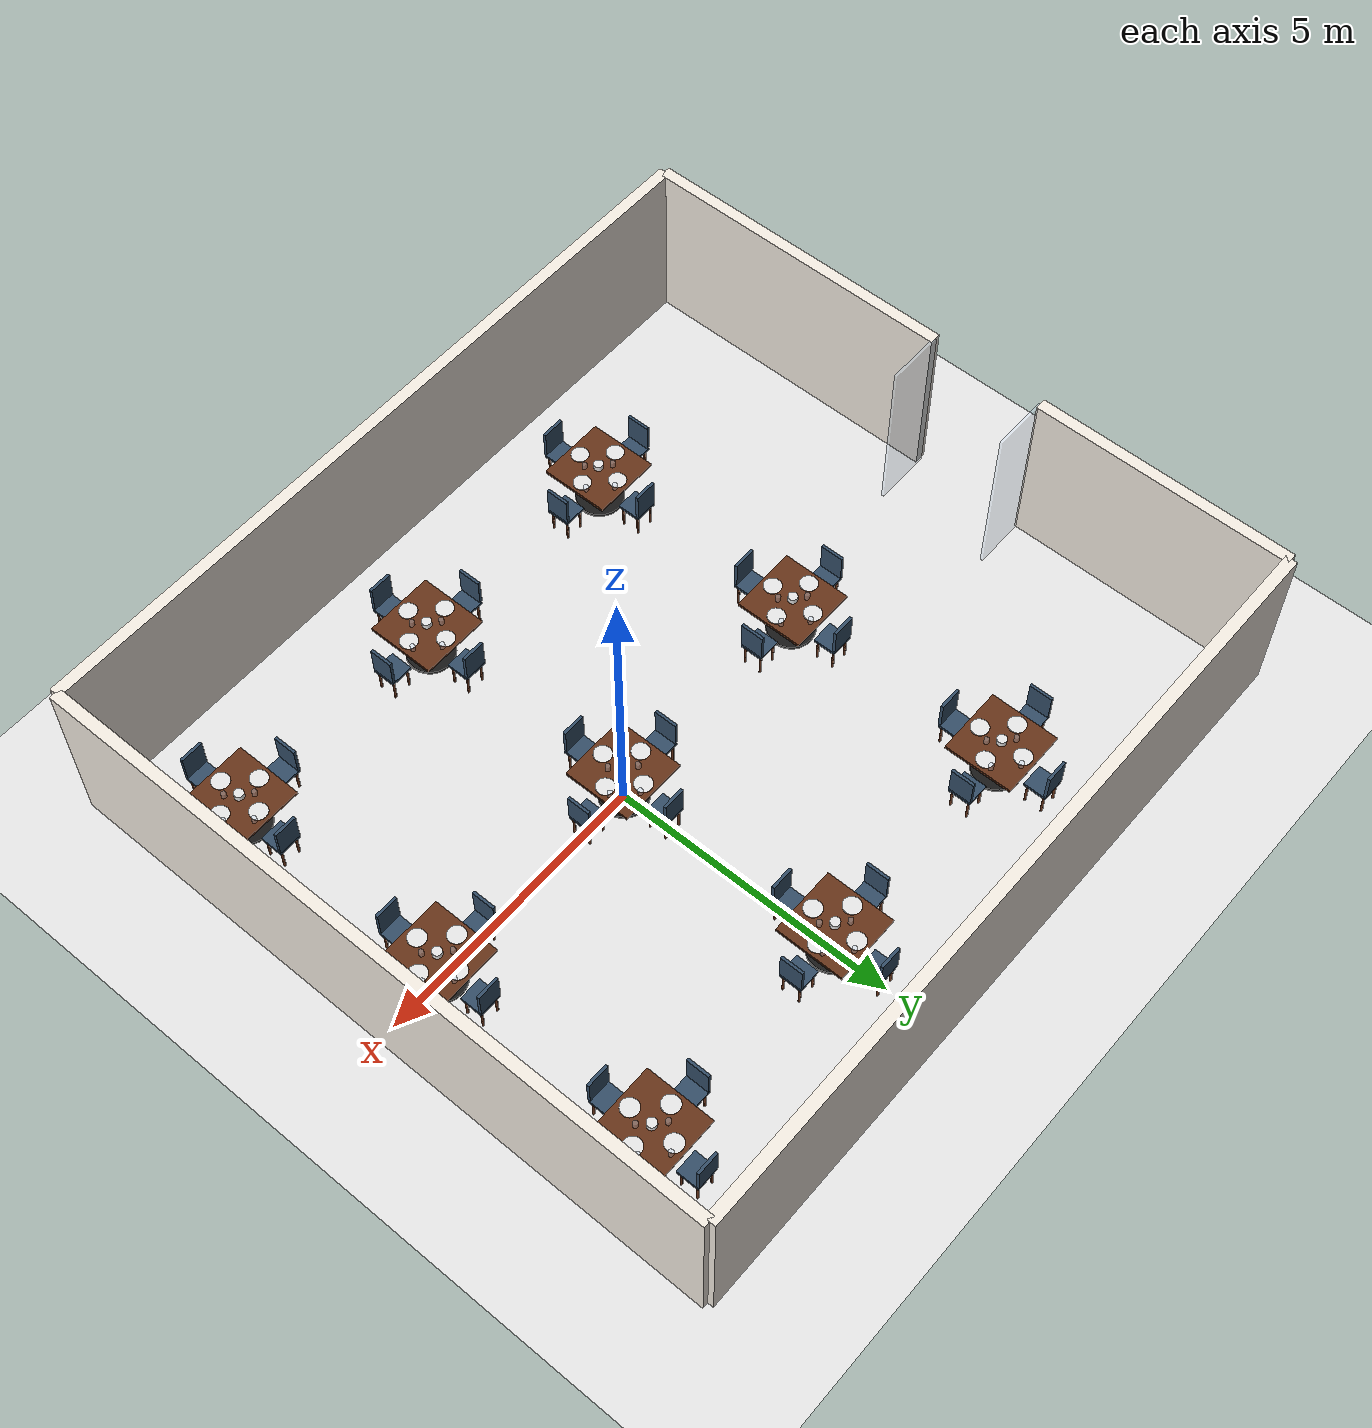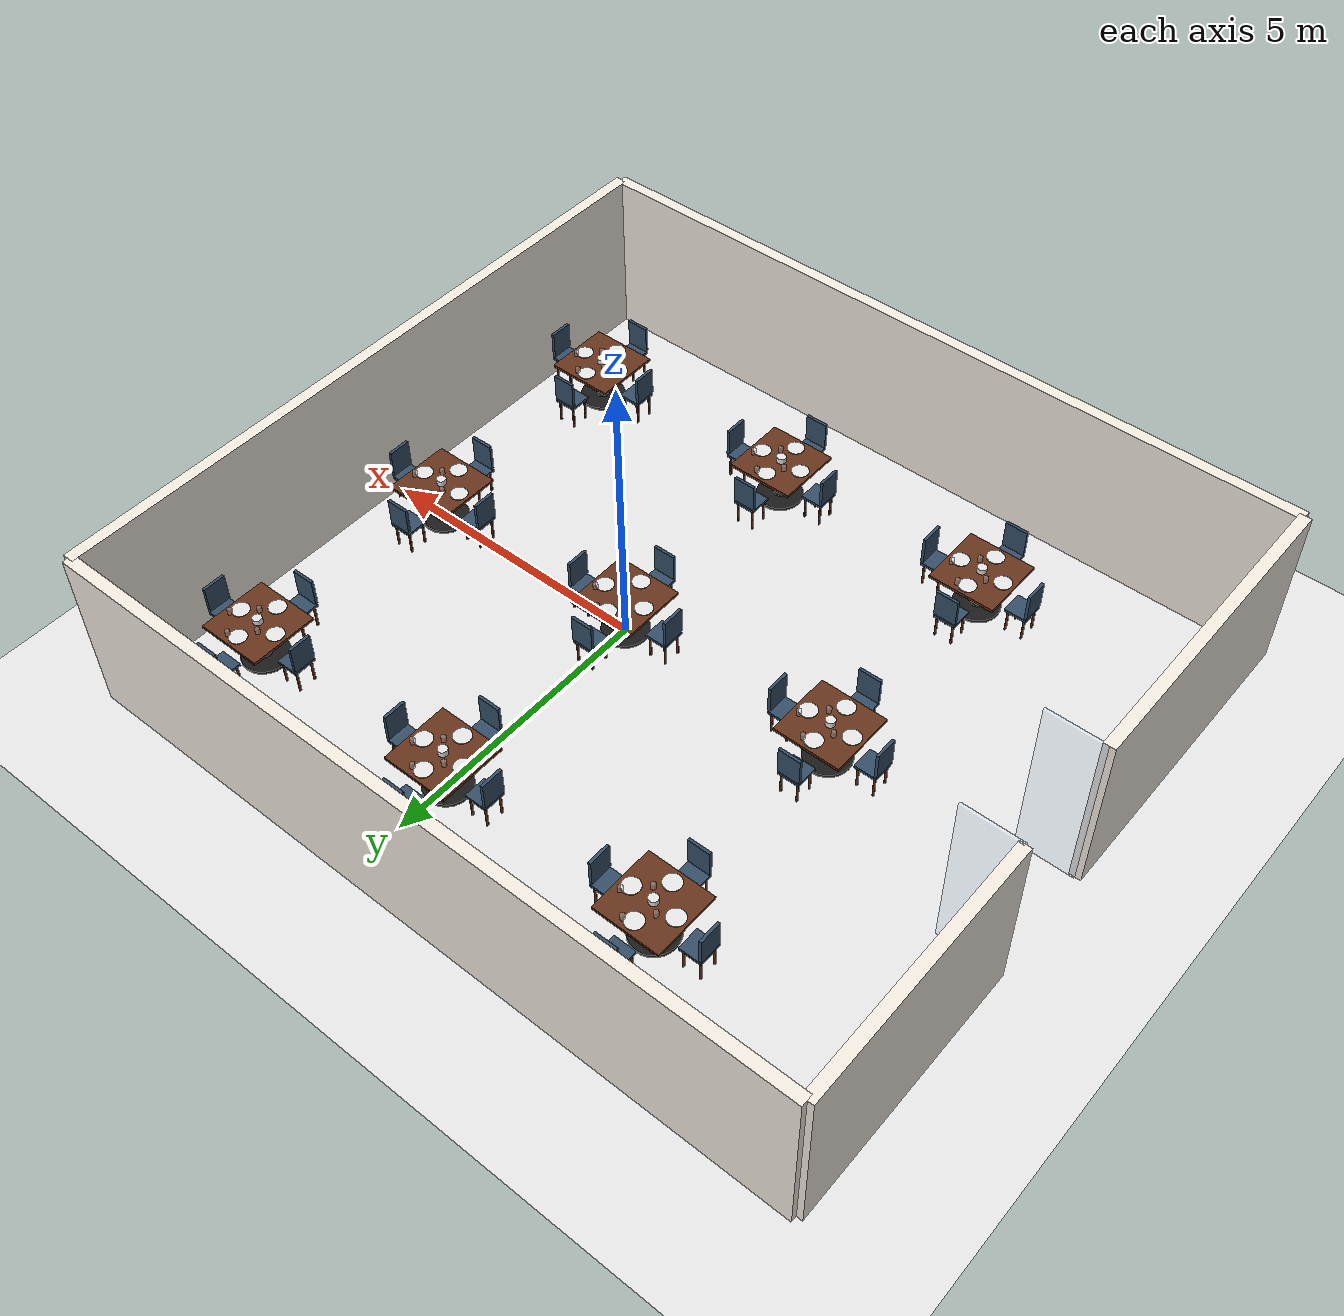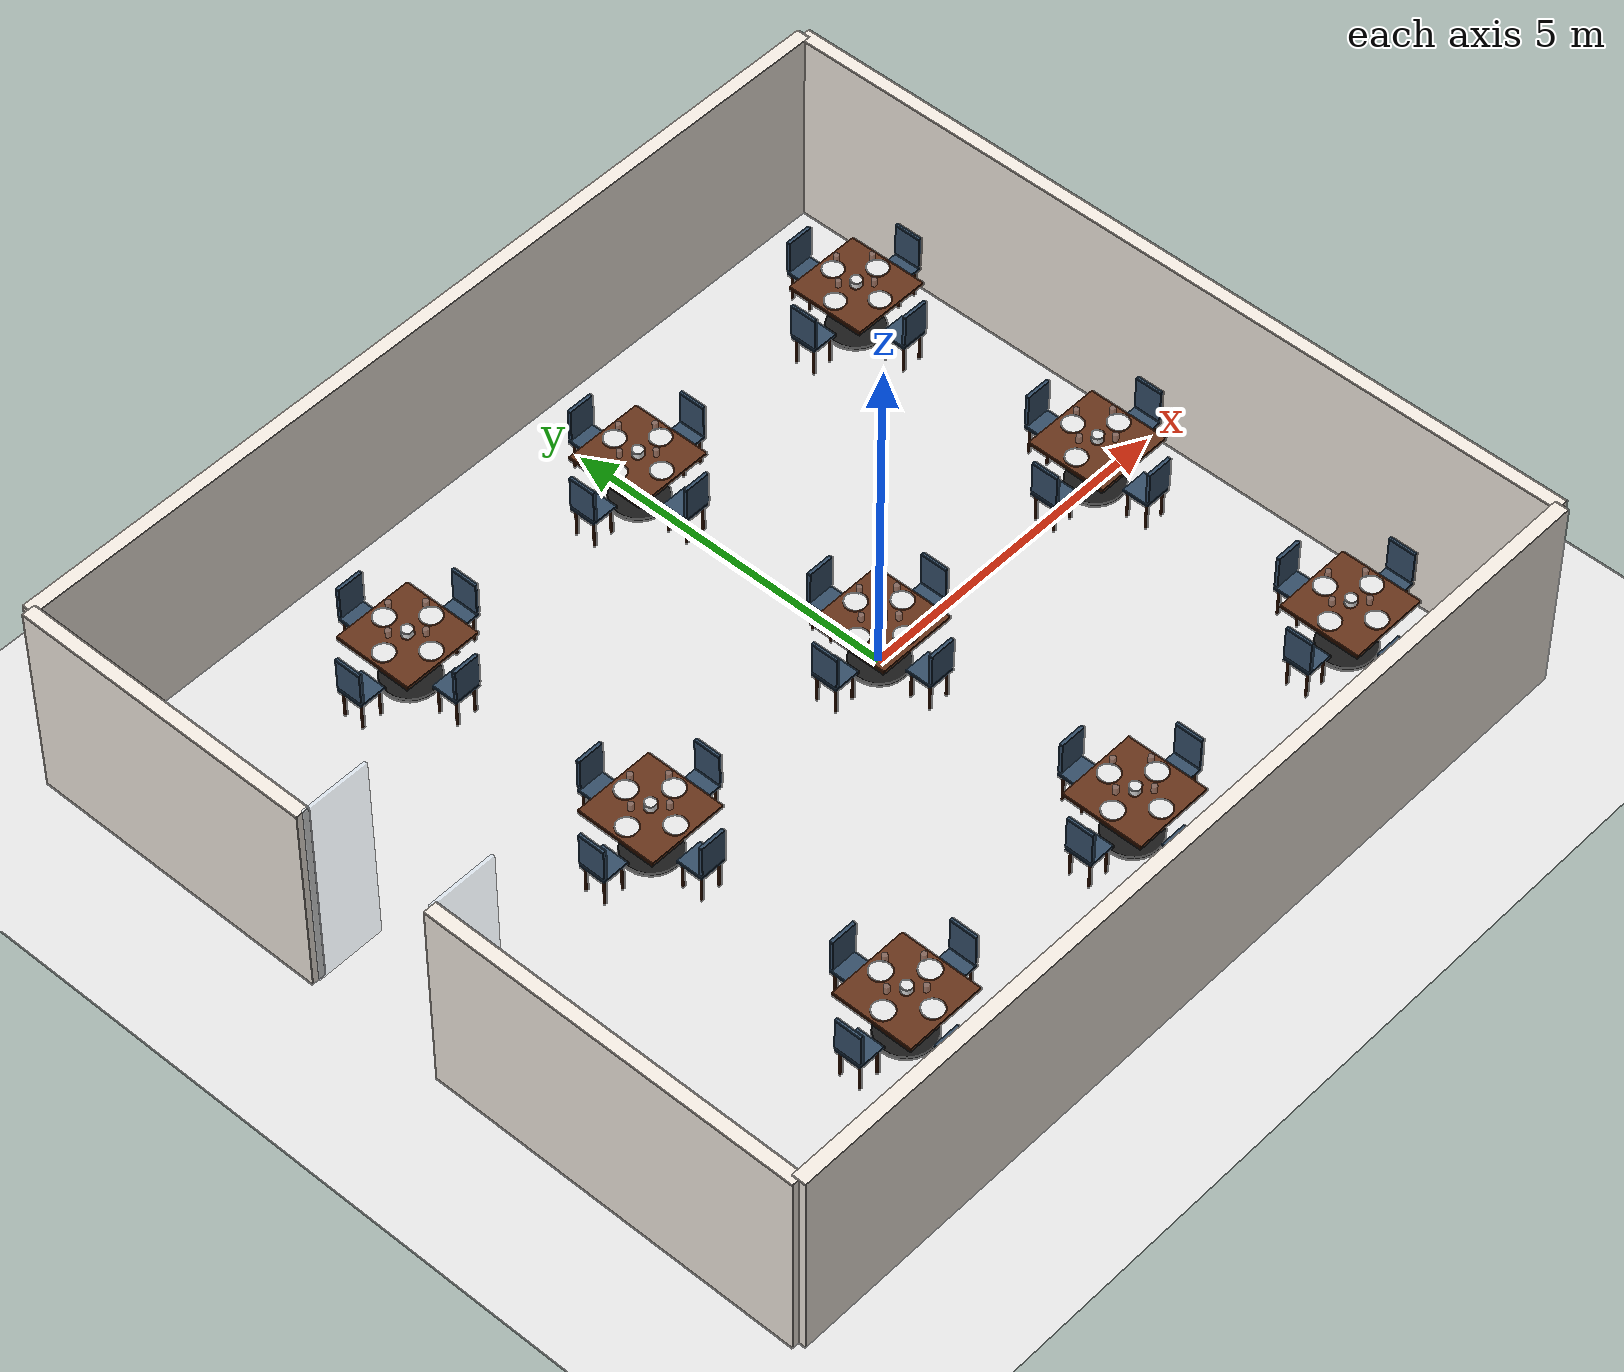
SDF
<?xml version="1.0" ?>
<sdf version="1.9">
  <world name="argo_restaurant">

    <physics name="4ms" type="ignored">
      <max_step_size>0.004</max_step_size>
      <real_time_factor>1.0</real_time_factor>
    </physics>
    <plugin filename="gz-sim-physics-system" name="gz::sim::systems::Physics"></plugin>
    <plugin filename="gz-sim-user-commands-system" name="gz::sim::systems::UserCommands"></plugin>
    <plugin filename="gz-sim-scene-broadcaster-system" name="gz::sim::systems::SceneBroadcaster"></plugin>
    <plugin filename="gz-sim-sensors-system" name="gz::sim::systems::Sensors">
      <render_engine>ogre2</render_engine>
    </plugin>
    <plugin filename="gz-sim-imu-system" name="gz::sim::systems::Imu"></plugin>

    <scene>
      <ambient>0.6 0.6 0.6 1.0</ambient>
      <background>0.8 0.8 0.8 1.0</background>
      <shadows>true</shadows>
    </scene>

    <light type="directional" name="sun">
      <cast_shadows>true</cast_shadows>
      <pose>0 0 10 0 0 0</pose>
      <diffuse>0.8 0.8 0.8 1</diffuse>
      <specular>0.2 0.2 0.2 1</specular>
      <attenuation>
        <range>1000</range>
        <constant>0.9</constant>
        <linear>0.01</linear>
        <quadratic>0.001</quadratic>
      </attenuation>
      <direction>-0.5 0.1 -0.9</direction>
    </light>

    <model name="ground_plane">
      <static>true</static>
      <link name="link">
        <collision name="collision">
          <geometry>
            <plane>
              <normal>0 0 1</normal>
              <size>100 100</size>
            </plane>
          </geometry>
        </collision>
        <visual name="visual">
          <geometry>
            <plane>
              <normal>0 0 1</normal>
              <size>100 100</size>
            </plane>
          </geometry>

          <material>
            <ambient>0.9 0.9 0.9 1</ambient>
            <diffuse>0.9 0.9 0.9 1</diffuse>
            <specular>0.1 0.1 0.1 1</specular>
            <pbr>
              <metal>
                <roughness>0.1</roughness>
                <metalness>0.0</metalness>
              </metal>
            </pbr>
          </material>

        </visual>
      </link>
    </model>
        <model name="restaurant_walls">
      <static>true</static>

      <link name="north_wall_link">
        <pose>-1.4 6 1.5 0 0 0</pose>
        <collision name="north_wall_collision">
          <geometry>
            <box><size>13.2 0.2 3.0</size></box>
          </geometry>
        </collision>
        <visual name="north_wall_visual">
          <geometry>
            <box><size>13.2 0.2 3.0</size></box>
          </geometry>

          <material>
            <ambient>0.95 0.92 0.88 1</ambient>
            <diffuse>0.95 0.92 0.88 1</diffuse>
            <specular>0.1 0.1 0.1 1</specular>
            <pbr>
              <metal>
                <roughness>0.8</roughness>
                <metalness>0.0</metalness>
              </metal>
            </pbr>
          </material>

        </visual>
      </link>

      <link name="south_wall_link">
        <pose>-1.4 -6 1.5 0 0 0</pose>
        <collision name="south_wall_collision">
          <geometry>
            <box><size>13.2 0.2 3.0</size></box>
          </geometry>
        </collision>
        <visual name="south_wall_visual">
          <geometry>
            <box><size>13.2 0.2 3.0</size></box>
          </geometry>

          <material>
            <ambient>0.95 0.92 0.88 1</ambient>
            <diffuse>0.95 0.92 0.88 1</diffuse>
            <specular>0.1 0.1 0.1 1</specular>
            <pbr>
              <metal>
                <roughness>0.8</roughness>
                <metalness>0.0</metalness>
              </metal>
            </pbr>
          </material>

        </visual>
      </link>

      <link name="east_wall_link">
        <pose>5.2 0 1.5 0 0 0</pose>
        <collision name="east_wall_collision">
          <geometry>
            <box><size>0.2 12 3.0</size></box>
          </geometry>
        </collision>
        <visual name="east_wall_visual">
          <geometry>
            <box><size>0.2 12 3.0</size></box>
          </geometry>

          <material>
            <ambient>0.95 0.92 0.88 1</ambient>
            <diffuse>0.95 0.92 0.88 1</diffuse>
            <specular>0.1 0.1 0.1 1</specular>
            <pbr>
              <metal>
                <roughness>0.8</roughness>
                <metalness>0.0</metalness>
              </metal>
            </pbr>
          </material>

        </visual>
      </link>

      <link name="west_wall_1_link">
        <pose>-8 -3.25 1.5 0 0 0</pose>
        <collision name="west_wall_1_collision">
          <geometry>
            <box><size>0.2 5.5 3.0</size></box>
          </geometry>
        </collision>
        <visual name="west_wall_1_visual">
          <geometry>
            <box><size>0.2 5.5 3.0</size></box>
          </geometry>

          <material>
            <ambient>0.95 0.92 0.88 1</ambient>
            <diffuse>0.95 0.92 0.88 1</diffuse>
            <specular>0.1 0.1 0.1 1</specular>
            <pbr>
              <metal>
                <roughness>0.8</roughness>
                <metalness>0.0</metalness>
              </metal>
            </pbr>
          </material>

        </visual>
      </link>

      <link name="west_wall_2_link">
        <pose>-8 3.75 1.5 0 0 0</pose>
        <collision name="west_wall_2_collision">
          <geometry>
            <box><size>0.2 4.5 3.0</size></box>
          </geometry>
        </collision>
        <visual name="west_wall_2_visual">
          <geometry>
            <box><size>0.2 4.5 3.0</size></box>
          </geometry>

          <material>
            <ambient>0.95 0.92 0.88 1</ambient>
            <diffuse>0.95 0.92 0.88 1</diffuse>
            <specular>0.1 0.1 0.1 1</specular>
            <pbr>
              <metal>
                <roughness>0.8</roughness>
                <metalness>0.0</metalness>
              </metal>
            </pbr>
          </material>

        </visual>
      </link>

      <link name="entrance_door_l_link">
        <pose>-7.5 -0.5 1.5 0 0 1.5708</pose>
        <collision name="entrance_door_l_collision">
          <geometry>
            <box><size>0.05 1 3.0</size></box>
          </geometry>
        </collision>
        <visual name="entrance_door_l_visual">
          <geometry>
            <box><size>0.05 1 3.0</size></box>
          </geometry>

          <material>
            <ambient>0.8 0.9 1.0 0.3</ambient>
            <diffuse>0.8 0.9 1.0 0.3</diffuse>
            <specular>0.9 0.9 0.9 1</specular>
            <pbr>
              <metal>
                <roughness>0.0</roughness>
                <metalness>0.9</metalness>
              </metal>
            </pbr>
          </material>

        </visual>
      </link>

      <link name="entrance_door_r_link">
        <pose>-7.5 1.5 1.5 0 0 1.5708</pose>
        <collision name="entrance_door_r_collision">
          <geometry>
            <box><size>0.05 1 3.0</size></box>
          </geometry>
        </collision>
        <visual name="entrance_door_r_visual">
          <geometry>
            <box><size>0.05 1 3.0</size></box>
          </geometry>

          <material>
            <ambient>0.8 0.9 1.0 0.3</ambient>
            <diffuse>0.8 0.9 1.0 0.3</diffuse>
            <specular>0.9 0.9 0.9 1</specular>
            <pbr>
              <metal>
                <roughness>0.0</roughness>
                <metalness>0.9</metalness>
              </metal>
            </pbr>
          </material>

        </visual>
      </link>
    </model>
    <model name="table_0">
      <static>true</static>

      <link name="top_link">
        <pose>-4.0 -4.0 0.75 0 0 0</pose>
        <collision name="top_collision">
          <geometry>
            <box><size>1.2 1.2 0.05</size></box>
          </geometry>
        </collision>
        <visual name="top_visual">
          <geometry>
            <box><size>1.2 1.2 0.05</size></box>
          </geometry>

          <material>
            <ambient>0.4 0.2 0.1 1</ambient>
            <diffuse>0.4 0.2 0.1 1</diffuse>
            <specular>0.1 0.1 0.1 1</specular>
            <pbr>
              <metal>
                <roughness>0.7</roughness>
                <metalness>0.1</metalness>
              </metal>
            </pbr>
          </material>

        </visual>
      </link>

      <link name="leg_link">
        <pose>-4.0 -4.0 0.375 0 0 0</pose>
        <collision name="leg_collision">
          <geometry>
            <cylinder>
              <radius>0.1</radius>
              <length>0.75</length>
            </cylinder>
          </geometry>
        </collision>
        <visual name="leg_visual">
          <geometry>
            <cylinder>
              <radius>0.1</radius>
              <length>0.75</length>
            </cylinder>
          </geometry>

          <material>
            <ambient>0.1 0.1 0.1 1</ambient>
            <diffuse>0.1 0.1 0.1 1</diffuse>
            <specular>0.1 0.1 0.1 1</specular>
            <pbr>
              <metal>
                <roughness>0.5</roughness>
                <metalness>0.0</metalness>
              </metal>
            </pbr>
          </material>

        </visual>
      </link>

      <link name="base_link">
        <pose>-4.0 -4.0 0.025 0 0 0</pose>
        <collision name="base_collision">
          <geometry>
            <cylinder>
              <radius>0.4</radius>
              <length>0.05</length>
            </cylinder>
          </geometry>
        </collision>
        <visual name="base_visual">
          <geometry>
            <cylinder>
              <radius>0.4</radius>
              <length>0.05</length>
            </cylinder>
          </geometry>

          <material>
            <ambient>0.1 0.1 0.1 1</ambient>
            <diffuse>0.1 0.1 0.1 1</diffuse>
            <specular>0.1 0.1 0.1 1</specular>
            <pbr>
              <metal>
                <roughness>0.5</roughness>
                <metalness>0.0</metalness>
              </metal>
            </pbr>
          </material>

        </visual>
      </link>

      <link name="chair_0_seat_link">
        <pose>-4.0 -3.2 0.45 0 0 0</pose>
        <collision name="chair_0_seat_collision">
          <geometry>
            <box><size>0.4 0.4 0.05</size></box>
          </geometry>
        </collision>
        <visual name="chair_0_seat_visual">
          <geometry>
            <box><size>0.4 0.4 0.05</size></box>
          </geometry>

          <material>
            <ambient>0.2 0.3 0.4 1</ambient>
            <diffuse>0.2 0.3 0.4 1</diffuse>
            <specular>0.1 0.1 0.1 1</specular>
            <pbr>
              <metal>
                <roughness>0.9</roughness>
                <metalness>0.0</metalness>
              </metal>
            </pbr>
          </material>

        </visual>
      </link>

      <link name="chair_0_leg_-0.15_-0.15_link">
        <pose>-4.15 -3.35 0.225 0 0 0</pose>
        <collision name="chair_0_leg_-0.15_-0.15_collision">
          <geometry>
            <cylinder>
              <radius>0.02</radius>
              <length>0.45</length>
            </cylinder>
          </geometry>
        </collision>
        <visual name="chair_0_leg_-0.15_-0.15_visual">
          <geometry>
            <cylinder>
              <radius>0.02</radius>
              <length>0.45</length>
            </cylinder>
          </geometry>

          <material>
            <ambient>0.4 0.2 0.1 1</ambient>
            <diffuse>0.4 0.2 0.1 1</diffuse>
            <specular>0.1 0.1 0.1 1</specular>
            <pbr>
              <metal>
                <roughness>0.7</roughness>
                <metalness>0.1</metalness>
              </metal>
            </pbr>
          </material>

        </visual>
      </link>

      <link name="chair_0_leg_0.15_-0.15_link">
        <pose>-3.85 -3.35 0.225 0 0 0</pose>
        <collision name="chair_0_leg_0.15_-0.15_collision">
          <geometry>
            <cylinder>
              <radius>0.02</radius>
              <length>0.45</length>
            </cylinder>
          </geometry>
        </collision>
        <visual name="chair_0_leg_0.15_-0.15_visual">
          <geometry>
            <cylinder>
              <radius>0.02</radius>
              <length>0.45</length>
            </cylinder>
          </geometry>

          <material>
            <ambient>0.4 0.2 0.1 1</ambient>
            <diffuse>0.4 0.2 0.1 1</diffuse>
            <specular>0.1 0.1 0.1 1</specular>
            <pbr>
              <metal>
                <roughness>0.7</roughness>
                <metalness>0.1</metalness>
              </metal>
            </pbr>
          </material>

        </visual>
      </link>

      <link name="chair_0_leg_-0.15_0.15_link">
        <pose>-4.15 -3.0500000000000003 0.225 0 0 0</pose>
        <collision name="chair_0_leg_-0.15_0.15_collision">
          <geometry>
            <cylinder>
              <radius>0.02</radius>
              <length>0.45</length>
            </cylinder>
          </geometry>
        </collision>
        <visual name="chair_0_leg_-0.15_0.15_visual">
          <geometry>
            <cylinder>
              <radius>0.02</radius>
              <length>0.45</length>
            </cylinder>
          </geometry>

          <material>
            <ambient>0.4 0.2 0.1 1</ambient>
            <diffuse>0.4 0.2 0.1 1</diffuse>
            <specular>0.1 0.1 0.1 1</specular>
            <pbr>
              <metal>
                <roughness>0.7</roughness>
                <metalness>0.1</metalness>
              </metal>
            </pbr>
          </material>

        </visual>
      </link>

      <link name="chair_0_leg_0.15_0.15_link">
        <pose>-3.85 -3.0500000000000003 0.225 0 0 0</pose>
        <collision name="chair_0_leg_0.15_0.15_collision">
          <geometry>
            <cylinder>
              <radius>0.02</radius>
              <length>0.45</length>
            </cylinder>
          </geometry>
        </collision>
        <visual name="chair_0_leg_0.15_0.15_visual">
          <geometry>
            <cylinder>
              <radius>0.02</radius>
              <length>0.45</length>
            </cylinder>
          </geometry>

          <material>
            <ambient>0.4 0.2 0.1 1</ambient>
            <diffuse>0.4 0.2 0.1 1</diffuse>
            <specular>0.1 0.1 0.1 1</specular>
            <pbr>
              <metal>
                <roughness>0.7</roughness>
                <metalness>0.1</metalness>
              </metal>
            </pbr>
          </material>

        </visual>
      </link>

      <link name="chair_0_back_link">
        <pose>-4.0 -3.02 0.75 0 0 0</pose>
        <collision name="chair_0_back_collision">
          <geometry>
            <box><size>0.4 0.05 0.5</size></box>
          </geometry>
        </collision>
        <visual name="chair_0_back_visual">
          <geometry>
            <box><size>0.4 0.05 0.5</size></box>
          </geometry>

          <material>
            <ambient>0.2 0.3 0.4 1</ambient>
            <diffuse>0.2 0.3 0.4 1</diffuse>
            <specular>0.1 0.1 0.1 1</specular>
            <pbr>
              <metal>
                <roughness>0.9</roughness>
                <metalness>0.0</metalness>
              </metal>
            </pbr>
          </material>

        </visual>
      </link>

      <link name="chair_1_seat_link">
        <pose>-4.0 -4.8 0.45 0 0 3.1415</pose>
        <collision name="chair_1_seat_collision">
          <geometry>
            <box><size>0.4 0.4 0.05</size></box>
          </geometry>
        </collision>
        <visual name="chair_1_seat_visual">
          <geometry>
            <box><size>0.4 0.4 0.05</size></box>
          </geometry>

          <material>
            <ambient>0.2 0.3 0.4 1</ambient>
            <diffuse>0.2 0.3 0.4 1</diffuse>
            <specular>0.1 0.1 0.1 1</specular>
            <pbr>
              <metal>
                <roughness>0.9</roughness>
                <metalness>0.0</metalness>
              </metal>
            </pbr>
          </material>

        </visual>
      </link>

      <link name="chair_1_leg_-0.15_-0.15_link">
        <pose>-4.15 -4.95 0.225 0 0 0</pose>
        <collision name="chair_1_leg_-0.15_-0.15_collision">
          <geometry>
            <cylinder>
              <radius>0.02</radius>
              <length>0.45</length>
            </cylinder>
          </geometry>
        </collision>
        <visual name="chair_1_leg_-0.15_-0.15_visual">
          <geometry>
            <cylinder>
              <radius>0.02</radius>
              <length>0.45</length>
            </cylinder>
          </geometry>

          <material>
            <ambient>0.4 0.2 0.1 1</ambient>
            <diffuse>0.4 0.2 0.1 1</diffuse>
            <specular>0.1 0.1 0.1 1</specular>
            <pbr>
              <metal>
                <roughness>0.7</roughness>
                <metalness>0.1</metalness>
              </metal>
            </pbr>
          </material>

        </visual>
      </link>

      <link name="chair_1_leg_0.15_-0.15_link">
        <pose>-3.85 -4.95 0.225 0 0 0</pose>
        <collision name="chair_1_leg_0.15_-0.15_collision">
          <geometry>
            <cylinder>
              <radius>0.02</radius>
              <length>0.45</length>
            </cylinder>
          </geometry>
        </collision>
        <visual name="chair_1_leg_0.15_-0.15_visual">
          <geometry>
            <cylinder>
              <radius>0.02</radius>
              <length>0.45</length>
            </cylinder>
          </geometry>

          <material>
            <ambient>0.4 0.2 0.1 1</ambient>
            <diffuse>0.4 0.2 0.1 1</diffuse>
            <specular>0.1 0.1 0.1 1</specular>
            <pbr>
              <metal>
                <roughness>0.7</roughness>
                <metalness>0.1</metalness>
              </metal>
            </pbr>
          </material>

        </visual>
      </link>

      <link name="chair_1_leg_-0.15_0.15_link">
        <pose>-4.15 -4.6499999999999995 0.225 0 0 0</pose>
        <collision name="chair_1_leg_-0.15_0.15_collision">
          <geometry>
            <cylinder>
              <radius>0.02</radius>
              <length>0.45</length>
            </cylinder>
          </geometry>
        </collision>
        <visual name="chair_1_leg_-0.15_0.15_visual">
          <geometry>
            <cylinder>
              <radius>0.02</radius>
              <length>0.45</length>
            </cylinder>
          </geometry>

          <material>
            <ambient>0.4 0.2 0.1 1</ambient>
            <diffuse>0.4 0.2 0.1 1</diffuse>
            <specular>0.1 0.1 0.1 1</specular>
            <pbr>
              <metal>
                <roughness>0.7</roughness>
                <metalness>0.1</metalness>
              </metal>
            </pbr>
          </material>

        </visual>
      </link>

      <link name="chair_1_leg_0.15_0.15_link">
        <pose>-3.85 -4.6499999999999995 0.225 0 0 0</pose>
        <collision name="chair_1_leg_0.15_0.15_collision">
          <geometry>
            <cylinder>
              <radius>0.02</radius>
              <length>0.45</length>
            </cylinder>
          </geometry>
        </collision>
        <visual name="chair_1_leg_0.15_0.15_visual">
          <geometry>
            <cylinder>
              <radius>0.02</radius>
              <length>0.45</length>
            </cylinder>
          </geometry>

          <material>
            <ambient>0.4 0.2 0.1 1</ambient>
            <diffuse>0.4 0.2 0.1 1</diffuse>
            <specular>0.1 0.1 0.1 1</specular>
            <pbr>
              <metal>
                <roughness>0.7</roughness>
                <metalness>0.1</metalness>
              </metal>
            </pbr>
          </material>

        </visual>
      </link>

      <link name="chair_1_back_link">
        <pose>-4.000016677646139 -4.979999999227378 0.75 0 0 3.1415</pose>
        <collision name="chair_1_back_collision">
          <geometry>
            <box><size>0.4 0.05 0.5</size></box>
          </geometry>
        </collision>
        <visual name="chair_1_back_visual">
          <geometry>
            <box><size>0.4 0.05 0.5</size></box>
          </geometry>

          <material>
            <ambient>0.2 0.3 0.4 1</ambient>
            <diffuse>0.2 0.3 0.4 1</diffuse>
            <specular>0.1 0.1 0.1 1</specular>
            <pbr>
              <metal>
                <roughness>0.9</roughness>
                <metalness>0.0</metalness>
              </metal>
            </pbr>
          </material>

        </visual>
      </link>

      <link name="chair_2_seat_link">
        <pose>-3.2 -4.0 0.45 0 0 -1.5707</pose>
        <collision name="chair_2_seat_collision">
          <geometry>
            <box><size>0.4 0.4 0.05</size></box>
          </geometry>
        </collision>
        <visual name="chair_2_seat_visual">
          <geometry>
            <box><size>0.4 0.4 0.05</size></box>
          </geometry>

          <material>
            <ambient>0.2 0.3 0.4 1</ambient>
            <diffuse>0.2 0.3 0.4 1</diffuse>
            <specular>0.1 0.1 0.1 1</specular>
            <pbr>
              <metal>
                <roughness>0.9</roughness>
                <metalness>0.0</metalness>
              </metal>
            </pbr>
          </material>

        </visual>
      </link>

      <link name="chair_2_leg_-0.15_-0.15_link">
        <pose>-3.35 -4.15 0.225 0 0 0</pose>
        <collision name="chair_2_leg_-0.15_-0.15_collision">
          <geometry>
            <cylinder>
              <radius>0.02</radius>
              <length>0.45</length>
            </cylinder>
          </geometry>
        </collision>
        <visual name="chair_2_leg_-0.15_-0.15_visual">
          <geometry>
            <cylinder>
              <radius>0.02</radius>
              <length>0.45</length>
            </cylinder>
          </geometry>

          <material>
            <ambient>0.4 0.2 0.1 1</ambient>
            <diffuse>0.4 0.2 0.1 1</diffuse>
            <specular>0.1 0.1 0.1 1</specular>
            <pbr>
              <metal>
                <roughness>0.7</roughness>
                <metalness>0.1</metalness>
              </metal>
            </pbr>
          </material>

        </visual>
      </link>

      <link name="chair_2_leg_0.15_-0.15_link">
        <pose>-3.0500000000000003 -4.15 0.225 0 0 0</pose>
        <collision name="chair_2_leg_0.15_-0.15_collision">
          <geometry>
            <cylinder>
              <radius>0.02</radius>
              <length>0.45</length>
            </cylinder>
          </geometry>
        </collision>
        <visual name="chair_2_leg_0.15_-0.15_visual">
          <geometry>
            <cylinder>
              <radius>0.02</radius>
              <length>0.45</length>
            </cylinder>
          </geometry>

          <material>
            <ambient>0.4 0.2 0.1 1</ambient>
            <diffuse>0.4 0.2 0.1 1</diffuse>
            <specular>0.1 0.1 0.1 1</specular>
            <pbr>
              <metal>
                <roughness>0.7</roughness>
                <metalness>0.1</metalness>
              </metal>
            </pbr>
          </material>

        </visual>
      </link>

      <link name="chair_2_leg_-0.15_0.15_link">
        <pose>-3.35 -3.85 0.225 0 0 0</pose>
        <collision name="chair_2_leg_-0.15_0.15_collision">
          <geometry>
            <cylinder>
              <radius>0.02</radius>
              <length>0.45</length>
            </cylinder>
          </geometry>
        </collision>
        <visual name="chair_2_leg_-0.15_0.15_visual">
          <geometry>
            <cylinder>
              <radius>0.02</radius>
              <length>0.45</length>
            </cylinder>
          </geometry>

          <material>
            <ambient>0.4 0.2 0.1 1</ambient>
            <diffuse>0.4 0.2 0.1 1</diffuse>
            <specular>0.1 0.1 0.1 1</specular>
            <pbr>
              <metal>
                <roughness>0.7</roughness>
                <metalness>0.1</metalness>
              </metal>
            </pbr>
          </material>

        </visual>
      </link>

      <link name="chair_2_leg_0.15_0.15_link">
        <pose>-3.0500000000000003 -3.85 0.225 0 0 0</pose>
        <collision name="chair_2_leg_0.15_0.15_collision">
          <geometry>
            <cylinder>
              <radius>0.02</radius>
              <length>0.45</length>
            </cylinder>
          </geometry>
        </collision>
        <visual name="chair_2_leg_0.15_0.15_visual">
          <geometry>
            <cylinder>
              <radius>0.02</radius>
              <length>0.45</length>
            </cylinder>
          </geometry>

          <material>
            <ambient>0.4 0.2 0.1 1</ambient>
            <diffuse>0.4 0.2 0.1 1</diffuse>
            <specular>0.1 0.1 0.1 1</specular>
            <pbr>
              <metal>
                <roughness>0.7</roughness>
                <metalness>0.1</metalness>
              </metal>
            </pbr>
          </material>

        </visual>
      </link>

      <link name="chair_2_back_link">
        <pose>-3.020000000835097 -3.9999826611769453 0.75 0 0 -1.5707</pose>
        <collision name="chair_2_back_collision">
          <geometry>
            <box><size>0.4 0.05 0.5</size></box>
          </geometry>
        </collision>
        <visual name="chair_2_back_visual">
          <geometry>
            <box><size>0.4 0.05 0.5</size></box>
          </geometry>

          <material>
            <ambient>0.2 0.3 0.4 1</ambient>
            <diffuse>0.2 0.3 0.4 1</diffuse>
            <specular>0.1 0.1 0.1 1</specular>
            <pbr>
              <metal>
                <roughness>0.9</roughness>
                <metalness>0.0</metalness>
              </metal>
            </pbr>
          </material>

        </visual>
      </link>

      <link name="chair_3_seat_link">
        <pose>-4.8 -4.0 0.45 0 0 1.5707</pose>
        <collision name="chair_3_seat_collision">
          <geometry>
            <box><size>0.4 0.4 0.05</size></box>
          </geometry>
        </collision>
        <visual name="chair_3_seat_visual">
          <geometry>
            <box><size>0.4 0.4 0.05</size></box>
          </geometry>

          <material>
            <ambient>0.2 0.3 0.4 1</ambient>
            <diffuse>0.2 0.3 0.4 1</diffuse>
            <specular>0.1 0.1 0.1 1</specular>
            <pbr>
              <metal>
                <roughness>0.9</roughness>
                <metalness>0.0</metalness>
              </metal>
            </pbr>
          </material>

        </visual>
      </link>

      <link name="chair_3_leg_-0.15_-0.15_link">
        <pose>-4.95 -4.15 0.225 0 0 0</pose>
        <collision name="chair_3_leg_-0.15_-0.15_collision">
          <geometry>
            <cylinder>
              <radius>0.02</radius>
              <length>0.45</length>
            </cylinder>
          </geometry>
        </collision>
        <visual name="chair_3_leg_-0.15_-0.15_visual">
          <geometry>
            <cylinder>
              <radius>0.02</radius>
              <length>0.45</length>
            </cylinder>
          </geometry>

          <material>
            <ambient>0.4 0.2 0.1 1</ambient>
            <diffuse>0.4 0.2 0.1 1</diffuse>
            <specular>0.1 0.1 0.1 1</specular>
            <pbr>
              <metal>
                <roughness>0.7</roughness>
                <metalness>0.1</metalness>
              </metal>
            </pbr>
          </material>

        </visual>
      </link>

      <link name="chair_3_leg_0.15_-0.15_link">
        <pose>-4.6499999999999995 -4.15 0.225 0 0 0</pose>
        <collision name="chair_3_leg_0.15_-0.15_collision">
          <geometry>
            <cylinder>
              <radius>0.02</radius>
              <length>0.45</length>
            </cylinder>
          </geometry>
        </collision>
        <visual name="chair_3_leg_0.15_-0.15_visual">
          <geometry>
            <cylinder>
              <radius>0.02</radius>
              <length>0.45</length>
            </cylinder>
          </geometry>

          <material>
            <ambient>0.4 0.2 0.1 1</ambient>
            <diffuse>0.4 0.2 0.1 1</diffuse>
            <specular>0.1 0.1 0.1 1</specular>
            <pbr>
              <metal>
                <roughness>0.7</roughness>
                <metalness>0.1</metalness>
              </metal>
            </pbr>
          </material>

        </visual>
      </link>

      <link name="chair_3_leg_-0.15_0.15_link">
        <pose>-4.95 -3.85 0.225 0 0 0</pose>
        <collision name="chair_3_leg_-0.15_0.15_collision">
          <geometry>
            <cylinder>
              <radius>0.02</radius>
              <length>0.45</length>
            </cylinder>
          </geometry>
        </collision>
        <visual name="chair_3_leg_-0.15_0.15_visual">
          <geometry>
            <cylinder>
              <radius>0.02</radius>
              <length>0.45</length>
            </cylinder>
          </geometry>

          <material>
            <ambient>0.4 0.2 0.1 1</ambient>
            <diffuse>0.4 0.2 0.1 1</diffuse>
            <specular>0.1 0.1 0.1 1</specular>
            <pbr>
              <metal>
                <roughness>0.7</roughness>
                <metalness>0.1</metalness>
              </metal>
            </pbr>
          </material>

        </visual>
      </link>

      <link name="chair_3_leg_0.15_0.15_link">
        <pose>-4.6499999999999995 -3.85 0.225 0 0 0</pose>
        <collision name="chair_3_leg_0.15_0.15_collision">
          <geometry>
            <cylinder>
              <radius>0.02</radius>
              <length>0.45</length>
            </cylinder>
          </geometry>
        </collision>
        <visual name="chair_3_leg_0.15_0.15_visual">
          <geometry>
            <cylinder>
              <radius>0.02</radius>
              <length>0.45</length>
            </cylinder>
          </geometry>

          <material>
            <ambient>0.4 0.2 0.1 1</ambient>
            <diffuse>0.4 0.2 0.1 1</diffuse>
            <specular>0.1 0.1 0.1 1</specular>
            <pbr>
              <metal>
                <roughness>0.7</roughness>
                <metalness>0.1</metalness>
              </metal>
            </pbr>
          </material>

        </visual>
      </link>

      <link name="chair_3_back_link">
        <pose>-4.979999999164903 -3.9999826611769453 0.75 0 0 1.5707</pose>
        <collision name="chair_3_back_collision">
          <geometry>
            <box><size>0.4 0.05 0.5</size></box>
          </geometry>
        </collision>
        <visual name="chair_3_back_visual">
          <geometry>
            <box><size>0.4 0.05 0.5</size></box>
          </geometry>

          <material>
            <ambient>0.2 0.3 0.4 1</ambient>
            <diffuse>0.2 0.3 0.4 1</diffuse>
            <specular>0.1 0.1 0.1 1</specular>
            <pbr>
              <metal>
                <roughness>0.9</roughness>
                <metalness>0.0</metalness>
              </metal>
            </pbr>
          </material>

        </visual>
      </link>

      <link name="centerpiece_pot_link">
        <pose>-4.0 -4.0 0.825 0 0 0</pose>
        <collision name="centerpiece_pot_collision">
          <geometry>
            <cylinder>
              <radius>0.08</radius>
              <length>0.1</length>
            </cylinder>
          </geometry>
        </collision>
        <visual name="centerpiece_pot_visual">
          <geometry>
            <cylinder>
              <radius>0.08</radius>
              <length>0.1</length>
            </cylinder>
          </geometry>

          <material>
            <ambient>0.9 0.9 0.9 1</ambient>
            <diffuse>0.9 0.9 0.9 1</diffuse>
            <specular>0.1 0.1 0.1 1</specular>
            <pbr>
              <metal>
                <roughness>0.2</roughness>
                <metalness>0.0</metalness>
              </metal>
            </pbr>
          </material>

        </visual>
      </link>

      <link name="plate_0_link">
        <pose>-4.0 -3.6 0.78 0 0 0</pose>
        <collision name="plate_0_collision">
          <geometry>
            <cylinder>
              <radius>0.15</radius>
              <length>0.01</length>
            </cylinder>
          </geometry>
        </collision>
        <visual name="plate_0_visual">
          <geometry>
            <cylinder>
              <radius>0.15</radius>
              <length>0.01</length>
            </cylinder>
          </geometry>

          <material>
            <ambient>0.9 0.9 0.9 1</ambient>
            <diffuse>0.9 0.9 0.9 1</diffuse>
            <specular>0.1 0.1 0.1 1</specular>
            <pbr>
              <metal>
                <roughness>0.2</roughness>
                <metalness>0.0</metalness>
              </metal>
            </pbr>
          </material>

        </visual>
      </link>

      <link name="glass_0_link">
        <pose>-3.85 -3.53 0.825 0 0 0</pose>
        <collision name="glass_0_collision">
          <geometry>
            <cylinder>
              <radius>0.04</radius>
              <length>0.1</length>
            </cylinder>
          </geometry>
        </collision>
        <visual name="glass_0_visual">
          <geometry>
            <cylinder>
              <radius>0.04</radius>
              <length>0.1</length>
            </cylinder>
          </geometry>

          <material>
            <ambient>0.8 0.9 1.0 0.3</ambient>
            <diffuse>0.8 0.9 1.0 0.3</diffuse>
            <specular>0.9 0.9 0.9 1</specular>
            <pbr>
              <metal>
                <roughness>0.0</roughness>
                <metalness>0.9</metalness>
              </metal>
            </pbr>
          </material>

        </visual>
      </link>

      <link name="plate_1_link">
        <pose>-4.0 -4.4 0.78 0 0 0</pose>
        <collision name="plate_1_collision">
          <geometry>
            <cylinder>
              <radius>0.15</radius>
              <length>0.01</length>
            </cylinder>
          </geometry>
        </collision>
        <visual name="plate_1_visual">
          <geometry>
            <cylinder>
              <radius>0.15</radius>
              <length>0.01</length>
            </cylinder>
          </geometry>

          <material>
            <ambient>0.9 0.9 0.9 1</ambient>
            <diffuse>0.9 0.9 0.9 1</diffuse>
            <specular>0.1 0.1 0.1 1</specular>
            <pbr>
              <metal>
                <roughness>0.2</roughness>
                <metalness>0.0</metalness>
              </metal>
            </pbr>
          </material>

        </visual>
      </link>

      <link name="glass_1_link">
        <pose>-3.85 -4.17 0.825 0 0 0</pose>
        <collision name="glass_1_collision">
          <geometry>
            <cylinder>
              <radius>0.04</radius>
              <length>0.1</length>
            </cylinder>
          </geometry>
        </collision>
        <visual name="glass_1_visual">
          <geometry>
            <cylinder>
              <radius>0.04</radius>
              <length>0.1</length>
            </cylinder>
          </geometry>

          <material>
            <ambient>0.8 0.9 1.0 0.3</ambient>
            <diffuse>0.8 0.9 1.0 0.3</diffuse>
            <specular>0.9 0.9 0.9 1</specular>
            <pbr>
              <metal>
                <roughness>0.0</roughness>
                <metalness>0.9</metalness>
              </metal>
            </pbr>
          </material>

        </visual>
      </link>

      <link name="plate_2_link">
        <pose>-3.6 -4.0 0.78 0 0 0</pose>
        <collision name="plate_2_collision">
          <geometry>
            <cylinder>
              <radius>0.15</radius>
              <length>0.01</length>
            </cylinder>
          </geometry>
        </collision>
        <visual name="plate_2_visual">
          <geometry>
            <cylinder>
              <radius>0.15</radius>
              <length>0.01</length>
            </cylinder>
          </geometry>

          <material>
            <ambient>0.9 0.9 0.9 1</ambient>
            <diffuse>0.9 0.9 0.9 1</diffuse>
            <specular>0.1 0.1 0.1 1</specular>
            <pbr>
              <metal>
                <roughness>0.2</roughness>
                <metalness>0.0</metalness>
              </metal>
            </pbr>
          </material>

        </visual>
      </link>

      <link name="glass_2_link">
        <pose>-3.53 -3.85 0.825 0 0 0</pose>
        <collision name="glass_2_collision">
          <geometry>
            <cylinder>
              <radius>0.04</radius>
              <length>0.1</length>
            </cylinder>
          </geometry>
        </collision>
        <visual name="glass_2_visual">
          <geometry>
            <cylinder>
              <radius>0.04</radius>
              <length>0.1</length>
            </cylinder>
          </geometry>

          <material>
            <ambient>0.8 0.9 1.0 0.3</ambient>
            <diffuse>0.8 0.9 1.0 0.3</diffuse>
            <specular>0.9 0.9 0.9 1</specular>
            <pbr>
              <metal>
                <roughness>0.0</roughness>
                <metalness>0.9</metalness>
              </metal>
            </pbr>
          </material>

        </visual>
      </link>

      <link name="plate_3_link">
        <pose>-4.4 -4.0 0.78 0 0 0</pose>
        <collision name="plate_3_collision">
          <geometry>
            <cylinder>
              <radius>0.15</radius>
              <length>0.01</length>
            </cylinder>
          </geometry>
        </collision>
        <visual name="plate_3_visual">
          <geometry>
            <cylinder>
              <radius>0.15</radius>
              <length>0.01</length>
            </cylinder>
          </geometry>

          <material>
            <ambient>0.9 0.9 0.9 1</ambient>
            <diffuse>0.9 0.9 0.9 1</diffuse>
            <specular>0.1 0.1 0.1 1</specular>
            <pbr>
              <metal>
                <roughness>0.2</roughness>
                <metalness>0.0</metalness>
              </metal>
            </pbr>
          </material>

        </visual>
      </link>

      <link name="glass_3_link">
        <pose>-4.17 -3.85 0.825 0 0 0</pose>
        <collision name="glass_3_collision">
          <geometry>
            <cylinder>
              <radius>0.04</radius>
              <length>0.1</length>
            </cylinder>
          </geometry>
        </collision>
        <visual name="glass_3_visual">
          <geometry>
            <cylinder>
              <radius>0.04</radius>
              <length>0.1</length>
            </cylinder>
          </geometry>

          <material>
            <ambient>0.8 0.9 1.0 0.3</ambient>
            <diffuse>0.8 0.9 1.0 0.3</diffuse>
            <specular>0.9 0.9 0.9 1</specular>
            <pbr>
              <metal>
                <roughness>0.0</roughness>
                <metalness>0.9</metalness>
              </metal>
            </pbr>
          </material>

        </visual>
      </link>
    </model>
    <model name="table_1">
      <static>true</static>

      <link name="top_link">
        <pose>0.0 -4.0 0.75 0 0 0</pose>
        <collision name="top_collision">
          <geometry>
            <box><size>1.2 1.2 0.05</size></box>
          </geometry>
        </collision>
        <visual name="top_visual">
          <geometry>
            <box><size>1.2 1.2 0.05</size></box>
          </geometry>

          <material>
            <ambient>0.4 0.2 0.1 1</ambient>
            <diffuse>0.4 0.2 0.1 1</diffuse>
            <specular>0.1 0.1 0.1 1</specular>
            <pbr>
              <metal>
                <roughness>0.7</roughness>
                <metalness>0.1</metalness>
              </metal>
            </pbr>
          </material>

        </visual>
      </link>

      <link name="leg_link">
        <pose>0.0 -4.0 0.375 0 0 0</pose>
        <collision name="leg_collision">
          <geometry>
            <cylinder>
              <radius>0.1</radius>
              <length>0.75</length>
            </cylinder>
          </geometry>
        </collision>
        <visual name="leg_visual">
          <geometry>
            <cylinder>
              <radius>0.1</radius>
              <length>0.75</length>
            </cylinder>
          </geometry>

          <material>
            <ambient>0.1 0.1 0.1 1</ambient>
            <diffuse>0.1 0.1 0.1 1</diffuse>
            <specular>0.1 0.1 0.1 1</specular>
            <pbr>
              <metal>
                <roughness>0.5</roughness>
                <metalness>0.0</metalness>
              </metal>
            </pbr>
          </material>

        </visual>
      </link>

      <link name="base_link">
        <pose>0.0 -4.0 0.025 0 0 0</pose>
        <collision name="base_collision">
          <geometry>
            <cylinder>
              <radius>0.4</radius>
              <length>0.05</length>
            </cylinder>
          </geometry>
        </collision>
        <visual name="base_visual">
          <geometry>
            <cylinder>
              <radius>0.4</radius>
              <length>0.05</length>
            </cylinder>
          </geometry>

          <material>
            <ambient>0.1 0.1 0.1 1</ambient>
            <diffuse>0.1 0.1 0.1 1</diffuse>
            <specular>0.1 0.1 0.1 1</specular>
            <pbr>
              <metal>
                <roughness>0.5</roughness>
                <metalness>0.0</metalness>
              </metal>
            </pbr>
          </material>

        </visual>
      </link>

      <link name="chair_0_seat_link">
        <pose>0.0 -3.2 0.45 0 0 0</pose>
        <collision name="chair_0_seat_collision">
          <geometry>
            <box><size>0.4 0.4 0.05</size></box>
          </geometry>
        </collision>
        <visual name="chair_0_seat_visual">
          <geometry>
            <box><size>0.4 0.4 0.05</size></box>
          </geometry>

          <material>
            <ambient>0.2 0.3 0.4 1</ambient>
            <diffuse>0.2 0.3 0.4 1</diffuse>
            <specular>0.1 0.1 0.1 1</specular>
            <pbr>
              <metal>
                <roughness>0.9</roughness>
                <metalness>0.0</metalness>
              </metal>
            </pbr>
          </material>

        </visual>
      </link>

      <link name="chair_0_leg_-0.15_-0.15_link">
        <pose>-0.15 -3.35 0.225 0 0 0</pose>
        <collision name="chair_0_leg_-0.15_-0.15_collision">
          <geometry>
            <cylinder>
              <radius>0.02</radius>
              <length>0.45</length>
            </cylinder>
          </geometry>
        </collision>
        <visual name="chair_0_leg_-0.15_-0.15_visual">
          <geometry>
            <cylinder>
              <radius>0.02</radius>
              <length>0.45</length>
            </cylinder>
          </geometry>

          <material>
            <ambient>0.4 0.2 0.1 1</ambient>
            <diffuse>0.4 0.2 0.1 1</diffuse>
            <specular>0.1 0.1 0.1 1</specular>
            <pbr>
              <metal>
                <roughness>0.7</roughness>
                <metalness>0.1</metalness>
              </metal>
            </pbr>
          </material>

        </visual>
      </link>

      <link name="chair_0_leg_0.15_-0.15_link">
        <pose>0.15 -3.35 0.225 0 0 0</pose>
        <collision name="chair_0_leg_0.15_-0.15_collision">
          <geometry>
            <cylinder>
              <radius>0.02</radius>
              <length>0.45</length>
            </cylinder>
          </geometry>
        </collision>
        <visual name="chair_0_leg_0.15_-0.15_visual">
          <geometry>
            <cylinder>
              <radius>0.02</radius>
              <length>0.45</length>
            </cylinder>
          </geometry>

          <material>
            <ambient>0.4 0.2 0.1 1</ambient>
            <diffuse>0.4 0.2 0.1 1</diffuse>
            <specular>0.1 0.1 0.1 1</specular>
            <pbr>
              <metal>
                <roughness>0.7</roughness>
                <metalness>0.1</metalness>
              </metal>
            </pbr>
          </material>

        </visual>
      </link>

      <link name="chair_0_leg_-0.15_0.15_link">
        <pose>-0.15 -3.0500000000000003 0.225 0 0 0</pose>
        <collision name="chair_0_leg_-0.15_0.15_collision">
          <geometry>
            <cylinder>
              <radius>0.02</radius>
              <length>0.45</length>
            </cylinder>
          </geometry>
        </collision>
        <visual name="chair_0_leg_-0.15_0.15_visual">
          <geometry>
            <cylinder>
              <radius>0.02</radius>
              <length>0.45</length>
            </cylinder>
          </geometry>

          <material>
            <ambient>0.4 0.2 0.1 1</ambient>
            <diffuse>0.4 0.2 0.1 1</diffuse>
            <specular>0.1 0.1 0.1 1</specular>
            <pbr>
              <metal>
                <roughness>0.7</roughness>
                <metalness>0.1</metalness>
              </metal>
            </pbr>
          </material>

        </visual>
      </link>

      <link name="chair_0_leg_0.15_0.15_link">
        <pose>0.15 -3.0500000000000003 0.225 0 0 0</pose>
        <collision name="chair_0_leg_0.15_0.15_collision">
          <geometry>
            <cylinder>
              <radius>0.02</radius>
              <length>0.45</length>
            </cylinder>
          </geometry>
        </collision>
        <visual name="chair_0_leg_0.15_0.15_visual">
          <geometry>
            <cylinder>
              <radius>0.02</radius>
              <length>0.45</length>
            </cylinder>
          </geometry>

          <material>
            <ambient>0.4 0.2 0.1 1</ambient>
            <diffuse>0.4 0.2 0.1 1</diffuse>
            <specular>0.1 0.1 0.1 1</specular>
            <pbr>
              <metal>
                <roughness>0.7</roughness>
                <metalness>0.1</metalness>
              </metal>
            </pbr>
          </material>

        </visual>
      </link>

      <link name="chair_0_back_link">
        <pose>0.0 -3.02 0.75 0 0 0</pose>
        <collision name="chair_0_back_collision">
          <geometry>
            <box><size>0.4 0.05 0.5</size></box>
          </geometry>
        </collision>
        <visual name="chair_0_back_visual">
          <geometry>
            <box><size>0.4 0.05 0.5</size></box>
          </geometry>

          <material>
            <ambient>0.2 0.3 0.4 1</ambient>
            <diffuse>0.2 0.3 0.4 1</diffuse>
            <specular>0.1 0.1 0.1 1</specular>
            <pbr>
              <metal>
                <roughness>0.9</roughness>
                <metalness>0.0</metalness>
              </metal>
            </pbr>
          </material>

        </visual>
      </link>

      <link name="chair_1_seat_link">
        <pose>0.0 -4.8 0.45 0 0 3.1415</pose>
        <collision name="chair_1_seat_collision">
          <geometry>
            <box><size>0.4 0.4 0.05</size></box>
          </geometry>
        </collision>
        <visual name="chair_1_seat_visual">
          <geometry>
            <box><size>0.4 0.4 0.05</size></box>
          </geometry>

          <material>
            <ambient>0.2 0.3 0.4 1</ambient>
            <diffuse>0.2 0.3 0.4 1</diffuse>
            <specular>0.1 0.1 0.1 1</specular>
            <pbr>
              <metal>
                <roughness>0.9</roughness>
                <metalness>0.0</metalness>
              </metal>
            </pbr>
          </material>

        </visual>
      </link>

      <link name="chair_1_leg_-0.15_-0.15_link">
        <pose>-0.15 -4.95 0.225 0 0 0</pose>
        <collision name="chair_1_leg_-0.15_-0.15_collision">
          <geometry>
            <cylinder>
              <radius>0.02</radius>
              <length>0.45</length>
            </cylinder>
          </geometry>
        </collision>
        <visual name="chair_1_leg_-0.15_-0.15_visual">
          <geometry>
            <cylinder>
              <radius>0.02</radius>
              <length>0.45</length>
            </cylinder>
          </geometry>

          <material>
            <ambient>0.4 0.2 0.1 1</ambient>
            <diffuse>0.4 0.2 0.1 1</diffuse>
            <specular>0.1 0.1 0.1 1</specular>
            <pbr>
              <metal>
                <roughness>0.7</roughness>
                <metalness>0.1</metalness>
              </metal>
            </pbr>
          </material>

        </visual>
      </link>

      <link name="chair_1_leg_0.15_-0.15_link">
        <pose>0.15 -4.95 0.225 0 0 0</pose>
        <collision name="chair_1_leg_0.15_-0.15_collision">
          <geometry>
            <cylinder>
              <radius>0.02</radius>
              <length>0.45</length>
            </cylinder>
          </geometry>
        </collision>
        <visual name="chair_1_leg_0.15_-0.15_visual">
          <geometry>
            <cylinder>
              <radius>0.02</radius>
              <length>0.45</length>
            </cylinder>
          </geometry>

          <material>
            <ambient>0.4 0.2 0.1 1</ambient>
            <diffuse>0.4 0.2 0.1 1</diffuse>
            <specular>0.1 0.1 0.1 1</specular>
            <pbr>
              <metal>
                <roughness>0.7</roughness>
                <metalness>0.1</metalness>
              </metal>
            </pbr>
          </material>

        </visual>
      </link>

      <link name="chair_1_leg_-0.15_0.15_link">
        <pose>-0.15 -4.6499999999999995 0.225 0 0 0</pose>
        <collision name="chair_1_leg_-0.15_0.15_collision">
          <geometry>
            <cylinder>
              <radius>0.02</radius>
              <length>0.45</length>
            </cylinder>
          </geometry>
        </collision>
        <visual name="chair_1_leg_-0.15_0.15_visual">
          <geometry>
            <cylinder>
              <radius>0.02</radius>
              <length>0.45</length>
            </cylinder>
          </geometry>

          <material>
            <ambient>0.4 0.2 0.1 1</ambient>
            <diffuse>0.4 0.2 0.1 1</diffuse>
            <specular>0.1 0.1 0.1 1</specular>
            <pbr>
              <metal>
                <roughness>0.7</roughness>
                <metalness>0.1</metalness>
              </metal>
            </pbr>
          </material>

        </visual>
      </link>

      <link name="chair_1_leg_0.15_0.15_link">
        <pose>0.15 -4.6499999999999995 0.225 0 0 0</pose>
        <collision name="chair_1_leg_0.15_0.15_collision">
          <geometry>
            <cylinder>
              <radius>0.02</radius>
              <length>0.45</length>
            </cylinder>
          </geometry>
        </collision>
        <visual name="chair_1_leg_0.15_0.15_visual">
          <geometry>
            <cylinder>
              <radius>0.02</radius>
              <length>0.45</length>
            </cylinder>
          </geometry>

          <material>
            <ambient>0.4 0.2 0.1 1</ambient>
            <diffuse>0.4 0.2 0.1 1</diffuse>
            <specular>0.1 0.1 0.1 1</specular>
            <pbr>
              <metal>
                <roughness>0.7</roughness>
                <metalness>0.1</metalness>
              </metal>
            </pbr>
          </material>

        </visual>
      </link>

      <link name="chair_1_back_link">
        <pose>-1.6677646138888247e-05 -4.979999999227378 0.75 0 0 3.1415</pose>
        <collision name="chair_1_back_collision">
          <geometry>
            <box><size>0.4 0.05 0.5</size></box>
          </geometry>
        </collision>
        <visual name="chair_1_back_visual">
          <geometry>
            <box><size>0.4 0.05 0.5</size></box>
          </geometry>

          <material>
            <ambient>0.2 0.3 0.4 1</ambient>
            <diffuse>0.2 0.3 0.4 1</diffuse>
            <specular>0.1 0.1 0.1 1</specular>
            <pbr>
              <metal>
                <roughness>0.9</roughness>
                <metalness>0.0</metalness>
              </metal>
            </pbr>
          </material>

        </visual>
      </link>

      <link name="chair_2_seat_link">
        <pose>0.8 -4.0 0.45 0 0 -1.5707</pose>
        <collision name="chair_2_seat_collision">
          <geometry>
            <box><size>0.4 0.4 0.05</size></box>
          </geometry>
        </collision>
        <visual name="chair_2_seat_visual">
          <geometry>
            <box><size>0.4 0.4 0.05</size></box>
          </geometry>

          <material>
            <ambient>0.2 0.3 0.4 1</ambient>
            <diffuse>0.2 0.3 0.4 1</diffuse>
            <specular>0.1 0.1 0.1 1</specular>
            <pbr>
              <metal>
                <roughness>0.9</roughness>
                <metalness>0.0</metalness>
              </metal>
            </pbr>
          </material>

        </visual>
      </link>

      <link name="chair_2_leg_-0.15_-0.15_link">
        <pose>0.65 -4.15 0.225 0 0 0</pose>
        <collision name="chair_2_leg_-0.15_-0.15_collision">
          <geometry>
            <cylinder>
              <radius>0.02</radius>
              <length>0.45</length>
            </cylinder>
          </geometry>
        </collision>
        <visual name="chair_2_leg_-0.15_-0.15_visual">
          <geometry>
            <cylinder>
              <radius>0.02</radius>
              <length>0.45</length>
            </cylinder>
          </geometry>

          <material>
            <ambient>0.4 0.2 0.1 1</ambient>
            <diffuse>0.4 0.2 0.1 1</diffuse>
            <specular>0.1 0.1 0.1 1</specular>
            <pbr>
              <metal>
                <roughness>0.7</roughness>
                <metalness>0.1</metalness>
              </metal>
            </pbr>
          </material>

        </visual>
      </link>

      <link name="chair_2_leg_0.15_-0.15_link">
        <pose>0.9500000000000001 -4.15 0.225 0 0 0</pose>
        <collision name="chair_2_leg_0.15_-0.15_collision">
          <geometry>
            <cylinder>
              <radius>0.02</radius>
              <length>0.45</length>
            </cylinder>
          </geometry>
        </collision>
        <visual name="chair_2_leg_0.15_-0.15_visual">
          <geometry>
            <cylinder>
              <radius>0.02</radius>
              <length>0.45</length>
            </cylinder>
          </geometry>

          <material>
            <ambient>0.4 0.2 0.1 1</ambient>
            <diffuse>0.4 0.2 0.1 1</diffuse>
            <specular>0.1 0.1 0.1 1</specular>
            <pbr>
              <metal>
                <roughness>0.7</roughness>
                <metalness>0.1</metalness>
              </metal>
            </pbr>
          </material>

        </visual>
      </link>

      <link name="chair_2_leg_-0.15_0.15_link">
        <pose>0.65 -3.85 0.225 0 0 0</pose>
        <collision name="chair_2_leg_-0.15_0.15_collision">
          <geometry>
            <cylinder>
              <radius>0.02</radius>
              <length>0.45</length>
            </cylinder>
          </geometry>
        </collision>
        <visual name="chair_2_leg_-0.15_0.15_visual">
          <geometry>
            <cylinder>
              <radius>0.02</radius>
              <length>0.45</length>
            </cylinder>
          </geometry>

          <material>
            <ambient>0.4 0.2 0.1 1</ambient>
            <diffuse>0.4 0.2 0.1 1</diffuse>
            <specular>0.1 0.1 0.1 1</specular>
            <pbr>
              <metal>
                <roughness>0.7</roughness>
                <metalness>0.1</metalness>
              </metal>
            </pbr>
          </material>

        </visual>
      </link>

      <link name="chair_2_leg_0.15_0.15_link">
        <pose>0.9500000000000001 -3.85 0.225 0 0 0</pose>
        <collision name="chair_2_leg_0.15_0.15_collision">
          <geometry>
            <cylinder>
              <radius>0.02</radius>
              <length>0.45</length>
            </cylinder>
          </geometry>
        </collision>
        <visual name="chair_2_leg_0.15_0.15_visual">
          <geometry>
            <cylinder>
              <radius>0.02</radius>
              <length>0.45</length>
            </cylinder>
          </geometry>

          <material>
            <ambient>0.4 0.2 0.1 1</ambient>
            <diffuse>0.4 0.2 0.1 1</diffuse>
            <specular>0.1 0.1 0.1 1</specular>
            <pbr>
              <metal>
                <roughness>0.7</roughness>
                <metalness>0.1</metalness>
              </metal>
            </pbr>
          </material>

        </visual>
      </link>

      <link name="chair_2_back_link">
        <pose>0.9799999991649034 -3.9999826611769453 0.75 0 0 -1.5707</pose>
        <collision name="chair_2_back_collision">
          <geometry>
            <box><size>0.4 0.05 0.5</size></box>
          </geometry>
        </collision>
        <visual name="chair_2_back_visual">
          <geometry>
            <box><size>0.4 0.05 0.5</size></box>
          </geometry>

          <material>
            <ambient>0.2 0.3 0.4 1</ambient>
            <diffuse>0.2 0.3 0.4 1</diffuse>
            <specular>0.1 0.1 0.1 1</specular>
            <pbr>
              <metal>
                <roughness>0.9</roughness>
                <metalness>0.0</metalness>
              </metal>
            </pbr>
          </material>

        </visual>
      </link>

      <link name="chair_3_seat_link">
        <pose>-0.8 -4.0 0.45 0 0 1.5707</pose>
        <collision name="chair_3_seat_collision">
          <geometry>
            <box><size>0.4 0.4 0.05</size></box>
          </geometry>
        </collision>
        <visual name="chair_3_seat_visual">
          <geometry>
            <box><size>0.4 0.4 0.05</size></box>
          </geometry>

          <material>
            <ambient>0.2 0.3 0.4 1</ambient>
            <diffuse>0.2 0.3 0.4 1</diffuse>
            <specular>0.1 0.1 0.1 1</specular>
            <pbr>
              <metal>
                <roughness>0.9</roughness>
                <metalness>0.0</metalness>
              </metal>
            </pbr>
          </material>

        </visual>
      </link>

      <link name="chair_3_leg_-0.15_-0.15_link">
        <pose>-0.9500000000000001 -4.15 0.225 0 0 0</pose>
        <collision name="chair_3_leg_-0.15_-0.15_collision">
          <geometry>
            <cylinder>
              <radius>0.02</radius>
              <length>0.45</length>
            </cylinder>
          </geometry>
        </collision>
        <visual name="chair_3_leg_-0.15_-0.15_visual">
          <geometry>
            <cylinder>
              <radius>0.02</radius>
              <length>0.45</length>
            </cylinder>
          </geometry>

          <material>
            <ambient>0.4 0.2 0.1 1</ambient>
            <diffuse>0.4 0.2 0.1 1</diffuse>
            <specular>0.1 0.1 0.1 1</specular>
            <pbr>
              <metal>
                <roughness>0.7</roughness>
                <metalness>0.1</metalness>
              </metal>
            </pbr>
          </material>

        </visual>
      </link>

      <link name="chair_3_leg_0.15_-0.15_link">
        <pose>-0.65 -4.15 0.225 0 0 0</pose>
        <collision name="chair_3_leg_0.15_-0.15_collision">
          <geometry>
            <cylinder>
              <radius>0.02</radius>
              <length>0.45</length>
            </cylinder>
          </geometry>
        </collision>
        <visual name="chair_3_leg_0.15_-0.15_visual">
          <geometry>
            <cylinder>
              <radius>0.02</radius>
              <length>0.45</length>
            </cylinder>
          </geometry>

          <material>
            <ambient>0.4 0.2 0.1 1</ambient>
            <diffuse>0.4 0.2 0.1 1</diffuse>
            <specular>0.1 0.1 0.1 1</specular>
            <pbr>
              <metal>
                <roughness>0.7</roughness>
                <metalness>0.1</metalness>
              </metal>
            </pbr>
          </material>

        </visual>
      </link>

      <link name="chair_3_leg_-0.15_0.15_link">
        <pose>-0.9500000000000001 -3.85 0.225 0 0 0</pose>
        <collision name="chair_3_leg_-0.15_0.15_collision">
          <geometry>
            <cylinder>
              <radius>0.02</radius>
              <length>0.45</length>
            </cylinder>
          </geometry>
        </collision>
        <visual name="chair_3_leg_-0.15_0.15_visual">
          <geometry>
            <cylinder>
              <radius>0.02</radius>
              <length>0.45</length>
            </cylinder>
          </geometry>

          <material>
            <ambient>0.4 0.2 0.1 1</ambient>
            <diffuse>0.4 0.2 0.1 1</diffuse>
            <specular>0.1 0.1 0.1 1</specular>
            <pbr>
              <metal>
                <roughness>0.7</roughness>
                <metalness>0.1</metalness>
              </metal>
            </pbr>
          </material>

        </visual>
      </link>

      <link name="chair_3_leg_0.15_0.15_link">
        <pose>-0.65 -3.85 0.225 0 0 0</pose>
        <collision name="chair_3_leg_0.15_0.15_collision">
          <geometry>
            <cylinder>
              <radius>0.02</radius>
              <length>0.45</length>
            </cylinder>
          </geometry>
        </collision>
        <visual name="chair_3_leg_0.15_0.15_visual">
          <geometry>
            <cylinder>
              <radius>0.02</radius>
              <length>0.45</length>
            </cylinder>
          </geometry>

          <material>
            <ambient>0.4 0.2 0.1 1</ambient>
            <diffuse>0.4 0.2 0.1 1</diffuse>
            <specular>0.1 0.1 0.1 1</specular>
            <pbr>
              <metal>
                <roughness>0.7</roughness>
                <metalness>0.1</metalness>
              </metal>
            </pbr>
          </material>

        </visual>
      </link>

      <link name="chair_3_back_link">
        <pose>-0.9799999991649034 -3.9999826611769453 0.75 0 0 1.5707</pose>
        <collision name="chair_3_back_collision">
          <geometry>
            <box><size>0.4 0.05 0.5</size></box>
          </geometry>
        </collision>
        <visual name="chair_3_back_visual">
          <geometry>
            <box><size>0.4 0.05 0.5</size></box>
          </geometry>

          <material>
            <ambient>0.2 0.3 0.4 1</ambient>
            <diffuse>0.2 0.3 0.4 1</diffuse>
            <specular>0.1 0.1 0.1 1</specular>
            <pbr>
              <metal>
                <roughness>0.9</roughness>
                <metalness>0.0</metalness>
              </metal>
            </pbr>
          </material>

        </visual>
      </link>

      <link name="centerpiece_pot_link">
        <pose>0.0 -4.0 0.825 0 0 0</pose>
        <collision name="centerpiece_pot_collision">
          <geometry>
            <cylinder>
              <radius>0.08</radius>
              <length>0.1</length>
            </cylinder>
          </geometry>
        </collision>
        <visual name="centerpiece_pot_visual">
          <geometry>
            <cylinder>
              <radius>0.08</radius>
              <length>0.1</length>
            </cylinder>
          </geometry>

          <material>
            <ambient>0.9 0.9 0.9 1</ambient>
            <diffuse>0.9 0.9 0.9 1</diffuse>
            <specular>0.1 0.1 0.1 1</specular>
            <pbr>
              <metal>
                <roughness>0.2</roughness>
                <metalness>0.0</metalness>
              </metal>
            </pbr>
          </material>

        </visual>
      </link>

      <link name="plate_0_link">
        <pose>0.0 -3.6 0.78 0 0 0</pose>
        <collision name="plate_0_collision">
          <geometry>
            <cylinder>
              <radius>0.15</radius>
              <length>0.01</length>
            </cylinder>
          </geometry>
        </collision>
        <visual name="plate_0_visual">
          <geometry>
            <cylinder>
              <radius>0.15</radius>
              <length>0.01</length>
            </cylinder>
          </geometry>

          <material>
            <ambient>0.9 0.9 0.9 1</ambient>
            <diffuse>0.9 0.9 0.9 1</diffuse>
            <specular>0.1 0.1 0.1 1</specular>
            <pbr>
              <metal>
                <roughness>0.2</roughness>
                <metalness>0.0</metalness>
              </metal>
            </pbr>
          </material>

        </visual>
      </link>

      <link name="glass_0_link">
        <pose>0.15 -3.53 0.825 0 0 0</pose>
        <collision name="glass_0_collision">
          <geometry>
            <cylinder>
              <radius>0.04</radius>
              <length>0.1</length>
            </cylinder>
          </geometry>
        </collision>
        <visual name="glass_0_visual">
          <geometry>
            <cylinder>
              <radius>0.04</radius>
              <length>0.1</length>
            </cylinder>
          </geometry>

          <material>
            <ambient>0.8 0.9 1.0 0.3</ambient>
            <diffuse>0.8 0.9 1.0 0.3</diffuse>
            <specular>0.9 0.9 0.9 1</specular>
            <pbr>
              <metal>
                <roughness>0.0</roughness>
                <metalness>0.9</metalness>
              </metal>
            </pbr>
          </material>

        </visual>
      </link>

      <link name="plate_1_link">
        <pose>0.0 -4.4 0.78 0 0 0</pose>
        <collision name="plate_1_collision">
          <geometry>
            <cylinder>
              <radius>0.15</radius>
              <length>0.01</length>
            </cylinder>
          </geometry>
        </collision>
        <visual name="plate_1_visual">
          <geometry>
            <cylinder>
              <radius>0.15</radius>
              <length>0.01</length>
            </cylinder>
          </geometry>

          <material>
            <ambient>0.9 0.9 0.9 1</ambient>
            <diffuse>0.9 0.9 0.9 1</diffuse>
            <specular>0.1 0.1 0.1 1</specular>
            <pbr>
              <metal>
                <roughness>0.2</roughness>
                <metalness>0.0</metalness>
              </metal>
            </pbr>
          </material>

        </visual>
      </link>

      <link name="glass_1_link">
        <pose>0.15 -4.17 0.825 0 0 0</pose>
        <collision name="glass_1_collision">
          <geometry>
            <cylinder>
              <radius>0.04</radius>
              <length>0.1</length>
            </cylinder>
          </geometry>
        </collision>
        <visual name="glass_1_visual">
          <geometry>
            <cylinder>
              <radius>0.04</radius>
              <length>0.1</length>
            </cylinder>
          </geometry>

          <material>
            <ambient>0.8 0.9 1.0 0.3</ambient>
            <diffuse>0.8 0.9 1.0 0.3</diffuse>
            <specular>0.9 0.9 0.9 1</specular>
            <pbr>
              <metal>
                <roughness>0.0</roughness>
                <metalness>0.9</metalness>
              </metal>
            </pbr>
          </material>

        </visual>
      </link>

      <link name="plate_2_link">
        <pose>0.4 -4.0 0.78 0 0 0</pose>
        <collision name="plate_2_collision">
          <geometry>
            <cylinder>
              <radius>0.15</radius>
              <length>0.01</length>
            </cylinder>
          </geometry>
        </collision>
        <visual name="plate_2_visual">
          <geometry>
            <cylinder>
              <radius>0.15</radius>
              <length>0.01</length>
            </cylinder>
          </geometry>

          <material>
            <ambient>0.9 0.9 0.9 1</ambient>
            <diffuse>0.9 0.9 0.9 1</diffuse>
            <specular>0.1 0.1 0.1 1</specular>
            <pbr>
              <metal>
                <roughness>0.2</roughness>
                <metalness>0.0</metalness>
              </metal>
            </pbr>
          </material>

        </visual>
      </link>

      <link name="glass_2_link">
        <pose>0.4700000000000001 -3.85 0.825 0 0 0</pose>
        <collision name="glass_2_collision">
          <geometry>
            <cylinder>
              <radius>0.04</radius>
              <length>0.1</length>
            </cylinder>
          </geometry>
        </collision>
        <visual name="glass_2_visual">
          <geometry>
            <cylinder>
              <radius>0.04</radius>
              <length>0.1</length>
            </cylinder>
          </geometry>

          <material>
            <ambient>0.8 0.9 1.0 0.3</ambient>
            <diffuse>0.8 0.9 1.0 0.3</diffuse>
            <specular>0.9 0.9 0.9 1</specular>
            <pbr>
              <metal>
                <roughness>0.0</roughness>
                <metalness>0.9</metalness>
              </metal>
            </pbr>
          </material>

        </visual>
      </link>

      <link name="plate_3_link">
        <pose>-0.4 -4.0 0.78 0 0 0</pose>
        <collision name="plate_3_collision">
          <geometry>
            <cylinder>
              <radius>0.15</radius>
              <length>0.01</length>
            </cylinder>
          </geometry>
        </collision>
        <visual name="plate_3_visual">
          <geometry>
            <cylinder>
              <radius>0.15</radius>
              <length>0.01</length>
            </cylinder>
          </geometry>

          <material>
            <ambient>0.9 0.9 0.9 1</ambient>
            <diffuse>0.9 0.9 0.9 1</diffuse>
            <specular>0.1 0.1 0.1 1</specular>
            <pbr>
              <metal>
                <roughness>0.2</roughness>
                <metalness>0.0</metalness>
              </metal>
            </pbr>
          </material>

        </visual>
      </link>

      <link name="glass_3_link">
        <pose>-0.17000000000000007 -3.85 0.825 0 0 0</pose>
        <collision name="glass_3_collision">
          <geometry>
            <cylinder>
              <radius>0.04</radius>
              <length>0.1</length>
            </cylinder>
          </geometry>
        </collision>
        <visual name="glass_3_visual">
          <geometry>
            <cylinder>
              <radius>0.04</radius>
              <length>0.1</length>
            </cylinder>
          </geometry>

          <material>
            <ambient>0.8 0.9 1.0 0.3</ambient>
            <diffuse>0.8 0.9 1.0 0.3</diffuse>
            <specular>0.9 0.9 0.9 1</specular>
            <pbr>
              <metal>
                <roughness>0.0</roughness>
                <metalness>0.9</metalness>
              </metal>
            </pbr>
          </material>

        </visual>
      </link>
    </model>
    <model name="table_2">
      <static>true</static>

      <link name="top_link">
        <pose>4.0 -4.0 0.75 0 0 0</pose>
        <collision name="top_collision">
          <geometry>
            <box><size>1.2 1.2 0.05</size></box>
          </geometry>
        </collision>
        <visual name="top_visual">
          <geometry>
            <box><size>1.2 1.2 0.05</size></box>
          </geometry>

          <material>
            <ambient>0.4 0.2 0.1 1</ambient>
            <diffuse>0.4 0.2 0.1 1</diffuse>
            <specular>0.1 0.1 0.1 1</specular>
            <pbr>
              <metal>
                <roughness>0.7</roughness>
                <metalness>0.1</metalness>
              </metal>
            </pbr>
          </material>

        </visual>
      </link>

      <link name="leg_link">
        <pose>4.0 -4.0 0.375 0 0 0</pose>
        <collision name="leg_collision">
          <geometry>
            <cylinder>
              <radius>0.1</radius>
              <length>0.75</length>
            </cylinder>
          </geometry>
        </collision>
        <visual name="leg_visual">
          <geometry>
            <cylinder>
              <radius>0.1</radius>
              <length>0.75</length>
            </cylinder>
          </geometry>

          <material>
            <ambient>0.1 0.1 0.1 1</ambient>
            <diffuse>0.1 0.1 0.1 1</diffuse>
            <specular>0.1 0.1 0.1 1</specular>
            <pbr>
              <metal>
                <roughness>0.5</roughness>
                <metalness>0.0</metalness>
              </metal>
            </pbr>
          </material>

        </visual>
      </link>

      <link name="base_link">
        <pose>4.0 -4.0 0.025 0 0 0</pose>
        <collision name="base_collision">
          <geometry>
            <cylinder>
              <radius>0.4</radius>
              <length>0.05</length>
            </cylinder>
          </geometry>
        </collision>
        <visual name="base_visual">
          <geometry>
            <cylinder>
              <radius>0.4</radius>
              <length>0.05</length>
            </cylinder>
          </geometry>

          <material>
            <ambient>0.1 0.1 0.1 1</ambient>
            <diffuse>0.1 0.1 0.1 1</diffuse>
            <specular>0.1 0.1 0.1 1</specular>
            <pbr>
              <metal>
                <roughness>0.5</roughness>
                <metalness>0.0</metalness>
              </metal>
            </pbr>
          </material>

        </visual>
      </link>

      <link name="chair_0_seat_link">
        <pose>4.0 -3.2 0.45 0 0 0</pose>
        <collision name="chair_0_seat_collision">
          <geometry>
            <box><size>0.4 0.4 0.05</size></box>
          </geometry>
        </collision>
        <visual name="chair_0_seat_visual">
          <geometry>
            <box><size>0.4 0.4 0.05</size></box>
          </geometry>

          <material>
            <ambient>0.2 0.3 0.4 1</ambient>
            <diffuse>0.2 0.3 0.4 1</diffuse>
            <specular>0.1 0.1 0.1 1</specular>
            <pbr>
              <metal>
                <roughness>0.9</roughness>
                <metalness>0.0</metalness>
              </metal>
            </pbr>
          </material>

        </visual>
      </link>

      <link name="chair_0_leg_-0.15_-0.15_link">
        <pose>3.85 -3.35 0.225 0 0 0</pose>
        <collision name="chair_0_leg_-0.15_-0.15_collision">
          <geometry>
            <cylinder>
              <radius>0.02</radius>
              <length>0.45</length>
            </cylinder>
          </geometry>
        </collision>
        <visual name="chair_0_leg_-0.15_-0.15_visual">
          <geometry>
            <cylinder>
              <radius>0.02</radius>
              <length>0.45</length>
            </cylinder>
          </geometry>

          <material>
            <ambient>0.4 0.2 0.1 1</ambient>
            <diffuse>0.4 0.2 0.1 1</diffuse>
            <specular>0.1 0.1 0.1 1</specular>
            <pbr>
              <metal>
                <roughness>0.7</roughness>
                <metalness>0.1</metalness>
              </metal>
            </pbr>
          </material>

        </visual>
      </link>

      <link name="chair_0_leg_0.15_-0.15_link">
        <pose>4.15 -3.35 0.225 0 0 0</pose>
        <collision name="chair_0_leg_0.15_-0.15_collision">
          <geometry>
            <cylinder>
              <radius>0.02</radius>
              <length>0.45</length>
            </cylinder>
          </geometry>
        </collision>
        <visual name="chair_0_leg_0.15_-0.15_visual">
          <geometry>
            <cylinder>
              <radius>0.02</radius>
              <length>0.45</length>
            </cylinder>
          </geometry>

          <material>
            <ambient>0.4 0.2 0.1 1</ambient>
            <diffuse>0.4 0.2 0.1 1</diffuse>
            <specular>0.1 0.1 0.1 1</specular>
            <pbr>
              <metal>
                <roughness>0.7</roughness>
                <metalness>0.1</metalness>
              </metal>
            </pbr>
          </material>

        </visual>
      </link>

      <link name="chair_0_leg_-0.15_0.15_link">
        <pose>3.85 -3.0500000000000003 0.225 0 0 0</pose>
        <collision name="chair_0_leg_-0.15_0.15_collision">
          <geometry>
            <cylinder>
              <radius>0.02</radius>
              <length>0.45</length>
            </cylinder>
          </geometry>
        </collision>
        <visual name="chair_0_leg_-0.15_0.15_visual">
          <geometry>
            <cylinder>
              <radius>0.02</radius>
              <length>0.45</length>
            </cylinder>
          </geometry>

          <material>
            <ambient>0.4 0.2 0.1 1</ambient>
            <diffuse>0.4 0.2 0.1 1</diffuse>
            <specular>0.1 0.1 0.1 1</specular>
            <pbr>
              <metal>
                <roughness>0.7</roughness>
                <metalness>0.1</metalness>
              </metal>
            </pbr>
          </material>

        </visual>
      </link>

      <link name="chair_0_leg_0.15_0.15_link">
        <pose>4.15 -3.0500000000000003 0.225 0 0 0</pose>
        <collision name="chair_0_leg_0.15_0.15_collision">
          <geometry>
            <cylinder>
              <radius>0.02</radius>
              <length>0.45</length>
            </cylinder>
          </geometry>
        </collision>
        <visual name="chair_0_leg_0.15_0.15_visual">
          <geometry>
            <cylinder>
              <radius>0.02</radius>
              <length>0.45</length>
            </cylinder>
          </geometry>

          <material>
            <ambient>0.4 0.2 0.1 1</ambient>
            <diffuse>0.4 0.2 0.1 1</diffuse>
            <specular>0.1 0.1 0.1 1</specular>
            <pbr>
              <metal>
                <roughness>0.7</roughness>
                <metalness>0.1</metalness>
              </metal>
            </pbr>
          </material>

        </visual>
      </link>

      <link name="chair_0_back_link">
        <pose>4.0 -3.02 0.75 0 0 0</pose>
        <collision name="chair_0_back_collision">
          <geometry>
            <box><size>0.4 0.05 0.5</size></box>
          </geometry>
        </collision>
        <visual name="chair_0_back_visual">
          <geometry>
            <box><size>0.4 0.05 0.5</size></box>
          </geometry>

          <material>
            <ambient>0.2 0.3 0.4 1</ambient>
            <diffuse>0.2 0.3 0.4 1</diffuse>
            <specular>0.1 0.1 0.1 1</specular>
            <pbr>
              <metal>
                <roughness>0.9</roughness>
                <metalness>0.0</metalness>
              </metal>
            </pbr>
          </material>

        </visual>
      </link>

      <link name="chair_1_seat_link">
        <pose>4.0 -4.8 0.45 0 0 3.1415</pose>
        <collision name="chair_1_seat_collision">
          <geometry>
            <box><size>0.4 0.4 0.05</size></box>
          </geometry>
        </collision>
        <visual name="chair_1_seat_visual">
          <geometry>
            <box><size>0.4 0.4 0.05</size></box>
          </geometry>

          <material>
            <ambient>0.2 0.3 0.4 1</ambient>
            <diffuse>0.2 0.3 0.4 1</diffuse>
            <specular>0.1 0.1 0.1 1</specular>
            <pbr>
              <metal>
                <roughness>0.9</roughness>
                <metalness>0.0</metalness>
              </metal>
            </pbr>
          </material>

        </visual>
      </link>

      <link name="chair_1_leg_-0.15_-0.15_link">
        <pose>3.85 -4.95 0.225 0 0 0</pose>
        <collision name="chair_1_leg_-0.15_-0.15_collision">
          <geometry>
            <cylinder>
              <radius>0.02</radius>
              <length>0.45</length>
            </cylinder>
          </geometry>
        </collision>
        <visual name="chair_1_leg_-0.15_-0.15_visual">
          <geometry>
            <cylinder>
              <radius>0.02</radius>
              <length>0.45</length>
            </cylinder>
          </geometry>

          <material>
            <ambient>0.4 0.2 0.1 1</ambient>
            <diffuse>0.4 0.2 0.1 1</diffuse>
            <specular>0.1 0.1 0.1 1</specular>
            <pbr>
              <metal>
                <roughness>0.7</roughness>
                <metalness>0.1</metalness>
              </metal>
            </pbr>
          </material>

        </visual>
      </link>

      <link name="chair_1_leg_0.15_-0.15_link">
        <pose>4.15 -4.95 0.225 0 0 0</pose>
        <collision name="chair_1_leg_0.15_-0.15_collision">
          <geometry>
            <cylinder>
              <radius>0.02</radius>
              <length>0.45</length>
            </cylinder>
          </geometry>
        </collision>
        <visual name="chair_1_leg_0.15_-0.15_visual">
          <geometry>
            <cylinder>
              <radius>0.02</radius>
              <length>0.45</length>
            </cylinder>
          </geometry>

          <material>
            <ambient>0.4 0.2 0.1 1</ambient>
            <diffuse>0.4 0.2 0.1 1</diffuse>
            <specular>0.1 0.1 0.1 1</specular>
            <pbr>
              <metal>
                <roughness>0.7</roughness>
                <metalness>0.1</metalness>
              </metal>
            </pbr>
          </material>

        </visual>
      </link>

      <link name="chair_1_leg_-0.15_0.15_link">
        <pose>3.85 -4.6499999999999995 0.225 0 0 0</pose>
        <collision name="chair_1_leg_-0.15_0.15_collision">
          <geometry>
            <cylinder>
              <radius>0.02</radius>
              <length>0.45</length>
            </cylinder>
          </geometry>
        </collision>
        <visual name="chair_1_leg_-0.15_0.15_visual">
          <geometry>
            <cylinder>
              <radius>0.02</radius>
              <length>0.45</length>
            </cylinder>
          </geometry>

          <material>
            <ambient>0.4 0.2 0.1 1</ambient>
            <diffuse>0.4 0.2 0.1 1</diffuse>
            <specular>0.1 0.1 0.1 1</specular>
            <pbr>
              <metal>
                <roughness>0.7</roughness>
                <metalness>0.1</metalness>
              </metal>
            </pbr>
          </material>

        </visual>
      </link>

      <link name="chair_1_leg_0.15_0.15_link">
        <pose>4.15 -4.6499999999999995 0.225 0 0 0</pose>
        <collision name="chair_1_leg_0.15_0.15_collision">
          <geometry>
            <cylinder>
              <radius>0.02</radius>
              <length>0.45</length>
            </cylinder>
          </geometry>
        </collision>
        <visual name="chair_1_leg_0.15_0.15_visual">
          <geometry>
            <cylinder>
              <radius>0.02</radius>
              <length>0.45</length>
            </cylinder>
          </geometry>

          <material>
            <ambient>0.4 0.2 0.1 1</ambient>
            <diffuse>0.4 0.2 0.1 1</diffuse>
            <specular>0.1 0.1 0.1 1</specular>
            <pbr>
              <metal>
                <roughness>0.7</roughness>
                <metalness>0.1</metalness>
              </metal>
            </pbr>
          </material>

        </visual>
      </link>

      <link name="chair_1_back_link">
        <pose>3.9999833223538612 -4.979999999227378 0.75 0 0 3.1415</pose>
        <collision name="chair_1_back_collision">
          <geometry>
            <box><size>0.4 0.05 0.5</size></box>
          </geometry>
        </collision>
        <visual name="chair_1_back_visual">
          <geometry>
            <box><size>0.4 0.05 0.5</size></box>
          </geometry>

          <material>
            <ambient>0.2 0.3 0.4 1</ambient>
            <diffuse>0.2 0.3 0.4 1</diffuse>
            <specular>0.1 0.1 0.1 1</specular>
            <pbr>
              <metal>
                <roughness>0.9</roughness>
                <metalness>0.0</metalness>
              </metal>
            </pbr>
          </material>

        </visual>
      </link>

      <link name="chair_2_seat_link">
        <pose>4.8 -4.0 0.45 0 0 -1.5707</pose>
        <collision name="chair_2_seat_collision">
          <geometry>
            <box><size>0.4 0.4 0.05</size></box>
          </geometry>
        </collision>
        <visual name="chair_2_seat_visual">
          <geometry>
            <box><size>0.4 0.4 0.05</size></box>
          </geometry>

          <material>
            <ambient>0.2 0.3 0.4 1</ambient>
            <diffuse>0.2 0.3 0.4 1</diffuse>
            <specular>0.1 0.1 0.1 1</specular>
            <pbr>
              <metal>
                <roughness>0.9</roughness>
                <metalness>0.0</metalness>
              </metal>
            </pbr>
          </material>

        </visual>
      </link>

      <link name="chair_2_leg_-0.15_-0.15_link">
        <pose>4.6499999999999995 -4.15 0.225 0 0 0</pose>
        <collision name="chair_2_leg_-0.15_-0.15_collision">
          <geometry>
            <cylinder>
              <radius>0.02</radius>
              <length>0.45</length>
            </cylinder>
          </geometry>
        </collision>
        <visual name="chair_2_leg_-0.15_-0.15_visual">
          <geometry>
            <cylinder>
              <radius>0.02</radius>
              <length>0.45</length>
            </cylinder>
          </geometry>

          <material>
            <ambient>0.4 0.2 0.1 1</ambient>
            <diffuse>0.4 0.2 0.1 1</diffuse>
            <specular>0.1 0.1 0.1 1</specular>
            <pbr>
              <metal>
                <roughness>0.7</roughness>
                <metalness>0.1</metalness>
              </metal>
            </pbr>
          </material>

        </visual>
      </link>

      <link name="chair_2_leg_0.15_-0.15_link">
        <pose>4.95 -4.15 0.225 0 0 0</pose>
        <collision name="chair_2_leg_0.15_-0.15_collision">
          <geometry>
            <cylinder>
              <radius>0.02</radius>
              <length>0.45</length>
            </cylinder>
          </geometry>
        </collision>
        <visual name="chair_2_leg_0.15_-0.15_visual">
          <geometry>
            <cylinder>
              <radius>0.02</radius>
              <length>0.45</length>
            </cylinder>
          </geometry>

          <material>
            <ambient>0.4 0.2 0.1 1</ambient>
            <diffuse>0.4 0.2 0.1 1</diffuse>
            <specular>0.1 0.1 0.1 1</specular>
            <pbr>
              <metal>
                <roughness>0.7</roughness>
                <metalness>0.1</metalness>
              </metal>
            </pbr>
          </material>

        </visual>
      </link>

      <link name="chair_2_leg_-0.15_0.15_link">
        <pose>4.6499999999999995 -3.85 0.225 0 0 0</pose>
        <collision name="chair_2_leg_-0.15_0.15_collision">
          <geometry>
            <cylinder>
              <radius>0.02</radius>
              <length>0.45</length>
            </cylinder>
          </geometry>
        </collision>
        <visual name="chair_2_leg_-0.15_0.15_visual">
          <geometry>
            <cylinder>
              <radius>0.02</radius>
              <length>0.45</length>
            </cylinder>
          </geometry>

          <material>
            <ambient>0.4 0.2 0.1 1</ambient>
            <diffuse>0.4 0.2 0.1 1</diffuse>
            <specular>0.1 0.1 0.1 1</specular>
            <pbr>
              <metal>
                <roughness>0.7</roughness>
                <metalness>0.1</metalness>
              </metal>
            </pbr>
          </material>

        </visual>
      </link>

      <link name="chair_2_leg_0.15_0.15_link">
        <pose>4.95 -3.85 0.225 0 0 0</pose>
        <collision name="chair_2_leg_0.15_0.15_collision">
          <geometry>
            <cylinder>
              <radius>0.02</radius>
              <length>0.45</length>
            </cylinder>
          </geometry>
        </collision>
        <visual name="chair_2_leg_0.15_0.15_visual">
          <geometry>
            <cylinder>
              <radius>0.02</radius>
              <length>0.45</length>
            </cylinder>
          </geometry>

          <material>
            <ambient>0.4 0.2 0.1 1</ambient>
            <diffuse>0.4 0.2 0.1 1</diffuse>
            <specular>0.1 0.1 0.1 1</specular>
            <pbr>
              <metal>
                <roughness>0.7</roughness>
                <metalness>0.1</metalness>
              </metal>
            </pbr>
          </material>

        </visual>
      </link>

      <link name="chair_2_back_link">
        <pose>4.979999999164903 -3.9999826611769453 0.75 0 0 -1.5707</pose>
        <collision name="chair_2_back_collision">
          <geometry>
            <box><size>0.4 0.05 0.5</size></box>
          </geometry>
        </collision>
        <visual name="chair_2_back_visual">
          <geometry>
            <box><size>0.4 0.05 0.5</size></box>
          </geometry>

          <material>
            <ambient>0.2 0.3 0.4 1</ambient>
            <diffuse>0.2 0.3 0.4 1</diffuse>
            <specular>0.1 0.1 0.1 1</specular>
            <pbr>
              <metal>
                <roughness>0.9</roughness>
                <metalness>0.0</metalness>
              </metal>
            </pbr>
          </material>

        </visual>
      </link>

      <link name="chair_3_seat_link">
        <pose>3.2 -4.0 0.45 0 0 1.5707</pose>
        <collision name="chair_3_seat_collision">
          <geometry>
            <box><size>0.4 0.4 0.05</size></box>
          </geometry>
        </collision>
        <visual name="chair_3_seat_visual">
          <geometry>
            <box><size>0.4 0.4 0.05</size></box>
          </geometry>

          <material>
            <ambient>0.2 0.3 0.4 1</ambient>
            <diffuse>0.2 0.3 0.4 1</diffuse>
            <specular>0.1 0.1 0.1 1</specular>
            <pbr>
              <metal>
                <roughness>0.9</roughness>
                <metalness>0.0</metalness>
              </metal>
            </pbr>
          </material>

        </visual>
      </link>

      <link name="chair_3_leg_-0.15_-0.15_link">
        <pose>3.0500000000000003 -4.15 0.225 0 0 0</pose>
        <collision name="chair_3_leg_-0.15_-0.15_collision">
          <geometry>
            <cylinder>
              <radius>0.02</radius>
              <length>0.45</length>
            </cylinder>
          </geometry>
        </collision>
        <visual name="chair_3_leg_-0.15_-0.15_visual">
          <geometry>
            <cylinder>
              <radius>0.02</radius>
              <length>0.45</length>
            </cylinder>
          </geometry>

          <material>
            <ambient>0.4 0.2 0.1 1</ambient>
            <diffuse>0.4 0.2 0.1 1</diffuse>
            <specular>0.1 0.1 0.1 1</specular>
            <pbr>
              <metal>
                <roughness>0.7</roughness>
                <metalness>0.1</metalness>
              </metal>
            </pbr>
          </material>

        </visual>
      </link>

      <link name="chair_3_leg_0.15_-0.15_link">
        <pose>3.35 -4.15 0.225 0 0 0</pose>
        <collision name="chair_3_leg_0.15_-0.15_collision">
          <geometry>
            <cylinder>
              <radius>0.02</radius>
              <length>0.45</length>
            </cylinder>
          </geometry>
        </collision>
        <visual name="chair_3_leg_0.15_-0.15_visual">
          <geometry>
            <cylinder>
              <radius>0.02</radius>
              <length>0.45</length>
            </cylinder>
          </geometry>

          <material>
            <ambient>0.4 0.2 0.1 1</ambient>
            <diffuse>0.4 0.2 0.1 1</diffuse>
            <specular>0.1 0.1 0.1 1</specular>
            <pbr>
              <metal>
                <roughness>0.7</roughness>
                <metalness>0.1</metalness>
              </metal>
            </pbr>
          </material>

        </visual>
      </link>

      <link name="chair_3_leg_-0.15_0.15_link">
        <pose>3.0500000000000003 -3.85 0.225 0 0 0</pose>
        <collision name="chair_3_leg_-0.15_0.15_collision">
          <geometry>
            <cylinder>
              <radius>0.02</radius>
              <length>0.45</length>
            </cylinder>
          </geometry>
        </collision>
        <visual name="chair_3_leg_-0.15_0.15_visual">
          <geometry>
            <cylinder>
              <radius>0.02</radius>
              <length>0.45</length>
            </cylinder>
          </geometry>

          <material>
            <ambient>0.4 0.2 0.1 1</ambient>
            <diffuse>0.4 0.2 0.1 1</diffuse>
            <specular>0.1 0.1 0.1 1</specular>
            <pbr>
              <metal>
                <roughness>0.7</roughness>
                <metalness>0.1</metalness>
              </metal>
            </pbr>
          </material>

        </visual>
      </link>

      <link name="chair_3_leg_0.15_0.15_link">
        <pose>3.35 -3.85 0.225 0 0 0</pose>
        <collision name="chair_3_leg_0.15_0.15_collision">
          <geometry>
            <cylinder>
              <radius>0.02</radius>
              <length>0.45</length>
            </cylinder>
          </geometry>
        </collision>
        <visual name="chair_3_leg_0.15_0.15_visual">
          <geometry>
            <cylinder>
              <radius>0.02</radius>
              <length>0.45</length>
            </cylinder>
          </geometry>

          <material>
            <ambient>0.4 0.2 0.1 1</ambient>
            <diffuse>0.4 0.2 0.1 1</diffuse>
            <specular>0.1 0.1 0.1 1</specular>
            <pbr>
              <metal>
                <roughness>0.7</roughness>
                <metalness>0.1</metalness>
              </metal>
            </pbr>
          </material>

        </visual>
      </link>

      <link name="chair_3_back_link">
        <pose>3.020000000835097 -3.9999826611769453 0.75 0 0 1.5707</pose>
        <collision name="chair_3_back_collision">
          <geometry>
            <box><size>0.4 0.05 0.5</size></box>
          </geometry>
        </collision>
        <visual name="chair_3_back_visual">
          <geometry>
            <box><size>0.4 0.05 0.5</size></box>
          </geometry>

          <material>
            <ambient>0.2 0.3 0.4 1</ambient>
            <diffuse>0.2 0.3 0.4 1</diffuse>
            <specular>0.1 0.1 0.1 1</specular>
            <pbr>
              <metal>
                <roughness>0.9</roughness>
                <metalness>0.0</metalness>
              </metal>
            </pbr>
          </material>

        </visual>
      </link>

      <link name="centerpiece_pot_link">
        <pose>4.0 -4.0 0.825 0 0 0</pose>
        <collision name="centerpiece_pot_collision">
          <geometry>
            <cylinder>
              <radius>0.08</radius>
              <length>0.1</length>
            </cylinder>
          </geometry>
        </collision>
        <visual name="centerpiece_pot_visual">
          <geometry>
            <cylinder>
              <radius>0.08</radius>
              <length>0.1</length>
            </cylinder>
          </geometry>

          <material>
            <ambient>0.9 0.9 0.9 1</ambient>
            <diffuse>0.9 0.9 0.9 1</diffuse>
            <specular>0.1 0.1 0.1 1</specular>
            <pbr>
              <metal>
                <roughness>0.2</roughness>
                <metalness>0.0</metalness>
              </metal>
            </pbr>
          </material>

        </visual>
      </link>

      <link name="plate_0_link">
        <pose>4.0 -3.6 0.78 0 0 0</pose>
        <collision name="plate_0_collision">
          <geometry>
            <cylinder>
              <radius>0.15</radius>
              <length>0.01</length>
            </cylinder>
          </geometry>
        </collision>
        <visual name="plate_0_visual">
          <geometry>
            <cylinder>
              <radius>0.15</radius>
              <length>0.01</length>
            </cylinder>
          </geometry>

          <material>
            <ambient>0.9 0.9 0.9 1</ambient>
            <diffuse>0.9 0.9 0.9 1</diffuse>
            <specular>0.1 0.1 0.1 1</specular>
            <pbr>
              <metal>
                <roughness>0.2</roughness>
                <metalness>0.0</metalness>
              </metal>
            </pbr>
          </material>

        </visual>
      </link>

      <link name="glass_0_link">
        <pose>4.15 -3.53 0.825 0 0 0</pose>
        <collision name="glass_0_collision">
          <geometry>
            <cylinder>
              <radius>0.04</radius>
              <length>0.1</length>
            </cylinder>
          </geometry>
        </collision>
        <visual name="glass_0_visual">
          <geometry>
            <cylinder>
              <radius>0.04</radius>
              <length>0.1</length>
            </cylinder>
          </geometry>

          <material>
            <ambient>0.8 0.9 1.0 0.3</ambient>
            <diffuse>0.8 0.9 1.0 0.3</diffuse>
            <specular>0.9 0.9 0.9 1</specular>
            <pbr>
              <metal>
                <roughness>0.0</roughness>
                <metalness>0.9</metalness>
              </metal>
            </pbr>
          </material>

        </visual>
      </link>

      <link name="plate_1_link">
        <pose>4.0 -4.4 0.78 0 0 0</pose>
        <collision name="plate_1_collision">
          <geometry>
            <cylinder>
              <radius>0.15</radius>
              <length>0.01</length>
            </cylinder>
          </geometry>
        </collision>
        <visual name="plate_1_visual">
          <geometry>
            <cylinder>
              <radius>0.15</radius>
              <length>0.01</length>
            </cylinder>
          </geometry>

          <material>
            <ambient>0.9 0.9 0.9 1</ambient>
            <diffuse>0.9 0.9 0.9 1</diffuse>
            <specular>0.1 0.1 0.1 1</specular>
            <pbr>
              <metal>
                <roughness>0.2</roughness>
                <metalness>0.0</metalness>
              </metal>
            </pbr>
          </material>

        </visual>
      </link>

      <link name="glass_1_link">
        <pose>4.15 -4.17 0.825 0 0 0</pose>
        <collision name="glass_1_collision">
          <geometry>
            <cylinder>
              <radius>0.04</radius>
              <length>0.1</length>
            </cylinder>
          </geometry>
        </collision>
        <visual name="glass_1_visual">
          <geometry>
            <cylinder>
              <radius>0.04</radius>
              <length>0.1</length>
            </cylinder>
          </geometry>

          <material>
            <ambient>0.8 0.9 1.0 0.3</ambient>
            <diffuse>0.8 0.9 1.0 0.3</diffuse>
            <specular>0.9 0.9 0.9 1</specular>
            <pbr>
              <metal>
                <roughness>0.0</roughness>
                <metalness>0.9</metalness>
              </metal>
            </pbr>
          </material>

        </visual>
      </link>

      <link name="plate_2_link">
        <pose>4.4 -4.0 0.78 0 0 0</pose>
        <collision name="plate_2_collision">
          <geometry>
            <cylinder>
              <radius>0.15</radius>
              <length>0.01</length>
            </cylinder>
          </geometry>
        </collision>
        <visual name="plate_2_visual">
          <geometry>
            <cylinder>
              <radius>0.15</radius>
              <length>0.01</length>
            </cylinder>
          </geometry>

          <material>
            <ambient>0.9 0.9 0.9 1</ambient>
            <diffuse>0.9 0.9 0.9 1</diffuse>
            <specular>0.1 0.1 0.1 1</specular>
            <pbr>
              <metal>
                <roughness>0.2</roughness>
                <metalness>0.0</metalness>
              </metal>
            </pbr>
          </material>

        </visual>
      </link>

      <link name="glass_2_link">
        <pose>4.47 -3.85 0.825 0 0 0</pose>
        <collision name="glass_2_collision">
          <geometry>
            <cylinder>
              <radius>0.04</radius>
              <length>0.1</length>
            </cylinder>
          </geometry>
        </collision>
        <visual name="glass_2_visual">
          <geometry>
            <cylinder>
              <radius>0.04</radius>
              <length>0.1</length>
            </cylinder>
          </geometry>

          <material>
            <ambient>0.8 0.9 1.0 0.3</ambient>
            <diffuse>0.8 0.9 1.0 0.3</diffuse>
            <specular>0.9 0.9 0.9 1</specular>
            <pbr>
              <metal>
                <roughness>0.0</roughness>
                <metalness>0.9</metalness>
              </metal>
            </pbr>
          </material>

        </visual>
      </link>

      <link name="plate_3_link">
        <pose>3.6 -4.0 0.78 0 0 0</pose>
        <collision name="plate_3_collision">
          <geometry>
            <cylinder>
              <radius>0.15</radius>
              <length>0.01</length>
            </cylinder>
          </geometry>
        </collision>
        <visual name="plate_3_visual">
          <geometry>
            <cylinder>
              <radius>0.15</radius>
              <length>0.01</length>
            </cylinder>
          </geometry>

          <material>
            <ambient>0.9 0.9 0.9 1</ambient>
            <diffuse>0.9 0.9 0.9 1</diffuse>
            <specular>0.1 0.1 0.1 1</specular>
            <pbr>
              <metal>
                <roughness>0.2</roughness>
                <metalness>0.0</metalness>
              </metal>
            </pbr>
          </material>

        </visual>
      </link>

      <link name="glass_3_link">
        <pose>3.83 -3.85 0.825 0 0 0</pose>
        <collision name="glass_3_collision">
          <geometry>
            <cylinder>
              <radius>0.04</radius>
              <length>0.1</length>
            </cylinder>
          </geometry>
        </collision>
        <visual name="glass_3_visual">
          <geometry>
            <cylinder>
              <radius>0.04</radius>
              <length>0.1</length>
            </cylinder>
          </geometry>

          <material>
            <ambient>0.8 0.9 1.0 0.3</ambient>
            <diffuse>0.8 0.9 1.0 0.3</diffuse>
            <specular>0.9 0.9 0.9 1</specular>
            <pbr>
              <metal>
                <roughness>0.0</roughness>
                <metalness>0.9</metalness>
              </metal>
            </pbr>
          </material>

        </visual>
      </link>
    </model>
    <model name="table_3">
      <static>true</static>

      <link name="top_link">
        <pose>-4.0 0 0.75 0 0 0</pose>
        <collision name="top_collision">
          <geometry>
            <box><size>1.2 1.2 0.05</size></box>
          </geometry>
        </collision>
        <visual name="top_visual">
          <geometry>
            <box><size>1.2 1.2 0.05</size></box>
          </geometry>

          <material>
            <ambient>0.4 0.2 0.1 1</ambient>
            <diffuse>0.4 0.2 0.1 1</diffuse>
            <specular>0.1 0.1 0.1 1</specular>
            <pbr>
              <metal>
                <roughness>0.7</roughness>
                <metalness>0.1</metalness>
              </metal>
            </pbr>
          </material>

        </visual>
      </link>

      <link name="leg_link">
        <pose>-4.0 0 0.375 0 0 0</pose>
        <collision name="leg_collision">
          <geometry>
            <cylinder>
              <radius>0.1</radius>
              <length>0.75</length>
            </cylinder>
          </geometry>
        </collision>
        <visual name="leg_visual">
          <geometry>
            <cylinder>
              <radius>0.1</radius>
              <length>0.75</length>
            </cylinder>
          </geometry>

          <material>
            <ambient>0.1 0.1 0.1 1</ambient>
            <diffuse>0.1 0.1 0.1 1</diffuse>
            <specular>0.1 0.1 0.1 1</specular>
            <pbr>
              <metal>
                <roughness>0.5</roughness>
                <metalness>0.0</metalness>
              </metal>
            </pbr>
          </material>

        </visual>
      </link>

      <link name="base_link">
        <pose>-4.0 0 0.025 0 0 0</pose>
        <collision name="base_collision">
          <geometry>
            <cylinder>
              <radius>0.4</radius>
              <length>0.05</length>
            </cylinder>
          </geometry>
        </collision>
        <visual name="base_visual">
          <geometry>
            <cylinder>
              <radius>0.4</radius>
              <length>0.05</length>
            </cylinder>
          </geometry>

          <material>
            <ambient>0.1 0.1 0.1 1</ambient>
            <diffuse>0.1 0.1 0.1 1</diffuse>
            <specular>0.1 0.1 0.1 1</specular>
            <pbr>
              <metal>
                <roughness>0.5</roughness>
                <metalness>0.0</metalness>
              </metal>
            </pbr>
          </material>

        </visual>
      </link>

      <link name="chair_0_seat_link">
        <pose>-4.0 0.8 0.45 0 0 0</pose>
        <collision name="chair_0_seat_collision">
          <geometry>
            <box><size>0.4 0.4 0.05</size></box>
          </geometry>
        </collision>
        <visual name="chair_0_seat_visual">
          <geometry>
            <box><size>0.4 0.4 0.05</size></box>
          </geometry>

          <material>
            <ambient>0.2 0.3 0.4 1</ambient>
            <diffuse>0.2 0.3 0.4 1</diffuse>
            <specular>0.1 0.1 0.1 1</specular>
            <pbr>
              <metal>
                <roughness>0.9</roughness>
                <metalness>0.0</metalness>
              </metal>
            </pbr>
          </material>

        </visual>
      </link>

      <link name="chair_0_leg_-0.15_-0.15_link">
        <pose>-4.15 0.65 0.225 0 0 0</pose>
        <collision name="chair_0_leg_-0.15_-0.15_collision">
          <geometry>
            <cylinder>
              <radius>0.02</radius>
              <length>0.45</length>
            </cylinder>
          </geometry>
        </collision>
        <visual name="chair_0_leg_-0.15_-0.15_visual">
          <geometry>
            <cylinder>
              <radius>0.02</radius>
              <length>0.45</length>
            </cylinder>
          </geometry>

          <material>
            <ambient>0.4 0.2 0.1 1</ambient>
            <diffuse>0.4 0.2 0.1 1</diffuse>
            <specular>0.1 0.1 0.1 1</specular>
            <pbr>
              <metal>
                <roughness>0.7</roughness>
                <metalness>0.1</metalness>
              </metal>
            </pbr>
          </material>

        </visual>
      </link>

      <link name="chair_0_leg_0.15_-0.15_link">
        <pose>-3.85 0.65 0.225 0 0 0</pose>
        <collision name="chair_0_leg_0.15_-0.15_collision">
          <geometry>
            <cylinder>
              <radius>0.02</radius>
              <length>0.45</length>
            </cylinder>
          </geometry>
        </collision>
        <visual name="chair_0_leg_0.15_-0.15_visual">
          <geometry>
            <cylinder>
              <radius>0.02</radius>
              <length>0.45</length>
            </cylinder>
          </geometry>

          <material>
            <ambient>0.4 0.2 0.1 1</ambient>
            <diffuse>0.4 0.2 0.1 1</diffuse>
            <specular>0.1 0.1 0.1 1</specular>
            <pbr>
              <metal>
                <roughness>0.7</roughness>
                <metalness>0.1</metalness>
              </metal>
            </pbr>
          </material>

        </visual>
      </link>

      <link name="chair_0_leg_-0.15_0.15_link">
        <pose>-4.15 0.9500000000000001 0.225 0 0 0</pose>
        <collision name="chair_0_leg_-0.15_0.15_collision">
          <geometry>
            <cylinder>
              <radius>0.02</radius>
              <length>0.45</length>
            </cylinder>
          </geometry>
        </collision>
        <visual name="chair_0_leg_-0.15_0.15_visual">
          <geometry>
            <cylinder>
              <radius>0.02</radius>
              <length>0.45</length>
            </cylinder>
          </geometry>

          <material>
            <ambient>0.4 0.2 0.1 1</ambient>
            <diffuse>0.4 0.2 0.1 1</diffuse>
            <specular>0.1 0.1 0.1 1</specular>
            <pbr>
              <metal>
                <roughness>0.7</roughness>
                <metalness>0.1</metalness>
              </metal>
            </pbr>
          </material>

        </visual>
      </link>

      <link name="chair_0_leg_0.15_0.15_link">
        <pose>-3.85 0.9500000000000001 0.225 0 0 0</pose>
        <collision name="chair_0_leg_0.15_0.15_collision">
          <geometry>
            <cylinder>
              <radius>0.02</radius>
              <length>0.45</length>
            </cylinder>
          </geometry>
        </collision>
        <visual name="chair_0_leg_0.15_0.15_visual">
          <geometry>
            <cylinder>
              <radius>0.02</radius>
              <length>0.45</length>
            </cylinder>
          </geometry>

          <material>
            <ambient>0.4 0.2 0.1 1</ambient>
            <diffuse>0.4 0.2 0.1 1</diffuse>
            <specular>0.1 0.1 0.1 1</specular>
            <pbr>
              <metal>
                <roughness>0.7</roughness>
                <metalness>0.1</metalness>
              </metal>
            </pbr>
          </material>

        </visual>
      </link>

      <link name="chair_0_back_link">
        <pose>-4.0 0.98 0.75 0 0 0</pose>
        <collision name="chair_0_back_collision">
          <geometry>
            <box><size>0.4 0.05 0.5</size></box>
          </geometry>
        </collision>
        <visual name="chair_0_back_visual">
          <geometry>
            <box><size>0.4 0.05 0.5</size></box>
          </geometry>

          <material>
            <ambient>0.2 0.3 0.4 1</ambient>
            <diffuse>0.2 0.3 0.4 1</diffuse>
            <specular>0.1 0.1 0.1 1</specular>
            <pbr>
              <metal>
                <roughness>0.9</roughness>
                <metalness>0.0</metalness>
              </metal>
            </pbr>
          </material>

        </visual>
      </link>

      <link name="chair_1_seat_link">
        <pose>-4.0 -0.8 0.45 0 0 3.1415</pose>
        <collision name="chair_1_seat_collision">
          <geometry>
            <box><size>0.4 0.4 0.05</size></box>
          </geometry>
        </collision>
        <visual name="chair_1_seat_visual">
          <geometry>
            <box><size>0.4 0.4 0.05</size></box>
          </geometry>

          <material>
            <ambient>0.2 0.3 0.4 1</ambient>
            <diffuse>0.2 0.3 0.4 1</diffuse>
            <specular>0.1 0.1 0.1 1</specular>
            <pbr>
              <metal>
                <roughness>0.9</roughness>
                <metalness>0.0</metalness>
              </metal>
            </pbr>
          </material>

        </visual>
      </link>

      <link name="chair_1_leg_-0.15_-0.15_link">
        <pose>-4.15 -0.9500000000000001 0.225 0 0 0</pose>
        <collision name="chair_1_leg_-0.15_-0.15_collision">
          <geometry>
            <cylinder>
              <radius>0.02</radius>
              <length>0.45</length>
            </cylinder>
          </geometry>
        </collision>
        <visual name="chair_1_leg_-0.15_-0.15_visual">
          <geometry>
            <cylinder>
              <radius>0.02</radius>
              <length>0.45</length>
            </cylinder>
          </geometry>

          <material>
            <ambient>0.4 0.2 0.1 1</ambient>
            <diffuse>0.4 0.2 0.1 1</diffuse>
            <specular>0.1 0.1 0.1 1</specular>
            <pbr>
              <metal>
                <roughness>0.7</roughness>
                <metalness>0.1</metalness>
              </metal>
            </pbr>
          </material>

        </visual>
      </link>

      <link name="chair_1_leg_0.15_-0.15_link">
        <pose>-3.85 -0.9500000000000001 0.225 0 0 0</pose>
        <collision name="chair_1_leg_0.15_-0.15_collision">
          <geometry>
            <cylinder>
              <radius>0.02</radius>
              <length>0.45</length>
            </cylinder>
          </geometry>
        </collision>
        <visual name="chair_1_leg_0.15_-0.15_visual">
          <geometry>
            <cylinder>
              <radius>0.02</radius>
              <length>0.45</length>
            </cylinder>
          </geometry>

          <material>
            <ambient>0.4 0.2 0.1 1</ambient>
            <diffuse>0.4 0.2 0.1 1</diffuse>
            <specular>0.1 0.1 0.1 1</specular>
            <pbr>
              <metal>
                <roughness>0.7</roughness>
                <metalness>0.1</metalness>
              </metal>
            </pbr>
          </material>

        </visual>
      </link>

      <link name="chair_1_leg_-0.15_0.15_link">
        <pose>-4.15 -0.65 0.225 0 0 0</pose>
        <collision name="chair_1_leg_-0.15_0.15_collision">
          <geometry>
            <cylinder>
              <radius>0.02</radius>
              <length>0.45</length>
            </cylinder>
          </geometry>
        </collision>
        <visual name="chair_1_leg_-0.15_0.15_visual">
          <geometry>
            <cylinder>
              <radius>0.02</radius>
              <length>0.45</length>
            </cylinder>
          </geometry>

          <material>
            <ambient>0.4 0.2 0.1 1</ambient>
            <diffuse>0.4 0.2 0.1 1</diffuse>
            <specular>0.1 0.1 0.1 1</specular>
            <pbr>
              <metal>
                <roughness>0.7</roughness>
                <metalness>0.1</metalness>
              </metal>
            </pbr>
          </material>

        </visual>
      </link>

      <link name="chair_1_leg_0.15_0.15_link">
        <pose>-3.85 -0.65 0.225 0 0 0</pose>
        <collision name="chair_1_leg_0.15_0.15_collision">
          <geometry>
            <cylinder>
              <radius>0.02</radius>
              <length>0.45</length>
            </cylinder>
          </geometry>
        </collision>
        <visual name="chair_1_leg_0.15_0.15_visual">
          <geometry>
            <cylinder>
              <radius>0.02</radius>
              <length>0.45</length>
            </cylinder>
          </geometry>

          <material>
            <ambient>0.4 0.2 0.1 1</ambient>
            <diffuse>0.4 0.2 0.1 1</diffuse>
            <specular>0.1 0.1 0.1 1</specular>
            <pbr>
              <metal>
                <roughness>0.7</roughness>
                <metalness>0.1</metalness>
              </metal>
            </pbr>
          </material>

        </visual>
      </link>

      <link name="chair_1_back_link">
        <pose>-4.000016677646139 -0.9799999992273781 0.75 0 0 3.1415</pose>
        <collision name="chair_1_back_collision">
          <geometry>
            <box><size>0.4 0.05 0.5</size></box>
          </geometry>
        </collision>
        <visual name="chair_1_back_visual">
          <geometry>
            <box><size>0.4 0.05 0.5</size></box>
          </geometry>

          <material>
            <ambient>0.2 0.3 0.4 1</ambient>
            <diffuse>0.2 0.3 0.4 1</diffuse>
            <specular>0.1 0.1 0.1 1</specular>
            <pbr>
              <metal>
                <roughness>0.9</roughness>
                <metalness>0.0</metalness>
              </metal>
            </pbr>
          </material>

        </visual>
      </link>

      <link name="chair_2_seat_link">
        <pose>-3.2 0 0.45 0 0 -1.5707</pose>
        <collision name="chair_2_seat_collision">
          <geometry>
            <box><size>0.4 0.4 0.05</size></box>
          </geometry>
        </collision>
        <visual name="chair_2_seat_visual">
          <geometry>
            <box><size>0.4 0.4 0.05</size></box>
          </geometry>

          <material>
            <ambient>0.2 0.3 0.4 1</ambient>
            <diffuse>0.2 0.3 0.4 1</diffuse>
            <specular>0.1 0.1 0.1 1</specular>
            <pbr>
              <metal>
                <roughness>0.9</roughness>
                <metalness>0.0</metalness>
              </metal>
            </pbr>
          </material>

        </visual>
      </link>

      <link name="chair_2_leg_-0.15_-0.15_link">
        <pose>-3.35 -0.15 0.225 0 0 0</pose>
        <collision name="chair_2_leg_-0.15_-0.15_collision">
          <geometry>
            <cylinder>
              <radius>0.02</radius>
              <length>0.45</length>
            </cylinder>
          </geometry>
        </collision>
        <visual name="chair_2_leg_-0.15_-0.15_visual">
          <geometry>
            <cylinder>
              <radius>0.02</radius>
              <length>0.45</length>
            </cylinder>
          </geometry>

          <material>
            <ambient>0.4 0.2 0.1 1</ambient>
            <diffuse>0.4 0.2 0.1 1</diffuse>
            <specular>0.1 0.1 0.1 1</specular>
            <pbr>
              <metal>
                <roughness>0.7</roughness>
                <metalness>0.1</metalness>
              </metal>
            </pbr>
          </material>

        </visual>
      </link>

      <link name="chair_2_leg_0.15_-0.15_link">
        <pose>-3.0500000000000003 -0.15 0.225 0 0 0</pose>
        <collision name="chair_2_leg_0.15_-0.15_collision">
          <geometry>
            <cylinder>
              <radius>0.02</radius>
              <length>0.45</length>
            </cylinder>
          </geometry>
        </collision>
        <visual name="chair_2_leg_0.15_-0.15_visual">
          <geometry>
            <cylinder>
              <radius>0.02</radius>
              <length>0.45</length>
            </cylinder>
          </geometry>

          <material>
            <ambient>0.4 0.2 0.1 1</ambient>
            <diffuse>0.4 0.2 0.1 1</diffuse>
            <specular>0.1 0.1 0.1 1</specular>
            <pbr>
              <metal>
                <roughness>0.7</roughness>
                <metalness>0.1</metalness>
              </metal>
            </pbr>
          </material>

        </visual>
      </link>

      <link name="chair_2_leg_-0.15_0.15_link">
        <pose>-3.35 0.15 0.225 0 0 0</pose>
        <collision name="chair_2_leg_-0.15_0.15_collision">
          <geometry>
            <cylinder>
              <radius>0.02</radius>
              <length>0.45</length>
            </cylinder>
          </geometry>
        </collision>
        <visual name="chair_2_leg_-0.15_0.15_visual">
          <geometry>
            <cylinder>
              <radius>0.02</radius>
              <length>0.45</length>
            </cylinder>
          </geometry>

          <material>
            <ambient>0.4 0.2 0.1 1</ambient>
            <diffuse>0.4 0.2 0.1 1</diffuse>
            <specular>0.1 0.1 0.1 1</specular>
            <pbr>
              <metal>
                <roughness>0.7</roughness>
                <metalness>0.1</metalness>
              </metal>
            </pbr>
          </material>

        </visual>
      </link>

      <link name="chair_2_leg_0.15_0.15_link">
        <pose>-3.0500000000000003 0.15 0.225 0 0 0</pose>
        <collision name="chair_2_leg_0.15_0.15_collision">
          <geometry>
            <cylinder>
              <radius>0.02</radius>
              <length>0.45</length>
            </cylinder>
          </geometry>
        </collision>
        <visual name="chair_2_leg_0.15_0.15_visual">
          <geometry>
            <cylinder>
              <radius>0.02</radius>
              <length>0.45</length>
            </cylinder>
          </geometry>

          <material>
            <ambient>0.4 0.2 0.1 1</ambient>
            <diffuse>0.4 0.2 0.1 1</diffuse>
            <specular>0.1 0.1 0.1 1</specular>
            <pbr>
              <metal>
                <roughness>0.7</roughness>
                <metalness>0.1</metalness>
              </metal>
            </pbr>
          </material>

        </visual>
      </link>

      <link name="chair_2_back_link">
        <pose>-3.020000000835097 1.7338823054580086e-05 0.75 0 0 -1.5707</pose>
        <collision name="chair_2_back_collision">
          <geometry>
            <box><size>0.4 0.05 0.5</size></box>
          </geometry>
        </collision>
        <visual name="chair_2_back_visual">
          <geometry>
            <box><size>0.4 0.05 0.5</size></box>
          </geometry>

          <material>
            <ambient>0.2 0.3 0.4 1</ambient>
            <diffuse>0.2 0.3 0.4 1</diffuse>
            <specular>0.1 0.1 0.1 1</specular>
            <pbr>
              <metal>
                <roughness>0.9</roughness>
                <metalness>0.0</metalness>
              </metal>
            </pbr>
          </material>

        </visual>
      </link>

      <link name="chair_3_seat_link">
        <pose>-4.8 0 0.45 0 0 1.5707</pose>
        <collision name="chair_3_seat_collision">
          <geometry>
            <box><size>0.4 0.4 0.05</size></box>
          </geometry>
        </collision>
        <visual name="chair_3_seat_visual">
          <geometry>
            <box><size>0.4 0.4 0.05</size></box>
          </geometry>

          <material>
            <ambient>0.2 0.3 0.4 1</ambient>
            <diffuse>0.2 0.3 0.4 1</diffuse>
            <specular>0.1 0.1 0.1 1</specular>
            <pbr>
              <metal>
                <roughness>0.9</roughness>
                <metalness>0.0</metalness>
              </metal>
            </pbr>
          </material>

        </visual>
      </link>

      <link name="chair_3_leg_-0.15_-0.15_link">
        <pose>-4.95 -0.15 0.225 0 0 0</pose>
        <collision name="chair_3_leg_-0.15_-0.15_collision">
          <geometry>
            <cylinder>
              <radius>0.02</radius>
              <length>0.45</length>
            </cylinder>
          </geometry>
        </collision>
        <visual name="chair_3_leg_-0.15_-0.15_visual">
          <geometry>
            <cylinder>
              <radius>0.02</radius>
              <length>0.45</length>
            </cylinder>
          </geometry>

          <material>
            <ambient>0.4 0.2 0.1 1</ambient>
            <diffuse>0.4 0.2 0.1 1</diffuse>
            <specular>0.1 0.1 0.1 1</specular>
            <pbr>
              <metal>
                <roughness>0.7</roughness>
                <metalness>0.1</metalness>
              </metal>
            </pbr>
          </material>

        </visual>
      </link>

      <link name="chair_3_leg_0.15_-0.15_link">
        <pose>-4.6499999999999995 -0.15 0.225 0 0 0</pose>
        <collision name="chair_3_leg_0.15_-0.15_collision">
          <geometry>
            <cylinder>
              <radius>0.02</radius>
              <length>0.45</length>
            </cylinder>
          </geometry>
        </collision>
        <visual name="chair_3_leg_0.15_-0.15_visual">
          <geometry>
            <cylinder>
              <radius>0.02</radius>
              <length>0.45</length>
            </cylinder>
          </geometry>

          <material>
            <ambient>0.4 0.2 0.1 1</ambient>
            <diffuse>0.4 0.2 0.1 1</diffuse>
            <specular>0.1 0.1 0.1 1</specular>
            <pbr>
              <metal>
                <roughness>0.7</roughness>
                <metalness>0.1</metalness>
              </metal>
            </pbr>
          </material>

        </visual>
      </link>

      <link name="chair_3_leg_-0.15_0.15_link">
        <pose>-4.95 0.15 0.225 0 0 0</pose>
        <collision name="chair_3_leg_-0.15_0.15_collision">
          <geometry>
            <cylinder>
              <radius>0.02</radius>
              <length>0.45</length>
            </cylinder>
          </geometry>
        </collision>
        <visual name="chair_3_leg_-0.15_0.15_visual">
          <geometry>
            <cylinder>
              <radius>0.02</radius>
              <length>0.45</length>
            </cylinder>
          </geometry>

          <material>
            <ambient>0.4 0.2 0.1 1</ambient>
            <diffuse>0.4 0.2 0.1 1</diffuse>
            <specular>0.1 0.1 0.1 1</specular>
            <pbr>
              <metal>
                <roughness>0.7</roughness>
                <metalness>0.1</metalness>
              </metal>
            </pbr>
          </material>

        </visual>
      </link>

      <link name="chair_3_leg_0.15_0.15_link">
        <pose>-4.6499999999999995 0.15 0.225 0 0 0</pose>
        <collision name="chair_3_leg_0.15_0.15_collision">
          <geometry>
            <cylinder>
              <radius>0.02</radius>
              <length>0.45</length>
            </cylinder>
          </geometry>
        </collision>
        <visual name="chair_3_leg_0.15_0.15_visual">
          <geometry>
            <cylinder>
              <radius>0.02</radius>
              <length>0.45</length>
            </cylinder>
          </geometry>

          <material>
            <ambient>0.4 0.2 0.1 1</ambient>
            <diffuse>0.4 0.2 0.1 1</diffuse>
            <specular>0.1 0.1 0.1 1</specular>
            <pbr>
              <metal>
                <roughness>0.7</roughness>
                <metalness>0.1</metalness>
              </metal>
            </pbr>
          </material>

        </visual>
      </link>

      <link name="chair_3_back_link">
        <pose>-4.979999999164903 1.7338823054580086e-05 0.75 0 0 1.5707</pose>
        <collision name="chair_3_back_collision">
          <geometry>
            <box><size>0.4 0.05 0.5</size></box>
          </geometry>
        </collision>
        <visual name="chair_3_back_visual">
          <geometry>
            <box><size>0.4 0.05 0.5</size></box>
          </geometry>

          <material>
            <ambient>0.2 0.3 0.4 1</ambient>
            <diffuse>0.2 0.3 0.4 1</diffuse>
            <specular>0.1 0.1 0.1 1</specular>
            <pbr>
              <metal>
                <roughness>0.9</roughness>
                <metalness>0.0</metalness>
              </metal>
            </pbr>
          </material>

        </visual>
      </link>

      <link name="centerpiece_pot_link">
        <pose>-4.0 0 0.825 0 0 0</pose>
        <collision name="centerpiece_pot_collision">
          <geometry>
            <cylinder>
              <radius>0.08</radius>
              <length>0.1</length>
            </cylinder>
          </geometry>
        </collision>
        <visual name="centerpiece_pot_visual">
          <geometry>
            <cylinder>
              <radius>0.08</radius>
              <length>0.1</length>
            </cylinder>
          </geometry>

          <material>
            <ambient>0.9 0.9 0.9 1</ambient>
            <diffuse>0.9 0.9 0.9 1</diffuse>
            <specular>0.1 0.1 0.1 1</specular>
            <pbr>
              <metal>
                <roughness>0.2</roughness>
                <metalness>0.0</metalness>
              </metal>
            </pbr>
          </material>

        </visual>
      </link>

      <link name="plate_0_link">
        <pose>-4.0 0.4 0.78 0 0 0</pose>
        <collision name="plate_0_collision">
          <geometry>
            <cylinder>
              <radius>0.15</radius>
              <length>0.01</length>
            </cylinder>
          </geometry>
        </collision>
        <visual name="plate_0_visual">
          <geometry>
            <cylinder>
              <radius>0.15</radius>
              <length>0.01</length>
            </cylinder>
          </geometry>

          <material>
            <ambient>0.9 0.9 0.9 1</ambient>
            <diffuse>0.9 0.9 0.9 1</diffuse>
            <specular>0.1 0.1 0.1 1</specular>
            <pbr>
              <metal>
                <roughness>0.2</roughness>
                <metalness>0.0</metalness>
              </metal>
            </pbr>
          </material>

        </visual>
      </link>

      <link name="glass_0_link">
        <pose>-3.85 0.4700000000000001 0.825 0 0 0</pose>
        <collision name="glass_0_collision">
          <geometry>
            <cylinder>
              <radius>0.04</radius>
              <length>0.1</length>
            </cylinder>
          </geometry>
        </collision>
        <visual name="glass_0_visual">
          <geometry>
            <cylinder>
              <radius>0.04</radius>
              <length>0.1</length>
            </cylinder>
          </geometry>

          <material>
            <ambient>0.8 0.9 1.0 0.3</ambient>
            <diffuse>0.8 0.9 1.0 0.3</diffuse>
            <specular>0.9 0.9 0.9 1</specular>
            <pbr>
              <metal>
                <roughness>0.0</roughness>
                <metalness>0.9</metalness>
              </metal>
            </pbr>
          </material>

        </visual>
      </link>

      <link name="plate_1_link">
        <pose>-4.0 -0.4 0.78 0 0 0</pose>
        <collision name="plate_1_collision">
          <geometry>
            <cylinder>
              <radius>0.15</radius>
              <length>0.01</length>
            </cylinder>
          </geometry>
        </collision>
        <visual name="plate_1_visual">
          <geometry>
            <cylinder>
              <radius>0.15</radius>
              <length>0.01</length>
            </cylinder>
          </geometry>

          <material>
            <ambient>0.9 0.9 0.9 1</ambient>
            <diffuse>0.9 0.9 0.9 1</diffuse>
            <specular>0.1 0.1 0.1 1</specular>
            <pbr>
              <metal>
                <roughness>0.2</roughness>
                <metalness>0.0</metalness>
              </metal>
            </pbr>
          </material>

        </visual>
      </link>

      <link name="glass_1_link">
        <pose>-3.85 -0.17000000000000007 0.825 0 0 0</pose>
        <collision name="glass_1_collision">
          <geometry>
            <cylinder>
              <radius>0.04</radius>
              <length>0.1</length>
            </cylinder>
          </geometry>
        </collision>
        <visual name="glass_1_visual">
          <geometry>
            <cylinder>
              <radius>0.04</radius>
              <length>0.1</length>
            </cylinder>
          </geometry>

          <material>
            <ambient>0.8 0.9 1.0 0.3</ambient>
            <diffuse>0.8 0.9 1.0 0.3</diffuse>
            <specular>0.9 0.9 0.9 1</specular>
            <pbr>
              <metal>
                <roughness>0.0</roughness>
                <metalness>0.9</metalness>
              </metal>
            </pbr>
          </material>

        </visual>
      </link>

      <link name="plate_2_link">
        <pose>-3.6 0 0.78 0 0 0</pose>
        <collision name="plate_2_collision">
          <geometry>
            <cylinder>
              <radius>0.15</radius>
              <length>0.01</length>
            </cylinder>
          </geometry>
        </collision>
        <visual name="plate_2_visual">
          <geometry>
            <cylinder>
              <radius>0.15</radius>
              <length>0.01</length>
            </cylinder>
          </geometry>

          <material>
            <ambient>0.9 0.9 0.9 1</ambient>
            <diffuse>0.9 0.9 0.9 1</diffuse>
            <specular>0.1 0.1 0.1 1</specular>
            <pbr>
              <metal>
                <roughness>0.2</roughness>
                <metalness>0.0</metalness>
              </metal>
            </pbr>
          </material>

        </visual>
      </link>

      <link name="glass_2_link">
        <pose>-3.53 0.15 0.825 0 0 0</pose>
        <collision name="glass_2_collision">
          <geometry>
            <cylinder>
              <radius>0.04</radius>
              <length>0.1</length>
            </cylinder>
          </geometry>
        </collision>
        <visual name="glass_2_visual">
          <geometry>
            <cylinder>
              <radius>0.04</radius>
              <length>0.1</length>
            </cylinder>
          </geometry>

          <material>
            <ambient>0.8 0.9 1.0 0.3</ambient>
            <diffuse>0.8 0.9 1.0 0.3</diffuse>
            <specular>0.9 0.9 0.9 1</specular>
            <pbr>
              <metal>
                <roughness>0.0</roughness>
                <metalness>0.9</metalness>
              </metal>
            </pbr>
          </material>

        </visual>
      </link>

      <link name="plate_3_link">
        <pose>-4.4 0 0.78 0 0 0</pose>
        <collision name="plate_3_collision">
          <geometry>
            <cylinder>
              <radius>0.15</radius>
              <length>0.01</length>
            </cylinder>
          </geometry>
        </collision>
        <visual name="plate_3_visual">
          <geometry>
            <cylinder>
              <radius>0.15</radius>
              <length>0.01</length>
            </cylinder>
          </geometry>

          <material>
            <ambient>0.9 0.9 0.9 1</ambient>
            <diffuse>0.9 0.9 0.9 1</diffuse>
            <specular>0.1 0.1 0.1 1</specular>
            <pbr>
              <metal>
                <roughness>0.2</roughness>
                <metalness>0.0</metalness>
              </metal>
            </pbr>
          </material>

        </visual>
      </link>

      <link name="glass_3_link">
        <pose>-4.17 0.15 0.825 0 0 0</pose>
        <collision name="glass_3_collision">
          <geometry>
            <cylinder>
              <radius>0.04</radius>
              <length>0.1</length>
            </cylinder>
          </geometry>
        </collision>
        <visual name="glass_3_visual">
          <geometry>
            <cylinder>
              <radius>0.04</radius>
              <length>0.1</length>
            </cylinder>
          </geometry>

          <material>
            <ambient>0.8 0.9 1.0 0.3</ambient>
            <diffuse>0.8 0.9 1.0 0.3</diffuse>
            <specular>0.9 0.9 0.9 1</specular>
            <pbr>
              <metal>
                <roughness>0.0</roughness>
                <metalness>0.9</metalness>
              </metal>
            </pbr>
          </material>

        </visual>
      </link>
    </model>
    <model name="table_4">
      <static>true</static>

      <link name="top_link">
        <pose>0.0 0 0.75 0 0 0</pose>
        <collision name="top_collision">
          <geometry>
            <box><size>1.2 1.2 0.05</size></box>
          </geometry>
        </collision>
        <visual name="top_visual">
          <geometry>
            <box><size>1.2 1.2 0.05</size></box>
          </geometry>

          <material>
            <ambient>0.4 0.2 0.1 1</ambient>
            <diffuse>0.4 0.2 0.1 1</diffuse>
            <specular>0.1 0.1 0.1 1</specular>
            <pbr>
              <metal>
                <roughness>0.7</roughness>
                <metalness>0.1</metalness>
              </metal>
            </pbr>
          </material>

        </visual>
      </link>

      <link name="leg_link">
        <pose>0.0 0 0.375 0 0 0</pose>
        <collision name="leg_collision">
          <geometry>
            <cylinder>
              <radius>0.1</radius>
              <length>0.75</length>
            </cylinder>
          </geometry>
        </collision>
        <visual name="leg_visual">
          <geometry>
            <cylinder>
              <radius>0.1</radius>
              <length>0.75</length>
            </cylinder>
          </geometry>

          <material>
            <ambient>0.1 0.1 0.1 1</ambient>
            <diffuse>0.1 0.1 0.1 1</diffuse>
            <specular>0.1 0.1 0.1 1</specular>
            <pbr>
              <metal>
                <roughness>0.5</roughness>
                <metalness>0.0</metalness>
              </metal>
            </pbr>
          </material>

        </visual>
      </link>

      <link name="base_link">
        <pose>0.0 0 0.025 0 0 0</pose>
        <collision name="base_collision">
          <geometry>
            <cylinder>
              <radius>0.4</radius>
              <length>0.05</length>
            </cylinder>
          </geometry>
        </collision>
        <visual name="base_visual">
          <geometry>
            <cylinder>
              <radius>0.4</radius>
              <length>0.05</length>
            </cylinder>
          </geometry>

          <material>
            <ambient>0.1 0.1 0.1 1</ambient>
            <diffuse>0.1 0.1 0.1 1</diffuse>
            <specular>0.1 0.1 0.1 1</specular>
            <pbr>
              <metal>
                <roughness>0.5</roughness>
                <metalness>0.0</metalness>
              </metal>
            </pbr>
          </material>

        </visual>
      </link>

      <link name="chair_0_seat_link">
        <pose>0.0 0.8 0.45 0 0 0</pose>
        <collision name="chair_0_seat_collision">
          <geometry>
            <box><size>0.4 0.4 0.05</size></box>
          </geometry>
        </collision>
        <visual name="chair_0_seat_visual">
          <geometry>
            <box><size>0.4 0.4 0.05</size></box>
          </geometry>

          <material>
            <ambient>0.2 0.3 0.4 1</ambient>
            <diffuse>0.2 0.3 0.4 1</diffuse>
            <specular>0.1 0.1 0.1 1</specular>
            <pbr>
              <metal>
                <roughness>0.9</roughness>
                <metalness>0.0</metalness>
              </metal>
            </pbr>
          </material>

        </visual>
      </link>

      <link name="chair_0_leg_-0.15_-0.15_link">
        <pose>-0.15 0.65 0.225 0 0 0</pose>
        <collision name="chair_0_leg_-0.15_-0.15_collision">
          <geometry>
            <cylinder>
              <radius>0.02</radius>
              <length>0.45</length>
            </cylinder>
          </geometry>
        </collision>
        <visual name="chair_0_leg_-0.15_-0.15_visual">
          <geometry>
            <cylinder>
              <radius>0.02</radius>
              <length>0.45</length>
            </cylinder>
          </geometry>

          <material>
            <ambient>0.4 0.2 0.1 1</ambient>
            <diffuse>0.4 0.2 0.1 1</diffuse>
            <specular>0.1 0.1 0.1 1</specular>
            <pbr>
              <metal>
                <roughness>0.7</roughness>
                <metalness>0.1</metalness>
              </metal>
            </pbr>
          </material>

        </visual>
      </link>

      <link name="chair_0_leg_0.15_-0.15_link">
        <pose>0.15 0.65 0.225 0 0 0</pose>
        <collision name="chair_0_leg_0.15_-0.15_collision">
          <geometry>
            <cylinder>
              <radius>0.02</radius>
              <length>0.45</length>
            </cylinder>
          </geometry>
        </collision>
        <visual name="chair_0_leg_0.15_-0.15_visual">
          <geometry>
            <cylinder>
              <radius>0.02</radius>
              <length>0.45</length>
            </cylinder>
          </geometry>

          <material>
            <ambient>0.4 0.2 0.1 1</ambient>
            <diffuse>0.4 0.2 0.1 1</diffuse>
            <specular>0.1 0.1 0.1 1</specular>
            <pbr>
              <metal>
                <roughness>0.7</roughness>
                <metalness>0.1</metalness>
              </metal>
            </pbr>
          </material>

        </visual>
      </link>

      <link name="chair_0_leg_-0.15_0.15_link">
        <pose>-0.15 0.9500000000000001 0.225 0 0 0</pose>
        <collision name="chair_0_leg_-0.15_0.15_collision">
          <geometry>
            <cylinder>
              <radius>0.02</radius>
              <length>0.45</length>
            </cylinder>
          </geometry>
        </collision>
        <visual name="chair_0_leg_-0.15_0.15_visual">
          <geometry>
            <cylinder>
              <radius>0.02</radius>
              <length>0.45</length>
            </cylinder>
          </geometry>

          <material>
            <ambient>0.4 0.2 0.1 1</ambient>
            <diffuse>0.4 0.2 0.1 1</diffuse>
            <specular>0.1 0.1 0.1 1</specular>
            <pbr>
              <metal>
                <roughness>0.7</roughness>
                <metalness>0.1</metalness>
              </metal>
            </pbr>
          </material>

        </visual>
      </link>

      <link name="chair_0_leg_0.15_0.15_link">
        <pose>0.15 0.9500000000000001 0.225 0 0 0</pose>
        <collision name="chair_0_leg_0.15_0.15_collision">
          <geometry>
            <cylinder>
              <radius>0.02</radius>
              <length>0.45</length>
            </cylinder>
          </geometry>
        </collision>
        <visual name="chair_0_leg_0.15_0.15_visual">
          <geometry>
            <cylinder>
              <radius>0.02</radius>
              <length>0.45</length>
            </cylinder>
          </geometry>

          <material>
            <ambient>0.4 0.2 0.1 1</ambient>
            <diffuse>0.4 0.2 0.1 1</diffuse>
            <specular>0.1 0.1 0.1 1</specular>
            <pbr>
              <metal>
                <roughness>0.7</roughness>
                <metalness>0.1</metalness>
              </metal>
            </pbr>
          </material>

        </visual>
      </link>

      <link name="chair_0_back_link">
        <pose>0.0 0.98 0.75 0 0 0</pose>
        <collision name="chair_0_back_collision">
          <geometry>
            <box><size>0.4 0.05 0.5</size></box>
          </geometry>
        </collision>
        <visual name="chair_0_back_visual">
          <geometry>
            <box><size>0.4 0.05 0.5</size></box>
          </geometry>

          <material>
            <ambient>0.2 0.3 0.4 1</ambient>
            <diffuse>0.2 0.3 0.4 1</diffuse>
            <specular>0.1 0.1 0.1 1</specular>
            <pbr>
              <metal>
                <roughness>0.9</roughness>
                <metalness>0.0</metalness>
              </metal>
            </pbr>
          </material>

        </visual>
      </link>

      <link name="chair_1_seat_link">
        <pose>0.0 -0.8 0.45 0 0 3.1415</pose>
        <collision name="chair_1_seat_collision">
          <geometry>
            <box><size>0.4 0.4 0.05</size></box>
          </geometry>
        </collision>
        <visual name="chair_1_seat_visual">
          <geometry>
            <box><size>0.4 0.4 0.05</size></box>
          </geometry>

          <material>
            <ambient>0.2 0.3 0.4 1</ambient>
            <diffuse>0.2 0.3 0.4 1</diffuse>
            <specular>0.1 0.1 0.1 1</specular>
            <pbr>
              <metal>
                <roughness>0.9</roughness>
                <metalness>0.0</metalness>
              </metal>
            </pbr>
          </material>

        </visual>
      </link>

      <link name="chair_1_leg_-0.15_-0.15_link">
        <pose>-0.15 -0.9500000000000001 0.225 0 0 0</pose>
        <collision name="chair_1_leg_-0.15_-0.15_collision">
          <geometry>
            <cylinder>
              <radius>0.02</radius>
              <length>0.45</length>
            </cylinder>
          </geometry>
        </collision>
        <visual name="chair_1_leg_-0.15_-0.15_visual">
          <geometry>
            <cylinder>
              <radius>0.02</radius>
              <length>0.45</length>
            </cylinder>
          </geometry>

          <material>
            <ambient>0.4 0.2 0.1 1</ambient>
            <diffuse>0.4 0.2 0.1 1</diffuse>
            <specular>0.1 0.1 0.1 1</specular>
            <pbr>
              <metal>
                <roughness>0.7</roughness>
                <metalness>0.1</metalness>
              </metal>
            </pbr>
          </material>

        </visual>
      </link>

      <link name="chair_1_leg_0.15_-0.15_link">
        <pose>0.15 -0.9500000000000001 0.225 0 0 0</pose>
        <collision name="chair_1_leg_0.15_-0.15_collision">
          <geometry>
            <cylinder>
              <radius>0.02</radius>
              <length>0.45</length>
            </cylinder>
          </geometry>
        </collision>
        <visual name="chair_1_leg_0.15_-0.15_visual">
          <geometry>
            <cylinder>
              <radius>0.02</radius>
              <length>0.45</length>
            </cylinder>
          </geometry>

          <material>
            <ambient>0.4 0.2 0.1 1</ambient>
            <diffuse>0.4 0.2 0.1 1</diffuse>
            <specular>0.1 0.1 0.1 1</specular>
            <pbr>
              <metal>
                <roughness>0.7</roughness>
                <metalness>0.1</metalness>
              </metal>
            </pbr>
          </material>

        </visual>
      </link>

      <link name="chair_1_leg_-0.15_0.15_link">
        <pose>-0.15 -0.65 0.225 0 0 0</pose>
        <collision name="chair_1_leg_-0.15_0.15_collision">
          <geometry>
            <cylinder>
              <radius>0.02</radius>
              <length>0.45</length>
            </cylinder>
          </geometry>
        </collision>
        <visual name="chair_1_leg_-0.15_0.15_visual">
          <geometry>
            <cylinder>
              <radius>0.02</radius>
              <length>0.45</length>
            </cylinder>
          </geometry>

          <material>
            <ambient>0.4 0.2 0.1 1</ambient>
            <diffuse>0.4 0.2 0.1 1</diffuse>
            <specular>0.1 0.1 0.1 1</specular>
            <pbr>
              <metal>
                <roughness>0.7</roughness>
                <metalness>0.1</metalness>
              </metal>
            </pbr>
          </material>

        </visual>
      </link>

      <link name="chair_1_leg_0.15_0.15_link">
        <pose>0.15 -0.65 0.225 0 0 0</pose>
        <collision name="chair_1_leg_0.15_0.15_collision">
          <geometry>
            <cylinder>
              <radius>0.02</radius>
              <length>0.45</length>
            </cylinder>
          </geometry>
        </collision>
        <visual name="chair_1_leg_0.15_0.15_visual">
          <geometry>
            <cylinder>
              <radius>0.02</radius>
              <length>0.45</length>
            </cylinder>
          </geometry>

          <material>
            <ambient>0.4 0.2 0.1 1</ambient>
            <diffuse>0.4 0.2 0.1 1</diffuse>
            <specular>0.1 0.1 0.1 1</specular>
            <pbr>
              <metal>
                <roughness>0.7</roughness>
                <metalness>0.1</metalness>
              </metal>
            </pbr>
          </material>

        </visual>
      </link>

      <link name="chair_1_back_link">
        <pose>-1.6677646138888247e-05 -0.9799999992273781 0.75 0 0 3.1415</pose>
        <collision name="chair_1_back_collision">
          <geometry>
            <box><size>0.4 0.05 0.5</size></box>
          </geometry>
        </collision>
        <visual name="chair_1_back_visual">
          <geometry>
            <box><size>0.4 0.05 0.5</size></box>
          </geometry>

          <material>
            <ambient>0.2 0.3 0.4 1</ambient>
            <diffuse>0.2 0.3 0.4 1</diffuse>
            <specular>0.1 0.1 0.1 1</specular>
            <pbr>
              <metal>
                <roughness>0.9</roughness>
                <metalness>0.0</metalness>
              </metal>
            </pbr>
          </material>

        </visual>
      </link>

      <link name="chair_2_seat_link">
        <pose>0.8 0 0.45 0 0 -1.5707</pose>
        <collision name="chair_2_seat_collision">
          <geometry>
            <box><size>0.4 0.4 0.05</size></box>
          </geometry>
        </collision>
        <visual name="chair_2_seat_visual">
          <geometry>
            <box><size>0.4 0.4 0.05</size></box>
          </geometry>

          <material>
            <ambient>0.2 0.3 0.4 1</ambient>
            <diffuse>0.2 0.3 0.4 1</diffuse>
            <specular>0.1 0.1 0.1 1</specular>
            <pbr>
              <metal>
                <roughness>0.9</roughness>
                <metalness>0.0</metalness>
              </metal>
            </pbr>
          </material>

        </visual>
      </link>

      <link name="chair_2_leg_-0.15_-0.15_link">
        <pose>0.65 -0.15 0.225 0 0 0</pose>
        <collision name="chair_2_leg_-0.15_-0.15_collision">
          <geometry>
            <cylinder>
              <radius>0.02</radius>
              <length>0.45</length>
            </cylinder>
          </geometry>
        </collision>
        <visual name="chair_2_leg_-0.15_-0.15_visual">
          <geometry>
            <cylinder>
              <radius>0.02</radius>
              <length>0.45</length>
            </cylinder>
          </geometry>

          <material>
            <ambient>0.4 0.2 0.1 1</ambient>
            <diffuse>0.4 0.2 0.1 1</diffuse>
            <specular>0.1 0.1 0.1 1</specular>
            <pbr>
              <metal>
                <roughness>0.7</roughness>
                <metalness>0.1</metalness>
              </metal>
            </pbr>
          </material>

        </visual>
      </link>

      <link name="chair_2_leg_0.15_-0.15_link">
        <pose>0.9500000000000001 -0.15 0.225 0 0 0</pose>
        <collision name="chair_2_leg_0.15_-0.15_collision">
          <geometry>
            <cylinder>
              <radius>0.02</radius>
              <length>0.45</length>
            </cylinder>
          </geometry>
        </collision>
        <visual name="chair_2_leg_0.15_-0.15_visual">
          <geometry>
            <cylinder>
              <radius>0.02</radius>
              <length>0.45</length>
            </cylinder>
          </geometry>

          <material>
            <ambient>0.4 0.2 0.1 1</ambient>
            <diffuse>0.4 0.2 0.1 1</diffuse>
            <specular>0.1 0.1 0.1 1</specular>
            <pbr>
              <metal>
                <roughness>0.7</roughness>
                <metalness>0.1</metalness>
              </metal>
            </pbr>
          </material>

        </visual>
      </link>

      <link name="chair_2_leg_-0.15_0.15_link">
        <pose>0.65 0.15 0.225 0 0 0</pose>
        <collision name="chair_2_leg_-0.15_0.15_collision">
          <geometry>
            <cylinder>
              <radius>0.02</radius>
              <length>0.45</length>
            </cylinder>
          </geometry>
        </collision>
        <visual name="chair_2_leg_-0.15_0.15_visual">
          <geometry>
            <cylinder>
              <radius>0.02</radius>
              <length>0.45</length>
            </cylinder>
          </geometry>

          <material>
            <ambient>0.4 0.2 0.1 1</ambient>
            <diffuse>0.4 0.2 0.1 1</diffuse>
            <specular>0.1 0.1 0.1 1</specular>
            <pbr>
              <metal>
                <roughness>0.7</roughness>
                <metalness>0.1</metalness>
              </metal>
            </pbr>
          </material>

        </visual>
      </link>

      <link name="chair_2_leg_0.15_0.15_link">
        <pose>0.9500000000000001 0.15 0.225 0 0 0</pose>
        <collision name="chair_2_leg_0.15_0.15_collision">
          <geometry>
            <cylinder>
              <radius>0.02</radius>
              <length>0.45</length>
            </cylinder>
          </geometry>
        </collision>
        <visual name="chair_2_leg_0.15_0.15_visual">
          <geometry>
            <cylinder>
              <radius>0.02</radius>
              <length>0.45</length>
            </cylinder>
          </geometry>

          <material>
            <ambient>0.4 0.2 0.1 1</ambient>
            <diffuse>0.4 0.2 0.1 1</diffuse>
            <specular>0.1 0.1 0.1 1</specular>
            <pbr>
              <metal>
                <roughness>0.7</roughness>
                <metalness>0.1</metalness>
              </metal>
            </pbr>
          </material>

        </visual>
      </link>

      <link name="chair_2_back_link">
        <pose>0.9799999991649034 1.7338823054580086e-05 0.75 0 0 -1.5707</pose>
        <collision name="chair_2_back_collision">
          <geometry>
            <box><size>0.4 0.05 0.5</size></box>
          </geometry>
        </collision>
        <visual name="chair_2_back_visual">
          <geometry>
            <box><size>0.4 0.05 0.5</size></box>
          </geometry>

          <material>
            <ambient>0.2 0.3 0.4 1</ambient>
            <diffuse>0.2 0.3 0.4 1</diffuse>
            <specular>0.1 0.1 0.1 1</specular>
            <pbr>
              <metal>
                <roughness>0.9</roughness>
                <metalness>0.0</metalness>
              </metal>
            </pbr>
          </material>

        </visual>
      </link>

      <link name="chair_3_seat_link">
        <pose>-0.8 0 0.45 0 0 1.5707</pose>
        <collision name="chair_3_seat_collision">
          <geometry>
            <box><size>0.4 0.4 0.05</size></box>
          </geometry>
        </collision>
        <visual name="chair_3_seat_visual">
          <geometry>
            <box><size>0.4 0.4 0.05</size></box>
          </geometry>

          <material>
            <ambient>0.2 0.3 0.4 1</ambient>
            <diffuse>0.2 0.3 0.4 1</diffuse>
            <specular>0.1 0.1 0.1 1</specular>
            <pbr>
              <metal>
                <roughness>0.9</roughness>
                <metalness>0.0</metalness>
              </metal>
            </pbr>
          </material>

        </visual>
      </link>

      <link name="chair_3_leg_-0.15_-0.15_link">
        <pose>-0.9500000000000001 -0.15 0.225 0 0 0</pose>
        <collision name="chair_3_leg_-0.15_-0.15_collision">
          <geometry>
            <cylinder>
              <radius>0.02</radius>
              <length>0.45</length>
            </cylinder>
          </geometry>
        </collision>
        <visual name="chair_3_leg_-0.15_-0.15_visual">
          <geometry>
            <cylinder>
              <radius>0.02</radius>
              <length>0.45</length>
            </cylinder>
          </geometry>

          <material>
            <ambient>0.4 0.2 0.1 1</ambient>
            <diffuse>0.4 0.2 0.1 1</diffuse>
            <specular>0.1 0.1 0.1 1</specular>
            <pbr>
              <metal>
                <roughness>0.7</roughness>
                <metalness>0.1</metalness>
              </metal>
            </pbr>
          </material>

        </visual>
      </link>

      <link name="chair_3_leg_0.15_-0.15_link">
        <pose>-0.65 -0.15 0.225 0 0 0</pose>
        <collision name="chair_3_leg_0.15_-0.15_collision">
          <geometry>
            <cylinder>
              <radius>0.02</radius>
              <length>0.45</length>
            </cylinder>
          </geometry>
        </collision>
        <visual name="chair_3_leg_0.15_-0.15_visual">
          <geometry>
            <cylinder>
              <radius>0.02</radius>
              <length>0.45</length>
            </cylinder>
          </geometry>

          <material>
            <ambient>0.4 0.2 0.1 1</ambient>
            <diffuse>0.4 0.2 0.1 1</diffuse>
            <specular>0.1 0.1 0.1 1</specular>
            <pbr>
              <metal>
                <roughness>0.7</roughness>
                <metalness>0.1</metalness>
              </metal>
            </pbr>
          </material>

        </visual>
      </link>

      <link name="chair_3_leg_-0.15_0.15_link">
        <pose>-0.9500000000000001 0.15 0.225 0 0 0</pose>
        <collision name="chair_3_leg_-0.15_0.15_collision">
          <geometry>
            <cylinder>
              <radius>0.02</radius>
              <length>0.45</length>
            </cylinder>
          </geometry>
        </collision>
        <visual name="chair_3_leg_-0.15_0.15_visual">
          <geometry>
            <cylinder>
              <radius>0.02</radius>
              <length>0.45</length>
            </cylinder>
          </geometry>

          <material>
            <ambient>0.4 0.2 0.1 1</ambient>
            <diffuse>0.4 0.2 0.1 1</diffuse>
            <specular>0.1 0.1 0.1 1</specular>
            <pbr>
              <metal>
                <roughness>0.7</roughness>
                <metalness>0.1</metalness>
              </metal>
            </pbr>
          </material>

        </visual>
      </link>

      <link name="chair_3_leg_0.15_0.15_link">
        <pose>-0.65 0.15 0.225 0 0 0</pose>
        <collision name="chair_3_leg_0.15_0.15_collision">
          <geometry>
            <cylinder>
              <radius>0.02</radius>
              <length>0.45</length>
            </cylinder>
          </geometry>
        </collision>
        <visual name="chair_3_leg_0.15_0.15_visual">
          <geometry>
            <cylinder>
              <radius>0.02</radius>
              <length>0.45</length>
            </cylinder>
          </geometry>

          <material>
            <ambient>0.4 0.2 0.1 1</ambient>
            <diffuse>0.4 0.2 0.1 1</diffuse>
            <specular>0.1 0.1 0.1 1</specular>
            <pbr>
              <metal>
                <roughness>0.7</roughness>
                <metalness>0.1</metalness>
              </metal>
            </pbr>
          </material>

        </visual>
      </link>

      <link name="chair_3_back_link">
        <pose>-0.9799999991649034 1.7338823054580086e-05 0.75 0 0 1.5707</pose>
        <collision name="chair_3_back_collision">
          <geometry>
            <box><size>0.4 0.05 0.5</size></box>
          </geometry>
        </collision>
        <visual name="chair_3_back_visual">
          <geometry>
            <box><size>0.4 0.05 0.5</size></box>
          </geometry>

          <material>
            <ambient>0.2 0.3 0.4 1</ambient>
            <diffuse>0.2 0.3 0.4 1</diffuse>
            <specular>0.1 0.1 0.1 1</specular>
            <pbr>
              <metal>
                <roughness>0.9</roughness>
                <metalness>0.0</metalness>
              </metal>
            </pbr>
          </material>

        </visual>
      </link>

      <link name="centerpiece_pot_link">
        <pose>0.0 0 0.825 0 0 0</pose>
        <collision name="centerpiece_pot_collision">
          <geometry>
            <cylinder>
              <radius>0.08</radius>
              <length>0.1</length>
            </cylinder>
          </geometry>
        </collision>
        <visual name="centerpiece_pot_visual">
          <geometry>
            <cylinder>
              <radius>0.08</radius>
              <length>0.1</length>
            </cylinder>
          </geometry>

          <material>
            <ambient>0.9 0.9 0.9 1</ambient>
            <diffuse>0.9 0.9 0.9 1</diffuse>
            <specular>0.1 0.1 0.1 1</specular>
            <pbr>
              <metal>
                <roughness>0.2</roughness>
                <metalness>0.0</metalness>
              </metal>
            </pbr>
          </material>

        </visual>
      </link>

      <link name="plate_0_link">
        <pose>0.0 0.4 0.78 0 0 0</pose>
        <collision name="plate_0_collision">
          <geometry>
            <cylinder>
              <radius>0.15</radius>
              <length>0.01</length>
            </cylinder>
          </geometry>
        </collision>
        <visual name="plate_0_visual">
          <geometry>
            <cylinder>
              <radius>0.15</radius>
              <length>0.01</length>
            </cylinder>
          </geometry>

          <material>
            <ambient>0.9 0.9 0.9 1</ambient>
            <diffuse>0.9 0.9 0.9 1</diffuse>
            <specular>0.1 0.1 0.1 1</specular>
            <pbr>
              <metal>
                <roughness>0.2</roughness>
                <metalness>0.0</metalness>
              </metal>
            </pbr>
          </material>

        </visual>
      </link>

      <link name="glass_0_link">
        <pose>0.15 0.4700000000000001 0.825 0 0 0</pose>
        <collision name="glass_0_collision">
          <geometry>
            <cylinder>
              <radius>0.04</radius>
              <length>0.1</length>
            </cylinder>
          </geometry>
        </collision>
        <visual name="glass_0_visual">
          <geometry>
            <cylinder>
              <radius>0.04</radius>
              <length>0.1</length>
            </cylinder>
          </geometry>

          <material>
            <ambient>0.8 0.9 1.0 0.3</ambient>
            <diffuse>0.8 0.9 1.0 0.3</diffuse>
            <specular>0.9 0.9 0.9 1</specular>
            <pbr>
              <metal>
                <roughness>0.0</roughness>
                <metalness>0.9</metalness>
              </metal>
            </pbr>
          </material>

        </visual>
      </link>

      <link name="plate_1_link">
        <pose>0.0 -0.4 0.78 0 0 0</pose>
        <collision name="plate_1_collision">
          <geometry>
            <cylinder>
              <radius>0.15</radius>
              <length>0.01</length>
            </cylinder>
          </geometry>
        </collision>
        <visual name="plate_1_visual">
          <geometry>
            <cylinder>
              <radius>0.15</radius>
              <length>0.01</length>
            </cylinder>
          </geometry>

          <material>
            <ambient>0.9 0.9 0.9 1</ambient>
            <diffuse>0.9 0.9 0.9 1</diffuse>
            <specular>0.1 0.1 0.1 1</specular>
            <pbr>
              <metal>
                <roughness>0.2</roughness>
                <metalness>0.0</metalness>
              </metal>
            </pbr>
          </material>

        </visual>
      </link>

      <link name="glass_1_link">
        <pose>0.15 -0.17000000000000007 0.825 0 0 0</pose>
        <collision name="glass_1_collision">
          <geometry>
            <cylinder>
              <radius>0.04</radius>
              <length>0.1</length>
            </cylinder>
          </geometry>
        </collision>
        <visual name="glass_1_visual">
          <geometry>
            <cylinder>
              <radius>0.04</radius>
              <length>0.1</length>
            </cylinder>
          </geometry>

          <material>
            <ambient>0.8 0.9 1.0 0.3</ambient>
            <diffuse>0.8 0.9 1.0 0.3</diffuse>
            <specular>0.9 0.9 0.9 1</specular>
            <pbr>
              <metal>
                <roughness>0.0</roughness>
                <metalness>0.9</metalness>
              </metal>
            </pbr>
          </material>

        </visual>
      </link>

      <link name="plate_2_link">
        <pose>0.4 0 0.78 0 0 0</pose>
        <collision name="plate_2_collision">
          <geometry>
            <cylinder>
              <radius>0.15</radius>
              <length>0.01</length>
            </cylinder>
          </geometry>
        </collision>
        <visual name="plate_2_visual">
          <geometry>
            <cylinder>
              <radius>0.15</radius>
              <length>0.01</length>
            </cylinder>
          </geometry>

          <material>
            <ambient>0.9 0.9 0.9 1</ambient>
            <diffuse>0.9 0.9 0.9 1</diffuse>
            <specular>0.1 0.1 0.1 1</specular>
            <pbr>
              <metal>
                <roughness>0.2</roughness>
                <metalness>0.0</metalness>
              </metal>
            </pbr>
          </material>

        </visual>
      </link>

      <link name="glass_2_link">
        <pose>0.4700000000000001 0.15 0.825 0 0 0</pose>
        <collision name="glass_2_collision">
          <geometry>
            <cylinder>
              <radius>0.04</radius>
              <length>0.1</length>
            </cylinder>
          </geometry>
        </collision>
        <visual name="glass_2_visual">
          <geometry>
            <cylinder>
              <radius>0.04</radius>
              <length>0.1</length>
            </cylinder>
          </geometry>

          <material>
            <ambient>0.8 0.9 1.0 0.3</ambient>
            <diffuse>0.8 0.9 1.0 0.3</diffuse>
            <specular>0.9 0.9 0.9 1</specular>
            <pbr>
              <metal>
                <roughness>0.0</roughness>
                <metalness>0.9</metalness>
              </metal>
            </pbr>
          </material>

        </visual>
      </link>

      <link name="plate_3_link">
        <pose>-0.4 0 0.78 0 0 0</pose>
        <collision name="plate_3_collision">
          <geometry>
            <cylinder>
              <radius>0.15</radius>
              <length>0.01</length>
            </cylinder>
          </geometry>
        </collision>
        <visual name="plate_3_visual">
          <geometry>
            <cylinder>
              <radius>0.15</radius>
              <length>0.01</length>
            </cylinder>
          </geometry>

          <material>
            <ambient>0.9 0.9 0.9 1</ambient>
            <diffuse>0.9 0.9 0.9 1</diffuse>
            <specular>0.1 0.1 0.1 1</specular>
            <pbr>
              <metal>
                <roughness>0.2</roughness>
                <metalness>0.0</metalness>
              </metal>
            </pbr>
          </material>

        </visual>
      </link>

      <link name="glass_3_link">
        <pose>-0.17000000000000007 0.15 0.825 0 0 0</pose>
        <collision name="glass_3_collision">
          <geometry>
            <cylinder>
              <radius>0.04</radius>
              <length>0.1</length>
            </cylinder>
          </geometry>
        </collision>
        <visual name="glass_3_visual">
          <geometry>
            <cylinder>
              <radius>0.04</radius>
              <length>0.1</length>
            </cylinder>
          </geometry>

          <material>
            <ambient>0.8 0.9 1.0 0.3</ambient>
            <diffuse>0.8 0.9 1.0 0.3</diffuse>
            <specular>0.9 0.9 0.9 1</specular>
            <pbr>
              <metal>
                <roughness>0.0</roughness>
                <metalness>0.9</metalness>
              </metal>
            </pbr>
          </material>

        </visual>
      </link>
    </model>
    <model name="table_5">
      <static>true</static>

      <link name="top_link">
        <pose>4.0 0 0.75 0 0 0</pose>
        <collision name="top_collision">
          <geometry>
            <box><size>1.2 1.2 0.05</size></box>
          </geometry>
        </collision>
        <visual name="top_visual">
          <geometry>
            <box><size>1.2 1.2 0.05</size></box>
          </geometry>

          <material>
            <ambient>0.4 0.2 0.1 1</ambient>
            <diffuse>0.4 0.2 0.1 1</diffuse>
            <specular>0.1 0.1 0.1 1</specular>
            <pbr>
              <metal>
                <roughness>0.7</roughness>
                <metalness>0.1</metalness>
              </metal>
            </pbr>
          </material>

        </visual>
      </link>

      <link name="leg_link">
        <pose>4.0 0 0.375 0 0 0</pose>
        <collision name="leg_collision">
          <geometry>
            <cylinder>
              <radius>0.1</radius>
              <length>0.75</length>
            </cylinder>
          </geometry>
        </collision>
        <visual name="leg_visual">
          <geometry>
            <cylinder>
              <radius>0.1</radius>
              <length>0.75</length>
            </cylinder>
          </geometry>

          <material>
            <ambient>0.1 0.1 0.1 1</ambient>
            <diffuse>0.1 0.1 0.1 1</diffuse>
            <specular>0.1 0.1 0.1 1</specular>
            <pbr>
              <metal>
                <roughness>0.5</roughness>
                <metalness>0.0</metalness>
              </metal>
            </pbr>
          </material>

        </visual>
      </link>

      <link name="base_link">
        <pose>4.0 0 0.025 0 0 0</pose>
        <collision name="base_collision">
          <geometry>
            <cylinder>
              <radius>0.4</radius>
              <length>0.05</length>
            </cylinder>
          </geometry>
        </collision>
        <visual name="base_visual">
          <geometry>
            <cylinder>
              <radius>0.4</radius>
              <length>0.05</length>
            </cylinder>
          </geometry>

          <material>
            <ambient>0.1 0.1 0.1 1</ambient>
            <diffuse>0.1 0.1 0.1 1</diffuse>
            <specular>0.1 0.1 0.1 1</specular>
            <pbr>
              <metal>
                <roughness>0.5</roughness>
                <metalness>0.0</metalness>
              </metal>
            </pbr>
          </material>

        </visual>
      </link>

      <link name="chair_0_seat_link">
        <pose>4.0 0.8 0.45 0 0 0</pose>
        <collision name="chair_0_seat_collision">
          <geometry>
            <box><size>0.4 0.4 0.05</size></box>
          </geometry>
        </collision>
        <visual name="chair_0_seat_visual">
          <geometry>
            <box><size>0.4 0.4 0.05</size></box>
          </geometry>

          <material>
            <ambient>0.2 0.3 0.4 1</ambient>
            <diffuse>0.2 0.3 0.4 1</diffuse>
            <specular>0.1 0.1 0.1 1</specular>
            <pbr>
              <metal>
                <roughness>0.9</roughness>
                <metalness>0.0</metalness>
              </metal>
            </pbr>
          </material>

        </visual>
      </link>

      <link name="chair_0_leg_-0.15_-0.15_link">
        <pose>3.85 0.65 0.225 0 0 0</pose>
        <collision name="chair_0_leg_-0.15_-0.15_collision">
          <geometry>
            <cylinder>
              <radius>0.02</radius>
              <length>0.45</length>
            </cylinder>
          </geometry>
        </collision>
        <visual name="chair_0_leg_-0.15_-0.15_visual">
          <geometry>
            <cylinder>
              <radius>0.02</radius>
              <length>0.45</length>
            </cylinder>
          </geometry>

          <material>
            <ambient>0.4 0.2 0.1 1</ambient>
            <diffuse>0.4 0.2 0.1 1</diffuse>
            <specular>0.1 0.1 0.1 1</specular>
            <pbr>
              <metal>
                <roughness>0.7</roughness>
                <metalness>0.1</metalness>
              </metal>
            </pbr>
          </material>

        </visual>
      </link>

      <link name="chair_0_leg_0.15_-0.15_link">
        <pose>4.15 0.65 0.225 0 0 0</pose>
        <collision name="chair_0_leg_0.15_-0.15_collision">
          <geometry>
            <cylinder>
              <radius>0.02</radius>
              <length>0.45</length>
            </cylinder>
          </geometry>
        </collision>
        <visual name="chair_0_leg_0.15_-0.15_visual">
          <geometry>
            <cylinder>
              <radius>0.02</radius>
              <length>0.45</length>
            </cylinder>
          </geometry>

          <material>
            <ambient>0.4 0.2 0.1 1</ambient>
            <diffuse>0.4 0.2 0.1 1</diffuse>
            <specular>0.1 0.1 0.1 1</specular>
            <pbr>
              <metal>
                <roughness>0.7</roughness>
                <metalness>0.1</metalness>
              </metal>
            </pbr>
          </material>

        </visual>
      </link>

      <link name="chair_0_leg_-0.15_0.15_link">
        <pose>3.85 0.9500000000000001 0.225 0 0 0</pose>
        <collision name="chair_0_leg_-0.15_0.15_collision">
          <geometry>
            <cylinder>
              <radius>0.02</radius>
              <length>0.45</length>
            </cylinder>
          </geometry>
        </collision>
        <visual name="chair_0_leg_-0.15_0.15_visual">
          <geometry>
            <cylinder>
              <radius>0.02</radius>
              <length>0.45</length>
            </cylinder>
          </geometry>

          <material>
            <ambient>0.4 0.2 0.1 1</ambient>
            <diffuse>0.4 0.2 0.1 1</diffuse>
            <specular>0.1 0.1 0.1 1</specular>
            <pbr>
              <metal>
                <roughness>0.7</roughness>
                <metalness>0.1</metalness>
              </metal>
            </pbr>
          </material>

        </visual>
      </link>

      <link name="chair_0_leg_0.15_0.15_link">
        <pose>4.15 0.9500000000000001 0.225 0 0 0</pose>
        <collision name="chair_0_leg_0.15_0.15_collision">
          <geometry>
            <cylinder>
              <radius>0.02</radius>
              <length>0.45</length>
            </cylinder>
          </geometry>
        </collision>
        <visual name="chair_0_leg_0.15_0.15_visual">
          <geometry>
            <cylinder>
              <radius>0.02</radius>
              <length>0.45</length>
            </cylinder>
          </geometry>

          <material>
            <ambient>0.4 0.2 0.1 1</ambient>
            <diffuse>0.4 0.2 0.1 1</diffuse>
            <specular>0.1 0.1 0.1 1</specular>
            <pbr>
              <metal>
                <roughness>0.7</roughness>
                <metalness>0.1</metalness>
              </metal>
            </pbr>
          </material>

        </visual>
      </link>

      <link name="chair_0_back_link">
        <pose>4.0 0.98 0.75 0 0 0</pose>
        <collision name="chair_0_back_collision">
          <geometry>
            <box><size>0.4 0.05 0.5</size></box>
          </geometry>
        </collision>
        <visual name="chair_0_back_visual">
          <geometry>
            <box><size>0.4 0.05 0.5</size></box>
          </geometry>

          <material>
            <ambient>0.2 0.3 0.4 1</ambient>
            <diffuse>0.2 0.3 0.4 1</diffuse>
            <specular>0.1 0.1 0.1 1</specular>
            <pbr>
              <metal>
                <roughness>0.9</roughness>
                <metalness>0.0</metalness>
              </metal>
            </pbr>
          </material>

        </visual>
      </link>

      <link name="chair_1_seat_link">
        <pose>4.0 -0.8 0.45 0 0 3.1415</pose>
        <collision name="chair_1_seat_collision">
          <geometry>
            <box><size>0.4 0.4 0.05</size></box>
          </geometry>
        </collision>
        <visual name="chair_1_seat_visual">
          <geometry>
            <box><size>0.4 0.4 0.05</size></box>
          </geometry>

          <material>
            <ambient>0.2 0.3 0.4 1</ambient>
            <diffuse>0.2 0.3 0.4 1</diffuse>
            <specular>0.1 0.1 0.1 1</specular>
            <pbr>
              <metal>
                <roughness>0.9</roughness>
                <metalness>0.0</metalness>
              </metal>
            </pbr>
          </material>

        </visual>
      </link>

      <link name="chair_1_leg_-0.15_-0.15_link">
        <pose>3.85 -0.9500000000000001 0.225 0 0 0</pose>
        <collision name="chair_1_leg_-0.15_-0.15_collision">
          <geometry>
            <cylinder>
              <radius>0.02</radius>
              <length>0.45</length>
            </cylinder>
          </geometry>
        </collision>
        <visual name="chair_1_leg_-0.15_-0.15_visual">
          <geometry>
            <cylinder>
              <radius>0.02</radius>
              <length>0.45</length>
            </cylinder>
          </geometry>

          <material>
            <ambient>0.4 0.2 0.1 1</ambient>
            <diffuse>0.4 0.2 0.1 1</diffuse>
            <specular>0.1 0.1 0.1 1</specular>
            <pbr>
              <metal>
                <roughness>0.7</roughness>
                <metalness>0.1</metalness>
              </metal>
            </pbr>
          </material>

        </visual>
      </link>

      <link name="chair_1_leg_0.15_-0.15_link">
        <pose>4.15 -0.9500000000000001 0.225 0 0 0</pose>
        <collision name="chair_1_leg_0.15_-0.15_collision">
          <geometry>
            <cylinder>
              <radius>0.02</radius>
              <length>0.45</length>
            </cylinder>
          </geometry>
        </collision>
        <visual name="chair_1_leg_0.15_-0.15_visual">
          <geometry>
            <cylinder>
              <radius>0.02</radius>
              <length>0.45</length>
            </cylinder>
          </geometry>

          <material>
            <ambient>0.4 0.2 0.1 1</ambient>
            <diffuse>0.4 0.2 0.1 1</diffuse>
            <specular>0.1 0.1 0.1 1</specular>
            <pbr>
              <metal>
                <roughness>0.7</roughness>
                <metalness>0.1</metalness>
              </metal>
            </pbr>
          </material>

        </visual>
      </link>

      <link name="chair_1_leg_-0.15_0.15_link">
        <pose>3.85 -0.65 0.225 0 0 0</pose>
        <collision name="chair_1_leg_-0.15_0.15_collision">
          <geometry>
            <cylinder>
              <radius>0.02</radius>
              <length>0.45</length>
            </cylinder>
          </geometry>
        </collision>
        <visual name="chair_1_leg_-0.15_0.15_visual">
          <geometry>
            <cylinder>
              <radius>0.02</radius>
              <length>0.45</length>
            </cylinder>
          </geometry>

          <material>
            <ambient>0.4 0.2 0.1 1</ambient>
            <diffuse>0.4 0.2 0.1 1</diffuse>
            <specular>0.1 0.1 0.1 1</specular>
            <pbr>
              <metal>
                <roughness>0.7</roughness>
                <metalness>0.1</metalness>
              </metal>
            </pbr>
          </material>

        </visual>
      </link>

      <link name="chair_1_leg_0.15_0.15_link">
        <pose>4.15 -0.65 0.225 0 0 0</pose>
        <collision name="chair_1_leg_0.15_0.15_collision">
          <geometry>
            <cylinder>
              <radius>0.02</radius>
              <length>0.45</length>
            </cylinder>
          </geometry>
        </collision>
        <visual name="chair_1_leg_0.15_0.15_visual">
          <geometry>
            <cylinder>
              <radius>0.02</radius>
              <length>0.45</length>
            </cylinder>
          </geometry>

          <material>
            <ambient>0.4 0.2 0.1 1</ambient>
            <diffuse>0.4 0.2 0.1 1</diffuse>
            <specular>0.1 0.1 0.1 1</specular>
            <pbr>
              <metal>
                <roughness>0.7</roughness>
                <metalness>0.1</metalness>
              </metal>
            </pbr>
          </material>

        </visual>
      </link>

      <link name="chair_1_back_link">
        <pose>3.9999833223538612 -0.9799999992273781 0.75 0 0 3.1415</pose>
        <collision name="chair_1_back_collision">
          <geometry>
            <box><size>0.4 0.05 0.5</size></box>
          </geometry>
        </collision>
        <visual name="chair_1_back_visual">
          <geometry>
            <box><size>0.4 0.05 0.5</size></box>
          </geometry>

          <material>
            <ambient>0.2 0.3 0.4 1</ambient>
            <diffuse>0.2 0.3 0.4 1</diffuse>
            <specular>0.1 0.1 0.1 1</specular>
            <pbr>
              <metal>
                <roughness>0.9</roughness>
                <metalness>0.0</metalness>
              </metal>
            </pbr>
          </material>

        </visual>
      </link>

      <link name="chair_2_seat_link">
        <pose>4.8 0 0.45 0 0 -1.5707</pose>
        <collision name="chair_2_seat_collision">
          <geometry>
            <box><size>0.4 0.4 0.05</size></box>
          </geometry>
        </collision>
        <visual name="chair_2_seat_visual">
          <geometry>
            <box><size>0.4 0.4 0.05</size></box>
          </geometry>

          <material>
            <ambient>0.2 0.3 0.4 1</ambient>
            <diffuse>0.2 0.3 0.4 1</diffuse>
            <specular>0.1 0.1 0.1 1</specular>
            <pbr>
              <metal>
                <roughness>0.9</roughness>
                <metalness>0.0</metalness>
              </metal>
            </pbr>
          </material>

        </visual>
      </link>

      <link name="chair_2_leg_-0.15_-0.15_link">
        <pose>4.6499999999999995 -0.15 0.225 0 0 0</pose>
        <collision name="chair_2_leg_-0.15_-0.15_collision">
          <geometry>
            <cylinder>
              <radius>0.02</radius>
              <length>0.45</length>
            </cylinder>
          </geometry>
        </collision>
        <visual name="chair_2_leg_-0.15_-0.15_visual">
          <geometry>
            <cylinder>
              <radius>0.02</radius>
              <length>0.45</length>
            </cylinder>
          </geometry>

          <material>
            <ambient>0.4 0.2 0.1 1</ambient>
            <diffuse>0.4 0.2 0.1 1</diffuse>
            <specular>0.1 0.1 0.1 1</specular>
            <pbr>
              <metal>
                <roughness>0.7</roughness>
                <metalness>0.1</metalness>
              </metal>
            </pbr>
          </material>

        </visual>
      </link>

      <link name="chair_2_leg_0.15_-0.15_link">
        <pose>4.95 -0.15 0.225 0 0 0</pose>
        <collision name="chair_2_leg_0.15_-0.15_collision">
          <geometry>
            <cylinder>
              <radius>0.02</radius>
              <length>0.45</length>
            </cylinder>
          </geometry>
        </collision>
        <visual name="chair_2_leg_0.15_-0.15_visual">
          <geometry>
            <cylinder>
              <radius>0.02</radius>
              <length>0.45</length>
            </cylinder>
          </geometry>

          <material>
            <ambient>0.4 0.2 0.1 1</ambient>
            <diffuse>0.4 0.2 0.1 1</diffuse>
            <specular>0.1 0.1 0.1 1</specular>
            <pbr>
              <metal>
                <roughness>0.7</roughness>
                <metalness>0.1</metalness>
              </metal>
            </pbr>
          </material>

        </visual>
      </link>

      <link name="chair_2_leg_-0.15_0.15_link">
        <pose>4.6499999999999995 0.15 0.225 0 0 0</pose>
        <collision name="chair_2_leg_-0.15_0.15_collision">
          <geometry>
            <cylinder>
              <radius>0.02</radius>
              <length>0.45</length>
            </cylinder>
          </geometry>
        </collision>
        <visual name="chair_2_leg_-0.15_0.15_visual">
          <geometry>
            <cylinder>
              <radius>0.02</radius>
              <length>0.45</length>
            </cylinder>
          </geometry>

          <material>
            <ambient>0.4 0.2 0.1 1</ambient>
            <diffuse>0.4 0.2 0.1 1</diffuse>
            <specular>0.1 0.1 0.1 1</specular>
            <pbr>
              <metal>
                <roughness>0.7</roughness>
                <metalness>0.1</metalness>
              </metal>
            </pbr>
          </material>

        </visual>
      </link>

      <link name="chair_2_leg_0.15_0.15_link">
        <pose>4.95 0.15 0.225 0 0 0</pose>
        <collision name="chair_2_leg_0.15_0.15_collision">
          <geometry>
            <cylinder>
              <radius>0.02</radius>
              <length>0.45</length>
            </cylinder>
          </geometry>
        </collision>
        <visual name="chair_2_leg_0.15_0.15_visual">
          <geometry>
            <cylinder>
              <radius>0.02</radius>
              <length>0.45</length>
            </cylinder>
          </geometry>

          <material>
            <ambient>0.4 0.2 0.1 1</ambient>
            <diffuse>0.4 0.2 0.1 1</diffuse>
            <specular>0.1 0.1 0.1 1</specular>
            <pbr>
              <metal>
                <roughness>0.7</roughness>
                <metalness>0.1</metalness>
              </metal>
            </pbr>
          </material>

        </visual>
      </link>

      <link name="chair_2_back_link">
        <pose>4.979999999164903 1.7338823054580086e-05 0.75 0 0 -1.5707</pose>
        <collision name="chair_2_back_collision">
          <geometry>
            <box><size>0.4 0.05 0.5</size></box>
          </geometry>
        </collision>
        <visual name="chair_2_back_visual">
          <geometry>
            <box><size>0.4 0.05 0.5</size></box>
          </geometry>

          <material>
            <ambient>0.2 0.3 0.4 1</ambient>
            <diffuse>0.2 0.3 0.4 1</diffuse>
            <specular>0.1 0.1 0.1 1</specular>
            <pbr>
              <metal>
                <roughness>0.9</roughness>
                <metalness>0.0</metalness>
              </metal>
            </pbr>
          </material>

        </visual>
      </link>

      <link name="chair_3_seat_link">
        <pose>3.2 0 0.45 0 0 1.5707</pose>
        <collision name="chair_3_seat_collision">
          <geometry>
            <box><size>0.4 0.4 0.05</size></box>
          </geometry>
        </collision>
        <visual name="chair_3_seat_visual">
          <geometry>
            <box><size>0.4 0.4 0.05</size></box>
          </geometry>

          <material>
            <ambient>0.2 0.3 0.4 1</ambient>
            <diffuse>0.2 0.3 0.4 1</diffuse>
            <specular>0.1 0.1 0.1 1</specular>
            <pbr>
              <metal>
                <roughness>0.9</roughness>
                <metalness>0.0</metalness>
              </metal>
            </pbr>
          </material>

        </visual>
      </link>

      <link name="chair_3_leg_-0.15_-0.15_link">
        <pose>3.0500000000000003 -0.15 0.225 0 0 0</pose>
        <collision name="chair_3_leg_-0.15_-0.15_collision">
          <geometry>
            <cylinder>
              <radius>0.02</radius>
              <length>0.45</length>
            </cylinder>
          </geometry>
        </collision>
        <visual name="chair_3_leg_-0.15_-0.15_visual">
          <geometry>
            <cylinder>
              <radius>0.02</radius>
              <length>0.45</length>
            </cylinder>
          </geometry>

          <material>
            <ambient>0.4 0.2 0.1 1</ambient>
            <diffuse>0.4 0.2 0.1 1</diffuse>
            <specular>0.1 0.1 0.1 1</specular>
            <pbr>
              <metal>
                <roughness>0.7</roughness>
                <metalness>0.1</metalness>
              </metal>
            </pbr>
          </material>

        </visual>
      </link>

      <link name="chair_3_leg_0.15_-0.15_link">
        <pose>3.35 -0.15 0.225 0 0 0</pose>
        <collision name="chair_3_leg_0.15_-0.15_collision">
          <geometry>
            <cylinder>
              <radius>0.02</radius>
              <length>0.45</length>
            </cylinder>
          </geometry>
        </collision>
        <visual name="chair_3_leg_0.15_-0.15_visual">
          <geometry>
            <cylinder>
              <radius>0.02</radius>
              <length>0.45</length>
            </cylinder>
          </geometry>

          <material>
            <ambient>0.4 0.2 0.1 1</ambient>
            <diffuse>0.4 0.2 0.1 1</diffuse>
            <specular>0.1 0.1 0.1 1</specular>
            <pbr>
              <metal>
                <roughness>0.7</roughness>
                <metalness>0.1</metalness>
              </metal>
            </pbr>
          </material>

        </visual>
      </link>

      <link name="chair_3_leg_-0.15_0.15_link">
        <pose>3.0500000000000003 0.15 0.225 0 0 0</pose>
        <collision name="chair_3_leg_-0.15_0.15_collision">
          <geometry>
            <cylinder>
              <radius>0.02</radius>
              <length>0.45</length>
            </cylinder>
          </geometry>
        </collision>
        <visual name="chair_3_leg_-0.15_0.15_visual">
          <geometry>
            <cylinder>
              <radius>0.02</radius>
              <length>0.45</length>
            </cylinder>
          </geometry>

          <material>
            <ambient>0.4 0.2 0.1 1</ambient>
            <diffuse>0.4 0.2 0.1 1</diffuse>
            <specular>0.1 0.1 0.1 1</specular>
            <pbr>
              <metal>
                <roughness>0.7</roughness>
                <metalness>0.1</metalness>
              </metal>
            </pbr>
          </material>

        </visual>
      </link>

      <link name="chair_3_leg_0.15_0.15_link">
        <pose>3.35 0.15 0.225 0 0 0</pose>
        <collision name="chair_3_leg_0.15_0.15_collision">
          <geometry>
            <cylinder>
              <radius>0.02</radius>
              <length>0.45</length>
            </cylinder>
          </geometry>
        </collision>
        <visual name="chair_3_leg_0.15_0.15_visual">
          <geometry>
            <cylinder>
              <radius>0.02</radius>
              <length>0.45</length>
            </cylinder>
          </geometry>

          <material>
            <ambient>0.4 0.2 0.1 1</ambient>
            <diffuse>0.4 0.2 0.1 1</diffuse>
            <specular>0.1 0.1 0.1 1</specular>
            <pbr>
              <metal>
                <roughness>0.7</roughness>
                <metalness>0.1</metalness>
              </metal>
            </pbr>
          </material>

        </visual>
      </link>

      <link name="chair_3_back_link">
        <pose>3.020000000835097 1.7338823054580086e-05 0.75 0 0 1.5707</pose>
        <collision name="chair_3_back_collision">
          <geometry>
            <box><size>0.4 0.05 0.5</size></box>
          </geometry>
        </collision>
        <visual name="chair_3_back_visual">
          <geometry>
            <box><size>0.4 0.05 0.5</size></box>
          </geometry>

          <material>
            <ambient>0.2 0.3 0.4 1</ambient>
            <diffuse>0.2 0.3 0.4 1</diffuse>
            <specular>0.1 0.1 0.1 1</specular>
            <pbr>
              <metal>
                <roughness>0.9</roughness>
                <metalness>0.0</metalness>
              </metal>
            </pbr>
          </material>

        </visual>
      </link>

      <link name="centerpiece_pot_link">
        <pose>4.0 0 0.825 0 0 0</pose>
        <collision name="centerpiece_pot_collision">
          <geometry>
            <cylinder>
              <radius>0.08</radius>
              <length>0.1</length>
            </cylinder>
          </geometry>
        </collision>
        <visual name="centerpiece_pot_visual">
          <geometry>
            <cylinder>
              <radius>0.08</radius>
              <length>0.1</length>
            </cylinder>
          </geometry>

          <material>
            <ambient>0.9 0.9 0.9 1</ambient>
            <diffuse>0.9 0.9 0.9 1</diffuse>
            <specular>0.1 0.1 0.1 1</specular>
            <pbr>
              <metal>
                <roughness>0.2</roughness>
                <metalness>0.0</metalness>
              </metal>
            </pbr>
          </material>

        </visual>
      </link>

      <link name="plate_0_link">
        <pose>4.0 0.4 0.78 0 0 0</pose>
        <collision name="plate_0_collision">
          <geometry>
            <cylinder>
              <radius>0.15</radius>
              <length>0.01</length>
            </cylinder>
          </geometry>
        </collision>
        <visual name="plate_0_visual">
          <geometry>
            <cylinder>
              <radius>0.15</radius>
              <length>0.01</length>
            </cylinder>
          </geometry>

          <material>
            <ambient>0.9 0.9 0.9 1</ambient>
            <diffuse>0.9 0.9 0.9 1</diffuse>
            <specular>0.1 0.1 0.1 1</specular>
            <pbr>
              <metal>
                <roughness>0.2</roughness>
                <metalness>0.0</metalness>
              </metal>
            </pbr>
          </material>

        </visual>
      </link>

      <link name="glass_0_link">
        <pose>4.15 0.4700000000000001 0.825 0 0 0</pose>
        <collision name="glass_0_collision">
          <geometry>
            <cylinder>
              <radius>0.04</radius>
              <length>0.1</length>
            </cylinder>
          </geometry>
        </collision>
        <visual name="glass_0_visual">
          <geometry>
            <cylinder>
              <radius>0.04</radius>
              <length>0.1</length>
            </cylinder>
          </geometry>

          <material>
            <ambient>0.8 0.9 1.0 0.3</ambient>
            <diffuse>0.8 0.9 1.0 0.3</diffuse>
            <specular>0.9 0.9 0.9 1</specular>
            <pbr>
              <metal>
                <roughness>0.0</roughness>
                <metalness>0.9</metalness>
              </metal>
            </pbr>
          </material>

        </visual>
      </link>

      <link name="plate_1_link">
        <pose>4.0 -0.4 0.78 0 0 0</pose>
        <collision name="plate_1_collision">
          <geometry>
            <cylinder>
              <radius>0.15</radius>
              <length>0.01</length>
            </cylinder>
          </geometry>
        </collision>
        <visual name="plate_1_visual">
          <geometry>
            <cylinder>
              <radius>0.15</radius>
              <length>0.01</length>
            </cylinder>
          </geometry>

          <material>
            <ambient>0.9 0.9 0.9 1</ambient>
            <diffuse>0.9 0.9 0.9 1</diffuse>
            <specular>0.1 0.1 0.1 1</specular>
            <pbr>
              <metal>
                <roughness>0.2</roughness>
                <metalness>0.0</metalness>
              </metal>
            </pbr>
          </material>

        </visual>
      </link>

      <link name="glass_1_link">
        <pose>4.15 -0.17000000000000007 0.825 0 0 0</pose>
        <collision name="glass_1_collision">
          <geometry>
            <cylinder>
              <radius>0.04</radius>
              <length>0.1</length>
            </cylinder>
          </geometry>
        </collision>
        <visual name="glass_1_visual">
          <geometry>
            <cylinder>
              <radius>0.04</radius>
              <length>0.1</length>
            </cylinder>
          </geometry>

          <material>
            <ambient>0.8 0.9 1.0 0.3</ambient>
            <diffuse>0.8 0.9 1.0 0.3</diffuse>
            <specular>0.9 0.9 0.9 1</specular>
            <pbr>
              <metal>
                <roughness>0.0</roughness>
                <metalness>0.9</metalness>
              </metal>
            </pbr>
          </material>

        </visual>
      </link>

      <link name="plate_2_link">
        <pose>4.4 0 0.78 0 0 0</pose>
        <collision name="plate_2_collision">
          <geometry>
            <cylinder>
              <radius>0.15</radius>
              <length>0.01</length>
            </cylinder>
          </geometry>
        </collision>
        <visual name="plate_2_visual">
          <geometry>
            <cylinder>
              <radius>0.15</radius>
              <length>0.01</length>
            </cylinder>
          </geometry>

          <material>
            <ambient>0.9 0.9 0.9 1</ambient>
            <diffuse>0.9 0.9 0.9 1</diffuse>
            <specular>0.1 0.1 0.1 1</specular>
            <pbr>
              <metal>
                <roughness>0.2</roughness>
                <metalness>0.0</metalness>
              </metal>
            </pbr>
          </material>

        </visual>
      </link>

      <link name="glass_2_link">
        <pose>4.47 0.15 0.825 0 0 0</pose>
        <collision name="glass_2_collision">
          <geometry>
            <cylinder>
              <radius>0.04</radius>
              <length>0.1</length>
            </cylinder>
          </geometry>
        </collision>
        <visual name="glass_2_visual">
          <geometry>
            <cylinder>
              <radius>0.04</radius>
              <length>0.1</length>
            </cylinder>
          </geometry>

          <material>
            <ambient>0.8 0.9 1.0 0.3</ambient>
            <diffuse>0.8 0.9 1.0 0.3</diffuse>
            <specular>0.9 0.9 0.9 1</specular>
            <pbr>
              <metal>
                <roughness>0.0</roughness>
                <metalness>0.9</metalness>
              </metal>
            </pbr>
          </material>

        </visual>
      </link>

      <link name="plate_3_link">
        <pose>3.6 0 0.78 0 0 0</pose>
        <collision name="plate_3_collision">
          <geometry>
            <cylinder>
              <radius>0.15</radius>
              <length>0.01</length>
            </cylinder>
          </geometry>
        </collision>
        <visual name="plate_3_visual">
          <geometry>
            <cylinder>
              <radius>0.15</radius>
              <length>0.01</length>
            </cylinder>
          </geometry>

          <material>
            <ambient>0.9 0.9 0.9 1</ambient>
            <diffuse>0.9 0.9 0.9 1</diffuse>
            <specular>0.1 0.1 0.1 1</specular>
            <pbr>
              <metal>
                <roughness>0.2</roughness>
                <metalness>0.0</metalness>
              </metal>
            </pbr>
          </material>

        </visual>
      </link>

      <link name="glass_3_link">
        <pose>3.83 0.15 0.825 0 0 0</pose>
        <collision name="glass_3_collision">
          <geometry>
            <cylinder>
              <radius>0.04</radius>
              <length>0.1</length>
            </cylinder>
          </geometry>
        </collision>
        <visual name="glass_3_visual">
          <geometry>
            <cylinder>
              <radius>0.04</radius>
              <length>0.1</length>
            </cylinder>
          </geometry>

          <material>
            <ambient>0.8 0.9 1.0 0.3</ambient>
            <diffuse>0.8 0.9 1.0 0.3</diffuse>
            <specular>0.9 0.9 0.9 1</specular>
            <pbr>
              <metal>
                <roughness>0.0</roughness>
                <metalness>0.9</metalness>
              </metal>
            </pbr>
          </material>

        </visual>
      </link>
    </model>
    <model name="table_6">
      <static>true</static>

      <link name="top_link">
        <pose>-4.0 4.0 0.75 0 0 0</pose>
        <collision name="top_collision">
          <geometry>
            <box><size>1.2 1.2 0.05</size></box>
          </geometry>
        </collision>
        <visual name="top_visual">
          <geometry>
            <box><size>1.2 1.2 0.05</size></box>
          </geometry>

          <material>
            <ambient>0.4 0.2 0.1 1</ambient>
            <diffuse>0.4 0.2 0.1 1</diffuse>
            <specular>0.1 0.1 0.1 1</specular>
            <pbr>
              <metal>
                <roughness>0.7</roughness>
                <metalness>0.1</metalness>
              </metal>
            </pbr>
          </material>

        </visual>
      </link>

      <link name="leg_link">
        <pose>-4.0 4.0 0.375 0 0 0</pose>
        <collision name="leg_collision">
          <geometry>
            <cylinder>
              <radius>0.1</radius>
              <length>0.75</length>
            </cylinder>
          </geometry>
        </collision>
        <visual name="leg_visual">
          <geometry>
            <cylinder>
              <radius>0.1</radius>
              <length>0.75</length>
            </cylinder>
          </geometry>

          <material>
            <ambient>0.1 0.1 0.1 1</ambient>
            <diffuse>0.1 0.1 0.1 1</diffuse>
            <specular>0.1 0.1 0.1 1</specular>
            <pbr>
              <metal>
                <roughness>0.5</roughness>
                <metalness>0.0</metalness>
              </metal>
            </pbr>
          </material>

        </visual>
      </link>

      <link name="base_link">
        <pose>-4.0 4.0 0.025 0 0 0</pose>
        <collision name="base_collision">
          <geometry>
            <cylinder>
              <radius>0.4</radius>
              <length>0.05</length>
            </cylinder>
          </geometry>
        </collision>
        <visual name="base_visual">
          <geometry>
            <cylinder>
              <radius>0.4</radius>
              <length>0.05</length>
            </cylinder>
          </geometry>

          <material>
            <ambient>0.1 0.1 0.1 1</ambient>
            <diffuse>0.1 0.1 0.1 1</diffuse>
            <specular>0.1 0.1 0.1 1</specular>
            <pbr>
              <metal>
                <roughness>0.5</roughness>
                <metalness>0.0</metalness>
              </metal>
            </pbr>
          </material>

        </visual>
      </link>

      <link name="chair_0_seat_link">
        <pose>-4.0 4.8 0.45 0 0 0</pose>
        <collision name="chair_0_seat_collision">
          <geometry>
            <box><size>0.4 0.4 0.05</size></box>
          </geometry>
        </collision>
        <visual name="chair_0_seat_visual">
          <geometry>
            <box><size>0.4 0.4 0.05</size></box>
          </geometry>

          <material>
            <ambient>0.2 0.3 0.4 1</ambient>
            <diffuse>0.2 0.3 0.4 1</diffuse>
            <specular>0.1 0.1 0.1 1</specular>
            <pbr>
              <metal>
                <roughness>0.9</roughness>
                <metalness>0.0</metalness>
              </metal>
            </pbr>
          </material>

        </visual>
      </link>

      <link name="chair_0_leg_-0.15_-0.15_link">
        <pose>-4.15 4.6499999999999995 0.225 0 0 0</pose>
        <collision name="chair_0_leg_-0.15_-0.15_collision">
          <geometry>
            <cylinder>
              <radius>0.02</radius>
              <length>0.45</length>
            </cylinder>
          </geometry>
        </collision>
        <visual name="chair_0_leg_-0.15_-0.15_visual">
          <geometry>
            <cylinder>
              <radius>0.02</radius>
              <length>0.45</length>
            </cylinder>
          </geometry>

          <material>
            <ambient>0.4 0.2 0.1 1</ambient>
            <diffuse>0.4 0.2 0.1 1</diffuse>
            <specular>0.1 0.1 0.1 1</specular>
            <pbr>
              <metal>
                <roughness>0.7</roughness>
                <metalness>0.1</metalness>
              </metal>
            </pbr>
          </material>

        </visual>
      </link>

      <link name="chair_0_leg_0.15_-0.15_link">
        <pose>-3.85 4.6499999999999995 0.225 0 0 0</pose>
        <collision name="chair_0_leg_0.15_-0.15_collision">
          <geometry>
            <cylinder>
              <radius>0.02</radius>
              <length>0.45</length>
            </cylinder>
          </geometry>
        </collision>
        <visual name="chair_0_leg_0.15_-0.15_visual">
          <geometry>
            <cylinder>
              <radius>0.02</radius>
              <length>0.45</length>
            </cylinder>
          </geometry>

          <material>
            <ambient>0.4 0.2 0.1 1</ambient>
            <diffuse>0.4 0.2 0.1 1</diffuse>
            <specular>0.1 0.1 0.1 1</specular>
            <pbr>
              <metal>
                <roughness>0.7</roughness>
                <metalness>0.1</metalness>
              </metal>
            </pbr>
          </material>

        </visual>
      </link>

      <link name="chair_0_leg_-0.15_0.15_link">
        <pose>-4.15 4.95 0.225 0 0 0</pose>
        <collision name="chair_0_leg_-0.15_0.15_collision">
          <geometry>
            <cylinder>
              <radius>0.02</radius>
              <length>0.45</length>
            </cylinder>
          </geometry>
        </collision>
        <visual name="chair_0_leg_-0.15_0.15_visual">
          <geometry>
            <cylinder>
              <radius>0.02</radius>
              <length>0.45</length>
            </cylinder>
          </geometry>

          <material>
            <ambient>0.4 0.2 0.1 1</ambient>
            <diffuse>0.4 0.2 0.1 1</diffuse>
            <specular>0.1 0.1 0.1 1</specular>
            <pbr>
              <metal>
                <roughness>0.7</roughness>
                <metalness>0.1</metalness>
              </metal>
            </pbr>
          </material>

        </visual>
      </link>

      <link name="chair_0_leg_0.15_0.15_link">
        <pose>-3.85 4.95 0.225 0 0 0</pose>
        <collision name="chair_0_leg_0.15_0.15_collision">
          <geometry>
            <cylinder>
              <radius>0.02</radius>
              <length>0.45</length>
            </cylinder>
          </geometry>
        </collision>
        <visual name="chair_0_leg_0.15_0.15_visual">
          <geometry>
            <cylinder>
              <radius>0.02</radius>
              <length>0.45</length>
            </cylinder>
          </geometry>

          <material>
            <ambient>0.4 0.2 0.1 1</ambient>
            <diffuse>0.4 0.2 0.1 1</diffuse>
            <specular>0.1 0.1 0.1 1</specular>
            <pbr>
              <metal>
                <roughness>0.7</roughness>
                <metalness>0.1</metalness>
              </metal>
            </pbr>
          </material>

        </visual>
      </link>

      <link name="chair_0_back_link">
        <pose>-4.0 4.9799999999999995 0.75 0 0 0</pose>
        <collision name="chair_0_back_collision">
          <geometry>
            <box><size>0.4 0.05 0.5</size></box>
          </geometry>
        </collision>
        <visual name="chair_0_back_visual">
          <geometry>
            <box><size>0.4 0.05 0.5</size></box>
          </geometry>

          <material>
            <ambient>0.2 0.3 0.4 1</ambient>
            <diffuse>0.2 0.3 0.4 1</diffuse>
            <specular>0.1 0.1 0.1 1</specular>
            <pbr>
              <metal>
                <roughness>0.9</roughness>
                <metalness>0.0</metalness>
              </metal>
            </pbr>
          </material>

        </visual>
      </link>

      <link name="chair_1_seat_link">
        <pose>-4.0 3.2 0.45 0 0 3.1415</pose>
        <collision name="chair_1_seat_collision">
          <geometry>
            <box><size>0.4 0.4 0.05</size></box>
          </geometry>
        </collision>
        <visual name="chair_1_seat_visual">
          <geometry>
            <box><size>0.4 0.4 0.05</size></box>
          </geometry>

          <material>
            <ambient>0.2 0.3 0.4 1</ambient>
            <diffuse>0.2 0.3 0.4 1</diffuse>
            <specular>0.1 0.1 0.1 1</specular>
            <pbr>
              <metal>
                <roughness>0.9</roughness>
                <metalness>0.0</metalness>
              </metal>
            </pbr>
          </material>

        </visual>
      </link>

      <link name="chair_1_leg_-0.15_-0.15_link">
        <pose>-4.15 3.0500000000000003 0.225 0 0 0</pose>
        <collision name="chair_1_leg_-0.15_-0.15_collision">
          <geometry>
            <cylinder>
              <radius>0.02</radius>
              <length>0.45</length>
            </cylinder>
          </geometry>
        </collision>
        <visual name="chair_1_leg_-0.15_-0.15_visual">
          <geometry>
            <cylinder>
              <radius>0.02</radius>
              <length>0.45</length>
            </cylinder>
          </geometry>

          <material>
            <ambient>0.4 0.2 0.1 1</ambient>
            <diffuse>0.4 0.2 0.1 1</diffuse>
            <specular>0.1 0.1 0.1 1</specular>
            <pbr>
              <metal>
                <roughness>0.7</roughness>
                <metalness>0.1</metalness>
              </metal>
            </pbr>
          </material>

        </visual>
      </link>

      <link name="chair_1_leg_0.15_-0.15_link">
        <pose>-3.85 3.0500000000000003 0.225 0 0 0</pose>
        <collision name="chair_1_leg_0.15_-0.15_collision">
          <geometry>
            <cylinder>
              <radius>0.02</radius>
              <length>0.45</length>
            </cylinder>
          </geometry>
        </collision>
        <visual name="chair_1_leg_0.15_-0.15_visual">
          <geometry>
            <cylinder>
              <radius>0.02</radius>
              <length>0.45</length>
            </cylinder>
          </geometry>

          <material>
            <ambient>0.4 0.2 0.1 1</ambient>
            <diffuse>0.4 0.2 0.1 1</diffuse>
            <specular>0.1 0.1 0.1 1</specular>
            <pbr>
              <metal>
                <roughness>0.7</roughness>
                <metalness>0.1</metalness>
              </metal>
            </pbr>
          </material>

        </visual>
      </link>

      <link name="chair_1_leg_-0.15_0.15_link">
        <pose>-4.15 3.35 0.225 0 0 0</pose>
        <collision name="chair_1_leg_-0.15_0.15_collision">
          <geometry>
            <cylinder>
              <radius>0.02</radius>
              <length>0.45</length>
            </cylinder>
          </geometry>
        </collision>
        <visual name="chair_1_leg_-0.15_0.15_visual">
          <geometry>
            <cylinder>
              <radius>0.02</radius>
              <length>0.45</length>
            </cylinder>
          </geometry>

          <material>
            <ambient>0.4 0.2 0.1 1</ambient>
            <diffuse>0.4 0.2 0.1 1</diffuse>
            <specular>0.1 0.1 0.1 1</specular>
            <pbr>
              <metal>
                <roughness>0.7</roughness>
                <metalness>0.1</metalness>
              </metal>
            </pbr>
          </material>

        </visual>
      </link>

      <link name="chair_1_leg_0.15_0.15_link">
        <pose>-3.85 3.35 0.225 0 0 0</pose>
        <collision name="chair_1_leg_0.15_0.15_collision">
          <geometry>
            <cylinder>
              <radius>0.02</radius>
              <length>0.45</length>
            </cylinder>
          </geometry>
        </collision>
        <visual name="chair_1_leg_0.15_0.15_visual">
          <geometry>
            <cylinder>
              <radius>0.02</radius>
              <length>0.45</length>
            </cylinder>
          </geometry>

          <material>
            <ambient>0.4 0.2 0.1 1</ambient>
            <diffuse>0.4 0.2 0.1 1</diffuse>
            <specular>0.1 0.1 0.1 1</specular>
            <pbr>
              <metal>
                <roughness>0.7</roughness>
                <metalness>0.1</metalness>
              </metal>
            </pbr>
          </material>

        </visual>
      </link>

      <link name="chair_1_back_link">
        <pose>-4.000016677646139 3.020000000772622 0.75 0 0 3.1415</pose>
        <collision name="chair_1_back_collision">
          <geometry>
            <box><size>0.4 0.05 0.5</size></box>
          </geometry>
        </collision>
        <visual name="chair_1_back_visual">
          <geometry>
            <box><size>0.4 0.05 0.5</size></box>
          </geometry>

          <material>
            <ambient>0.2 0.3 0.4 1</ambient>
            <diffuse>0.2 0.3 0.4 1</diffuse>
            <specular>0.1 0.1 0.1 1</specular>
            <pbr>
              <metal>
                <roughness>0.9</roughness>
                <metalness>0.0</metalness>
              </metal>
            </pbr>
          </material>

        </visual>
      </link>

      <link name="chair_2_seat_link">
        <pose>-3.2 4.0 0.45 0 0 -1.5707</pose>
        <collision name="chair_2_seat_collision">
          <geometry>
            <box><size>0.4 0.4 0.05</size></box>
          </geometry>
        </collision>
        <visual name="chair_2_seat_visual">
          <geometry>
            <box><size>0.4 0.4 0.05</size></box>
          </geometry>

          <material>
            <ambient>0.2 0.3 0.4 1</ambient>
            <diffuse>0.2 0.3 0.4 1</diffuse>
            <specular>0.1 0.1 0.1 1</specular>
            <pbr>
              <metal>
                <roughness>0.9</roughness>
                <metalness>0.0</metalness>
              </metal>
            </pbr>
          </material>

        </visual>
      </link>

      <link name="chair_2_leg_-0.15_-0.15_link">
        <pose>-3.35 3.85 0.225 0 0 0</pose>
        <collision name="chair_2_leg_-0.15_-0.15_collision">
          <geometry>
            <cylinder>
              <radius>0.02</radius>
              <length>0.45</length>
            </cylinder>
          </geometry>
        </collision>
        <visual name="chair_2_leg_-0.15_-0.15_visual">
          <geometry>
            <cylinder>
              <radius>0.02</radius>
              <length>0.45</length>
            </cylinder>
          </geometry>

          <material>
            <ambient>0.4 0.2 0.1 1</ambient>
            <diffuse>0.4 0.2 0.1 1</diffuse>
            <specular>0.1 0.1 0.1 1</specular>
            <pbr>
              <metal>
                <roughness>0.7</roughness>
                <metalness>0.1</metalness>
              </metal>
            </pbr>
          </material>

        </visual>
      </link>

      <link name="chair_2_leg_0.15_-0.15_link">
        <pose>-3.0500000000000003 3.85 0.225 0 0 0</pose>
        <collision name="chair_2_leg_0.15_-0.15_collision">
          <geometry>
            <cylinder>
              <radius>0.02</radius>
              <length>0.45</length>
            </cylinder>
          </geometry>
        </collision>
        <visual name="chair_2_leg_0.15_-0.15_visual">
          <geometry>
            <cylinder>
              <radius>0.02</radius>
              <length>0.45</length>
            </cylinder>
          </geometry>

          <material>
            <ambient>0.4 0.2 0.1 1</ambient>
            <diffuse>0.4 0.2 0.1 1</diffuse>
            <specular>0.1 0.1 0.1 1</specular>
            <pbr>
              <metal>
                <roughness>0.7</roughness>
                <metalness>0.1</metalness>
              </metal>
            </pbr>
          </material>

        </visual>
      </link>

      <link name="chair_2_leg_-0.15_0.15_link">
        <pose>-3.35 4.15 0.225 0 0 0</pose>
        <collision name="chair_2_leg_-0.15_0.15_collision">
          <geometry>
            <cylinder>
              <radius>0.02</radius>
              <length>0.45</length>
            </cylinder>
          </geometry>
        </collision>
        <visual name="chair_2_leg_-0.15_0.15_visual">
          <geometry>
            <cylinder>
              <radius>0.02</radius>
              <length>0.45</length>
            </cylinder>
          </geometry>

          <material>
            <ambient>0.4 0.2 0.1 1</ambient>
            <diffuse>0.4 0.2 0.1 1</diffuse>
            <specular>0.1 0.1 0.1 1</specular>
            <pbr>
              <metal>
                <roughness>0.7</roughness>
                <metalness>0.1</metalness>
              </metal>
            </pbr>
          </material>

        </visual>
      </link>

      <link name="chair_2_leg_0.15_0.15_link">
        <pose>-3.0500000000000003 4.15 0.225 0 0 0</pose>
        <collision name="chair_2_leg_0.15_0.15_collision">
          <geometry>
            <cylinder>
              <radius>0.02</radius>
              <length>0.45</length>
            </cylinder>
          </geometry>
        </collision>
        <visual name="chair_2_leg_0.15_0.15_visual">
          <geometry>
            <cylinder>
              <radius>0.02</radius>
              <length>0.45</length>
            </cylinder>
          </geometry>

          <material>
            <ambient>0.4 0.2 0.1 1</ambient>
            <diffuse>0.4 0.2 0.1 1</diffuse>
            <specular>0.1 0.1 0.1 1</specular>
            <pbr>
              <metal>
                <roughness>0.7</roughness>
                <metalness>0.1</metalness>
              </metal>
            </pbr>
          </material>

        </visual>
      </link>

      <link name="chair_2_back_link">
        <pose>-3.020000000835097 4.000017338823055 0.75 0 0 -1.5707</pose>
        <collision name="chair_2_back_collision">
          <geometry>
            <box><size>0.4 0.05 0.5</size></box>
          </geometry>
        </collision>
        <visual name="chair_2_back_visual">
          <geometry>
            <box><size>0.4 0.05 0.5</size></box>
          </geometry>

          <material>
            <ambient>0.2 0.3 0.4 1</ambient>
            <diffuse>0.2 0.3 0.4 1</diffuse>
            <specular>0.1 0.1 0.1 1</specular>
            <pbr>
              <metal>
                <roughness>0.9</roughness>
                <metalness>0.0</metalness>
              </metal>
            </pbr>
          </material>

        </visual>
      </link>

      <link name="chair_3_seat_link">
        <pose>-4.8 4.0 0.45 0 0 1.5707</pose>
        <collision name="chair_3_seat_collision">
          <geometry>
            <box><size>0.4 0.4 0.05</size></box>
          </geometry>
        </collision>
        <visual name="chair_3_seat_visual">
          <geometry>
            <box><size>0.4 0.4 0.05</size></box>
          </geometry>

          <material>
            <ambient>0.2 0.3 0.4 1</ambient>
            <diffuse>0.2 0.3 0.4 1</diffuse>
            <specular>0.1 0.1 0.1 1</specular>
            <pbr>
              <metal>
                <roughness>0.9</roughness>
                <metalness>0.0</metalness>
              </metal>
            </pbr>
          </material>

        </visual>
      </link>

      <link name="chair_3_leg_-0.15_-0.15_link">
        <pose>-4.95 3.85 0.225 0 0 0</pose>
        <collision name="chair_3_leg_-0.15_-0.15_collision">
          <geometry>
            <cylinder>
              <radius>0.02</radius>
              <length>0.45</length>
            </cylinder>
          </geometry>
        </collision>
        <visual name="chair_3_leg_-0.15_-0.15_visual">
          <geometry>
            <cylinder>
              <radius>0.02</radius>
              <length>0.45</length>
            </cylinder>
          </geometry>

          <material>
            <ambient>0.4 0.2 0.1 1</ambient>
            <diffuse>0.4 0.2 0.1 1</diffuse>
            <specular>0.1 0.1 0.1 1</specular>
            <pbr>
              <metal>
                <roughness>0.7</roughness>
                <metalness>0.1</metalness>
              </metal>
            </pbr>
          </material>

        </visual>
      </link>

      <link name="chair_3_leg_0.15_-0.15_link">
        <pose>-4.6499999999999995 3.85 0.225 0 0 0</pose>
        <collision name="chair_3_leg_0.15_-0.15_collision">
          <geometry>
            <cylinder>
              <radius>0.02</radius>
              <length>0.45</length>
            </cylinder>
          </geometry>
        </collision>
        <visual name="chair_3_leg_0.15_-0.15_visual">
          <geometry>
            <cylinder>
              <radius>0.02</radius>
              <length>0.45</length>
            </cylinder>
          </geometry>

          <material>
            <ambient>0.4 0.2 0.1 1</ambient>
            <diffuse>0.4 0.2 0.1 1</diffuse>
            <specular>0.1 0.1 0.1 1</specular>
            <pbr>
              <metal>
                <roughness>0.7</roughness>
                <metalness>0.1</metalness>
              </metal>
            </pbr>
          </material>

        </visual>
      </link>

      <link name="chair_3_leg_-0.15_0.15_link">
        <pose>-4.95 4.15 0.225 0 0 0</pose>
        <collision name="chair_3_leg_-0.15_0.15_collision">
          <geometry>
            <cylinder>
              <radius>0.02</radius>
              <length>0.45</length>
            </cylinder>
          </geometry>
        </collision>
        <visual name="chair_3_leg_-0.15_0.15_visual">
          <geometry>
            <cylinder>
              <radius>0.02</radius>
              <length>0.45</length>
            </cylinder>
          </geometry>

          <material>
            <ambient>0.4 0.2 0.1 1</ambient>
            <diffuse>0.4 0.2 0.1 1</diffuse>
            <specular>0.1 0.1 0.1 1</specular>
            <pbr>
              <metal>
                <roughness>0.7</roughness>
                <metalness>0.1</metalness>
              </metal>
            </pbr>
          </material>

        </visual>
      </link>

      <link name="chair_3_leg_0.15_0.15_link">
        <pose>-4.6499999999999995 4.15 0.225 0 0 0</pose>
        <collision name="chair_3_leg_0.15_0.15_collision">
          <geometry>
            <cylinder>
              <radius>0.02</radius>
              <length>0.45</length>
            </cylinder>
          </geometry>
        </collision>
        <visual name="chair_3_leg_0.15_0.15_visual">
          <geometry>
            <cylinder>
              <radius>0.02</radius>
              <length>0.45</length>
            </cylinder>
          </geometry>

          <material>
            <ambient>0.4 0.2 0.1 1</ambient>
            <diffuse>0.4 0.2 0.1 1</diffuse>
            <specular>0.1 0.1 0.1 1</specular>
            <pbr>
              <metal>
                <roughness>0.7</roughness>
                <metalness>0.1</metalness>
              </metal>
            </pbr>
          </material>

        </visual>
      </link>

      <link name="chair_3_back_link">
        <pose>-4.979999999164903 4.000017338823055 0.75 0 0 1.5707</pose>
        <collision name="chair_3_back_collision">
          <geometry>
            <box><size>0.4 0.05 0.5</size></box>
          </geometry>
        </collision>
        <visual name="chair_3_back_visual">
          <geometry>
            <box><size>0.4 0.05 0.5</size></box>
          </geometry>

          <material>
            <ambient>0.2 0.3 0.4 1</ambient>
            <diffuse>0.2 0.3 0.4 1</diffuse>
            <specular>0.1 0.1 0.1 1</specular>
            <pbr>
              <metal>
                <roughness>0.9</roughness>
                <metalness>0.0</metalness>
              </metal>
            </pbr>
          </material>

        </visual>
      </link>

      <link name="centerpiece_pot_link">
        <pose>-4.0 4.0 0.825 0 0 0</pose>
        <collision name="centerpiece_pot_collision">
          <geometry>
            <cylinder>
              <radius>0.08</radius>
              <length>0.1</length>
            </cylinder>
          </geometry>
        </collision>
        <visual name="centerpiece_pot_visual">
          <geometry>
            <cylinder>
              <radius>0.08</radius>
              <length>0.1</length>
            </cylinder>
          </geometry>

          <material>
            <ambient>0.9 0.9 0.9 1</ambient>
            <diffuse>0.9 0.9 0.9 1</diffuse>
            <specular>0.1 0.1 0.1 1</specular>
            <pbr>
              <metal>
                <roughness>0.2</roughness>
                <metalness>0.0</metalness>
              </metal>
            </pbr>
          </material>

        </visual>
      </link>

      <link name="plate_0_link">
        <pose>-4.0 4.4 0.78 0 0 0</pose>
        <collision name="plate_0_collision">
          <geometry>
            <cylinder>
              <radius>0.15</radius>
              <length>0.01</length>
            </cylinder>
          </geometry>
        </collision>
        <visual name="plate_0_visual">
          <geometry>
            <cylinder>
              <radius>0.15</radius>
              <length>0.01</length>
            </cylinder>
          </geometry>

          <material>
            <ambient>0.9 0.9 0.9 1</ambient>
            <diffuse>0.9 0.9 0.9 1</diffuse>
            <specular>0.1 0.1 0.1 1</specular>
            <pbr>
              <metal>
                <roughness>0.2</roughness>
                <metalness>0.0</metalness>
              </metal>
            </pbr>
          </material>

        </visual>
      </link>

      <link name="glass_0_link">
        <pose>-3.85 4.47 0.825 0 0 0</pose>
        <collision name="glass_0_collision">
          <geometry>
            <cylinder>
              <radius>0.04</radius>
              <length>0.1</length>
            </cylinder>
          </geometry>
        </collision>
        <visual name="glass_0_visual">
          <geometry>
            <cylinder>
              <radius>0.04</radius>
              <length>0.1</length>
            </cylinder>
          </geometry>

          <material>
            <ambient>0.8 0.9 1.0 0.3</ambient>
            <diffuse>0.8 0.9 1.0 0.3</diffuse>
            <specular>0.9 0.9 0.9 1</specular>
            <pbr>
              <metal>
                <roughness>0.0</roughness>
                <metalness>0.9</metalness>
              </metal>
            </pbr>
          </material>

        </visual>
      </link>

      <link name="plate_1_link">
        <pose>-4.0 3.6 0.78 0 0 0</pose>
        <collision name="plate_1_collision">
          <geometry>
            <cylinder>
              <radius>0.15</radius>
              <length>0.01</length>
            </cylinder>
          </geometry>
        </collision>
        <visual name="plate_1_visual">
          <geometry>
            <cylinder>
              <radius>0.15</radius>
              <length>0.01</length>
            </cylinder>
          </geometry>

          <material>
            <ambient>0.9 0.9 0.9 1</ambient>
            <diffuse>0.9 0.9 0.9 1</diffuse>
            <specular>0.1 0.1 0.1 1</specular>
            <pbr>
              <metal>
                <roughness>0.2</roughness>
                <metalness>0.0</metalness>
              </metal>
            </pbr>
          </material>

        </visual>
      </link>

      <link name="glass_1_link">
        <pose>-3.85 3.83 0.825 0 0 0</pose>
        <collision name="glass_1_collision">
          <geometry>
            <cylinder>
              <radius>0.04</radius>
              <length>0.1</length>
            </cylinder>
          </geometry>
        </collision>
        <visual name="glass_1_visual">
          <geometry>
            <cylinder>
              <radius>0.04</radius>
              <length>0.1</length>
            </cylinder>
          </geometry>

          <material>
            <ambient>0.8 0.9 1.0 0.3</ambient>
            <diffuse>0.8 0.9 1.0 0.3</diffuse>
            <specular>0.9 0.9 0.9 1</specular>
            <pbr>
              <metal>
                <roughness>0.0</roughness>
                <metalness>0.9</metalness>
              </metal>
            </pbr>
          </material>

        </visual>
      </link>

      <link name="plate_2_link">
        <pose>-3.6 4.0 0.78 0 0 0</pose>
        <collision name="plate_2_collision">
          <geometry>
            <cylinder>
              <radius>0.15</radius>
              <length>0.01</length>
            </cylinder>
          </geometry>
        </collision>
        <visual name="plate_2_visual">
          <geometry>
            <cylinder>
              <radius>0.15</radius>
              <length>0.01</length>
            </cylinder>
          </geometry>

          <material>
            <ambient>0.9 0.9 0.9 1</ambient>
            <diffuse>0.9 0.9 0.9 1</diffuse>
            <specular>0.1 0.1 0.1 1</specular>
            <pbr>
              <metal>
                <roughness>0.2</roughness>
                <metalness>0.0</metalness>
              </metal>
            </pbr>
          </material>

        </visual>
      </link>

      <link name="glass_2_link">
        <pose>-3.53 4.15 0.825 0 0 0</pose>
        <collision name="glass_2_collision">
          <geometry>
            <cylinder>
              <radius>0.04</radius>
              <length>0.1</length>
            </cylinder>
          </geometry>
        </collision>
        <visual name="glass_2_visual">
          <geometry>
            <cylinder>
              <radius>0.04</radius>
              <length>0.1</length>
            </cylinder>
          </geometry>

          <material>
            <ambient>0.8 0.9 1.0 0.3</ambient>
            <diffuse>0.8 0.9 1.0 0.3</diffuse>
            <specular>0.9 0.9 0.9 1</specular>
            <pbr>
              <metal>
                <roughness>0.0</roughness>
                <metalness>0.9</metalness>
              </metal>
            </pbr>
          </material>

        </visual>
      </link>

      <link name="plate_3_link">
        <pose>-4.4 4.0 0.78 0 0 0</pose>
        <collision name="plate_3_collision">
          <geometry>
            <cylinder>
              <radius>0.15</radius>
              <length>0.01</length>
            </cylinder>
          </geometry>
        </collision>
        <visual name="plate_3_visual">
          <geometry>
            <cylinder>
              <radius>0.15</radius>
              <length>0.01</length>
            </cylinder>
          </geometry>

          <material>
            <ambient>0.9 0.9 0.9 1</ambient>
            <diffuse>0.9 0.9 0.9 1</diffuse>
            <specular>0.1 0.1 0.1 1</specular>
            <pbr>
              <metal>
                <roughness>0.2</roughness>
                <metalness>0.0</metalness>
              </metal>
            </pbr>
          </material>

        </visual>
      </link>

      <link name="glass_3_link">
        <pose>-4.17 4.15 0.825 0 0 0</pose>
        <collision name="glass_3_collision">
          <geometry>
            <cylinder>
              <radius>0.04</radius>
              <length>0.1</length>
            </cylinder>
          </geometry>
        </collision>
        <visual name="glass_3_visual">
          <geometry>
            <cylinder>
              <radius>0.04</radius>
              <length>0.1</length>
            </cylinder>
          </geometry>

          <material>
            <ambient>0.8 0.9 1.0 0.3</ambient>
            <diffuse>0.8 0.9 1.0 0.3</diffuse>
            <specular>0.9 0.9 0.9 1</specular>
            <pbr>
              <metal>
                <roughness>0.0</roughness>
                <metalness>0.9</metalness>
              </metal>
            </pbr>
          </material>

        </visual>
      </link>
    </model>
    <model name="table_7">
      <static>true</static>

      <link name="top_link">
        <pose>0.0 4.0 0.75 0 0 0</pose>
        <collision name="top_collision">
          <geometry>
            <box><size>1.2 1.2 0.05</size></box>
          </geometry>
        </collision>
        <visual name="top_visual">
          <geometry>
            <box><size>1.2 1.2 0.05</size></box>
          </geometry>

          <material>
            <ambient>0.4 0.2 0.1 1</ambient>
            <diffuse>0.4 0.2 0.1 1</diffuse>
            <specular>0.1 0.1 0.1 1</specular>
            <pbr>
              <metal>
                <roughness>0.7</roughness>
                <metalness>0.1</metalness>
              </metal>
            </pbr>
          </material>

        </visual>
      </link>

      <link name="leg_link">
        <pose>0.0 4.0 0.375 0 0 0</pose>
        <collision name="leg_collision">
          <geometry>
            <cylinder>
              <radius>0.1</radius>
              <length>0.75</length>
            </cylinder>
          </geometry>
        </collision>
        <visual name="leg_visual">
          <geometry>
            <cylinder>
              <radius>0.1</radius>
              <length>0.75</length>
            </cylinder>
          </geometry>

          <material>
            <ambient>0.1 0.1 0.1 1</ambient>
            <diffuse>0.1 0.1 0.1 1</diffuse>
            <specular>0.1 0.1 0.1 1</specular>
            <pbr>
              <metal>
                <roughness>0.5</roughness>
                <metalness>0.0</metalness>
              </metal>
            </pbr>
          </material>

        </visual>
      </link>

      <link name="base_link">
        <pose>0.0 4.0 0.025 0 0 0</pose>
        <collision name="base_collision">
          <geometry>
            <cylinder>
              <radius>0.4</radius>
              <length>0.05</length>
            </cylinder>
          </geometry>
        </collision>
        <visual name="base_visual">
          <geometry>
            <cylinder>
              <radius>0.4</radius>
              <length>0.05</length>
            </cylinder>
          </geometry>

          <material>
            <ambient>0.1 0.1 0.1 1</ambient>
            <diffuse>0.1 0.1 0.1 1</diffuse>
            <specular>0.1 0.1 0.1 1</specular>
            <pbr>
              <metal>
                <roughness>0.5</roughness>
                <metalness>0.0</metalness>
              </metal>
            </pbr>
          </material>

        </visual>
      </link>

      <link name="chair_0_seat_link">
        <pose>0.0 4.8 0.45 0 0 0</pose>
        <collision name="chair_0_seat_collision">
          <geometry>
            <box><size>0.4 0.4 0.05</size></box>
          </geometry>
        </collision>
        <visual name="chair_0_seat_visual">
          <geometry>
            <box><size>0.4 0.4 0.05</size></box>
          </geometry>

          <material>
            <ambient>0.2 0.3 0.4 1</ambient>
            <diffuse>0.2 0.3 0.4 1</diffuse>
            <specular>0.1 0.1 0.1 1</specular>
            <pbr>
              <metal>
                <roughness>0.9</roughness>
                <metalness>0.0</metalness>
              </metal>
            </pbr>
          </material>

        </visual>
      </link>

      <link name="chair_0_leg_-0.15_-0.15_link">
        <pose>-0.15 4.6499999999999995 0.225 0 0 0</pose>
        <collision name="chair_0_leg_-0.15_-0.15_collision">
          <geometry>
            <cylinder>
              <radius>0.02</radius>
              <length>0.45</length>
            </cylinder>
          </geometry>
        </collision>
        <visual name="chair_0_leg_-0.15_-0.15_visual">
          <geometry>
            <cylinder>
              <radius>0.02</radius>
              <length>0.45</length>
            </cylinder>
          </geometry>

          <material>
            <ambient>0.4 0.2 0.1 1</ambient>
            <diffuse>0.4 0.2 0.1 1</diffuse>
            <specular>0.1 0.1 0.1 1</specular>
            <pbr>
              <metal>
                <roughness>0.7</roughness>
                <metalness>0.1</metalness>
              </metal>
            </pbr>
          </material>

        </visual>
      </link>

      <link name="chair_0_leg_0.15_-0.15_link">
        <pose>0.15 4.6499999999999995 0.225 0 0 0</pose>
        <collision name="chair_0_leg_0.15_-0.15_collision">
          <geometry>
            <cylinder>
              <radius>0.02</radius>
              <length>0.45</length>
            </cylinder>
          </geometry>
        </collision>
        <visual name="chair_0_leg_0.15_-0.15_visual">
          <geometry>
            <cylinder>
              <radius>0.02</radius>
              <length>0.45</length>
            </cylinder>
          </geometry>

          <material>
            <ambient>0.4 0.2 0.1 1</ambient>
            <diffuse>0.4 0.2 0.1 1</diffuse>
            <specular>0.1 0.1 0.1 1</specular>
            <pbr>
              <metal>
                <roughness>0.7</roughness>
                <metalness>0.1</metalness>
              </metal>
            </pbr>
          </material>

        </visual>
      </link>

      <link name="chair_0_leg_-0.15_0.15_link">
        <pose>-0.15 4.95 0.225 0 0 0</pose>
        <collision name="chair_0_leg_-0.15_0.15_collision">
          <geometry>
            <cylinder>
              <radius>0.02</radius>
              <length>0.45</length>
            </cylinder>
          </geometry>
        </collision>
        <visual name="chair_0_leg_-0.15_0.15_visual">
          <geometry>
            <cylinder>
              <radius>0.02</radius>
              <length>0.45</length>
            </cylinder>
          </geometry>

          <material>
            <ambient>0.4 0.2 0.1 1</ambient>
            <diffuse>0.4 0.2 0.1 1</diffuse>
            <specular>0.1 0.1 0.1 1</specular>
            <pbr>
              <metal>
                <roughness>0.7</roughness>
                <metalness>0.1</metalness>
              </metal>
            </pbr>
          </material>

        </visual>
      </link>

      <link name="chair_0_leg_0.15_0.15_link">
        <pose>0.15 4.95 0.225 0 0 0</pose>
        <collision name="chair_0_leg_0.15_0.15_collision">
          <geometry>
            <cylinder>
              <radius>0.02</radius>
              <length>0.45</length>
            </cylinder>
          </geometry>
        </collision>
        <visual name="chair_0_leg_0.15_0.15_visual">
          <geometry>
            <cylinder>
              <radius>0.02</radius>
              <length>0.45</length>
            </cylinder>
          </geometry>

          <material>
            <ambient>0.4 0.2 0.1 1</ambient>
            <diffuse>0.4 0.2 0.1 1</diffuse>
            <specular>0.1 0.1 0.1 1</specular>
            <pbr>
              <metal>
                <roughness>0.7</roughness>
                <metalness>0.1</metalness>
              </metal>
            </pbr>
          </material>

        </visual>
      </link>

      <link name="chair_0_back_link">
        <pose>0.0 4.9799999999999995 0.75 0 0 0</pose>
        <collision name="chair_0_back_collision">
          <geometry>
            <box><size>0.4 0.05 0.5</size></box>
          </geometry>
        </collision>
        <visual name="chair_0_back_visual">
          <geometry>
            <box><size>0.4 0.05 0.5</size></box>
          </geometry>

          <material>
            <ambient>0.2 0.3 0.4 1</ambient>
            <diffuse>0.2 0.3 0.4 1</diffuse>
            <specular>0.1 0.1 0.1 1</specular>
            <pbr>
              <metal>
                <roughness>0.9</roughness>
                <metalness>0.0</metalness>
              </metal>
            </pbr>
          </material>

        </visual>
      </link>

      <link name="chair_1_seat_link">
        <pose>0.0 3.2 0.45 0 0 3.1415</pose>
        <collision name="chair_1_seat_collision">
          <geometry>
            <box><size>0.4 0.4 0.05</size></box>
          </geometry>
        </collision>
        <visual name="chair_1_seat_visual">
          <geometry>
            <box><size>0.4 0.4 0.05</size></box>
          </geometry>

          <material>
            <ambient>0.2 0.3 0.4 1</ambient>
            <diffuse>0.2 0.3 0.4 1</diffuse>
            <specular>0.1 0.1 0.1 1</specular>
            <pbr>
              <metal>
                <roughness>0.9</roughness>
                <metalness>0.0</metalness>
              </metal>
            </pbr>
          </material>

        </visual>
      </link>

      <link name="chair_1_leg_-0.15_-0.15_link">
        <pose>-0.15 3.0500000000000003 0.225 0 0 0</pose>
        <collision name="chair_1_leg_-0.15_-0.15_collision">
          <geometry>
            <cylinder>
              <radius>0.02</radius>
              <length>0.45</length>
            </cylinder>
          </geometry>
        </collision>
        <visual name="chair_1_leg_-0.15_-0.15_visual">
          <geometry>
            <cylinder>
              <radius>0.02</radius>
              <length>0.45</length>
            </cylinder>
          </geometry>

          <material>
            <ambient>0.4 0.2 0.1 1</ambient>
            <diffuse>0.4 0.2 0.1 1</diffuse>
            <specular>0.1 0.1 0.1 1</specular>
            <pbr>
              <metal>
                <roughness>0.7</roughness>
                <metalness>0.1</metalness>
              </metal>
            </pbr>
          </material>

        </visual>
      </link>

      <link name="chair_1_leg_0.15_-0.15_link">
        <pose>0.15 3.0500000000000003 0.225 0 0 0</pose>
        <collision name="chair_1_leg_0.15_-0.15_collision">
          <geometry>
            <cylinder>
              <radius>0.02</radius>
              <length>0.45</length>
            </cylinder>
          </geometry>
        </collision>
        <visual name="chair_1_leg_0.15_-0.15_visual">
          <geometry>
            <cylinder>
              <radius>0.02</radius>
              <length>0.45</length>
            </cylinder>
          </geometry>

          <material>
            <ambient>0.4 0.2 0.1 1</ambient>
            <diffuse>0.4 0.2 0.1 1</diffuse>
            <specular>0.1 0.1 0.1 1</specular>
            <pbr>
              <metal>
                <roughness>0.7</roughness>
                <metalness>0.1</metalness>
              </metal>
            </pbr>
          </material>

        </visual>
      </link>

      <link name="chair_1_leg_-0.15_0.15_link">
        <pose>-0.15 3.35 0.225 0 0 0</pose>
        <collision name="chair_1_leg_-0.15_0.15_collision">
          <geometry>
            <cylinder>
              <radius>0.02</radius>
              <length>0.45</length>
            </cylinder>
          </geometry>
        </collision>
        <visual name="chair_1_leg_-0.15_0.15_visual">
          <geometry>
            <cylinder>
              <radius>0.02</radius>
              <length>0.45</length>
            </cylinder>
          </geometry>

          <material>
            <ambient>0.4 0.2 0.1 1</ambient>
            <diffuse>0.4 0.2 0.1 1</diffuse>
            <specular>0.1 0.1 0.1 1</specular>
            <pbr>
              <metal>
                <roughness>0.7</roughness>
                <metalness>0.1</metalness>
              </metal>
            </pbr>
          </material>

        </visual>
      </link>

      <link name="chair_1_leg_0.15_0.15_link">
        <pose>0.15 3.35 0.225 0 0 0</pose>
        <collision name="chair_1_leg_0.15_0.15_collision">
          <geometry>
            <cylinder>
              <radius>0.02</radius>
              <length>0.45</length>
            </cylinder>
          </geometry>
        </collision>
        <visual name="chair_1_leg_0.15_0.15_visual">
          <geometry>
            <cylinder>
              <radius>0.02</radius>
              <length>0.45</length>
            </cylinder>
          </geometry>

          <material>
            <ambient>0.4 0.2 0.1 1</ambient>
            <diffuse>0.4 0.2 0.1 1</diffuse>
            <specular>0.1 0.1 0.1 1</specular>
            <pbr>
              <metal>
                <roughness>0.7</roughness>
                <metalness>0.1</metalness>
              </metal>
            </pbr>
          </material>

        </visual>
      </link>

      <link name="chair_1_back_link">
        <pose>-1.6677646138888247e-05 3.020000000772622 0.75 0 0 3.1415</pose>
        <collision name="chair_1_back_collision">
          <geometry>
            <box><size>0.4 0.05 0.5</size></box>
          </geometry>
        </collision>
        <visual name="chair_1_back_visual">
          <geometry>
            <box><size>0.4 0.05 0.5</size></box>
          </geometry>

          <material>
            <ambient>0.2 0.3 0.4 1</ambient>
            <diffuse>0.2 0.3 0.4 1</diffuse>
            <specular>0.1 0.1 0.1 1</specular>
            <pbr>
              <metal>
                <roughness>0.9</roughness>
                <metalness>0.0</metalness>
              </metal>
            </pbr>
          </material>

        </visual>
      </link>

      <link name="chair_2_seat_link">
        <pose>0.8 4.0 0.45 0 0 -1.5707</pose>
        <collision name="chair_2_seat_collision">
          <geometry>
            <box><size>0.4 0.4 0.05</size></box>
          </geometry>
        </collision>
        <visual name="chair_2_seat_visual">
          <geometry>
            <box><size>0.4 0.4 0.05</size></box>
          </geometry>

          <material>
            <ambient>0.2 0.3 0.4 1</ambient>
            <diffuse>0.2 0.3 0.4 1</diffuse>
            <specular>0.1 0.1 0.1 1</specular>
            <pbr>
              <metal>
                <roughness>0.9</roughness>
                <metalness>0.0</metalness>
              </metal>
            </pbr>
          </material>

        </visual>
      </link>

      <link name="chair_2_leg_-0.15_-0.15_link">
        <pose>0.65 3.85 0.225 0 0 0</pose>
        <collision name="chair_2_leg_-0.15_-0.15_collision">
          <geometry>
            <cylinder>
              <radius>0.02</radius>
              <length>0.45</length>
            </cylinder>
          </geometry>
        </collision>
        <visual name="chair_2_leg_-0.15_-0.15_visual">
          <geometry>
            <cylinder>
              <radius>0.02</radius>
              <length>0.45</length>
            </cylinder>
          </geometry>

          <material>
            <ambient>0.4 0.2 0.1 1</ambient>
            <diffuse>0.4 0.2 0.1 1</diffuse>
            <specular>0.1 0.1 0.1 1</specular>
            <pbr>
              <metal>
                <roughness>0.7</roughness>
                <metalness>0.1</metalness>
              </metal>
            </pbr>
          </material>

        </visual>
      </link>

      <link name="chair_2_leg_0.15_-0.15_link">
        <pose>0.9500000000000001 3.85 0.225 0 0 0</pose>
        <collision name="chair_2_leg_0.15_-0.15_collision">
          <geometry>
            <cylinder>
              <radius>0.02</radius>
              <length>0.45</length>
            </cylinder>
          </geometry>
        </collision>
        <visual name="chair_2_leg_0.15_-0.15_visual">
          <geometry>
            <cylinder>
              <radius>0.02</radius>
              <length>0.45</length>
            </cylinder>
          </geometry>

          <material>
            <ambient>0.4 0.2 0.1 1</ambient>
            <diffuse>0.4 0.2 0.1 1</diffuse>
            <specular>0.1 0.1 0.1 1</specular>
            <pbr>
              <metal>
                <roughness>0.7</roughness>
                <metalness>0.1</metalness>
              </metal>
            </pbr>
          </material>

        </visual>
      </link>

      <link name="chair_2_leg_-0.15_0.15_link">
        <pose>0.65 4.15 0.225 0 0 0</pose>
        <collision name="chair_2_leg_-0.15_0.15_collision">
          <geometry>
            <cylinder>
              <radius>0.02</radius>
              <length>0.45</length>
            </cylinder>
          </geometry>
        </collision>
        <visual name="chair_2_leg_-0.15_0.15_visual">
          <geometry>
            <cylinder>
              <radius>0.02</radius>
              <length>0.45</length>
            </cylinder>
          </geometry>

          <material>
            <ambient>0.4 0.2 0.1 1</ambient>
            <diffuse>0.4 0.2 0.1 1</diffuse>
            <specular>0.1 0.1 0.1 1</specular>
            <pbr>
              <metal>
                <roughness>0.7</roughness>
                <metalness>0.1</metalness>
              </metal>
            </pbr>
          </material>

        </visual>
      </link>

      <link name="chair_2_leg_0.15_0.15_link">
        <pose>0.9500000000000001 4.15 0.225 0 0 0</pose>
        <collision name="chair_2_leg_0.15_0.15_collision">
          <geometry>
            <cylinder>
              <radius>0.02</radius>
              <length>0.45</length>
            </cylinder>
          </geometry>
        </collision>
        <visual name="chair_2_leg_0.15_0.15_visual">
          <geometry>
            <cylinder>
              <radius>0.02</radius>
              <length>0.45</length>
            </cylinder>
          </geometry>

          <material>
            <ambient>0.4 0.2 0.1 1</ambient>
            <diffuse>0.4 0.2 0.1 1</diffuse>
            <specular>0.1 0.1 0.1 1</specular>
            <pbr>
              <metal>
                <roughness>0.7</roughness>
                <metalness>0.1</metalness>
              </metal>
            </pbr>
          </material>

        </visual>
      </link>

      <link name="chair_2_back_link">
        <pose>0.9799999991649034 4.000017338823055 0.75 0 0 -1.5707</pose>
        <collision name="chair_2_back_collision">
          <geometry>
            <box><size>0.4 0.05 0.5</size></box>
          </geometry>
        </collision>
        <visual name="chair_2_back_visual">
          <geometry>
            <box><size>0.4 0.05 0.5</size></box>
          </geometry>

          <material>
            <ambient>0.2 0.3 0.4 1</ambient>
            <diffuse>0.2 0.3 0.4 1</diffuse>
            <specular>0.1 0.1 0.1 1</specular>
            <pbr>
              <metal>
                <roughness>0.9</roughness>
                <metalness>0.0</metalness>
              </metal>
            </pbr>
          </material>

        </visual>
      </link>

      <link name="chair_3_seat_link">
        <pose>-0.8 4.0 0.45 0 0 1.5707</pose>
        <collision name="chair_3_seat_collision">
          <geometry>
            <box><size>0.4 0.4 0.05</size></box>
          </geometry>
        </collision>
        <visual name="chair_3_seat_visual">
          <geometry>
            <box><size>0.4 0.4 0.05</size></box>
          </geometry>

          <material>
            <ambient>0.2 0.3 0.4 1</ambient>
            <diffuse>0.2 0.3 0.4 1</diffuse>
            <specular>0.1 0.1 0.1 1</specular>
            <pbr>
              <metal>
                <roughness>0.9</roughness>
                <metalness>0.0</metalness>
              </metal>
            </pbr>
          </material>

        </visual>
      </link>

      <link name="chair_3_leg_-0.15_-0.15_link">
        <pose>-0.9500000000000001 3.85 0.225 0 0 0</pose>
        <collision name="chair_3_leg_-0.15_-0.15_collision">
          <geometry>
            <cylinder>
              <radius>0.02</radius>
              <length>0.45</length>
            </cylinder>
          </geometry>
        </collision>
        <visual name="chair_3_leg_-0.15_-0.15_visual">
          <geometry>
            <cylinder>
              <radius>0.02</radius>
              <length>0.45</length>
            </cylinder>
          </geometry>

          <material>
            <ambient>0.4 0.2 0.1 1</ambient>
            <diffuse>0.4 0.2 0.1 1</diffuse>
            <specular>0.1 0.1 0.1 1</specular>
            <pbr>
              <metal>
                <roughness>0.7</roughness>
                <metalness>0.1</metalness>
              </metal>
            </pbr>
          </material>

        </visual>
      </link>

      <link name="chair_3_leg_0.15_-0.15_link">
        <pose>-0.65 3.85 0.225 0 0 0</pose>
        <collision name="chair_3_leg_0.15_-0.15_collision">
          <geometry>
            <cylinder>
              <radius>0.02</radius>
              <length>0.45</length>
            </cylinder>
          </geometry>
        </collision>
        <visual name="chair_3_leg_0.15_-0.15_visual">
          <geometry>
            <cylinder>
              <radius>0.02</radius>
              <length>0.45</length>
            </cylinder>
          </geometry>

          <material>
            <ambient>0.4 0.2 0.1 1</ambient>
            <diffuse>0.4 0.2 0.1 1</diffuse>
            <specular>0.1 0.1 0.1 1</specular>
            <pbr>
              <metal>
                <roughness>0.7</roughness>
                <metalness>0.1</metalness>
              </metal>
            </pbr>
          </material>

        </visual>
      </link>

      <link name="chair_3_leg_-0.15_0.15_link">
        <pose>-0.9500000000000001 4.15 0.225 0 0 0</pose>
        <collision name="chair_3_leg_-0.15_0.15_collision">
          <geometry>
            <cylinder>
              <radius>0.02</radius>
              <length>0.45</length>
            </cylinder>
          </geometry>
        </collision>
        <visual name="chair_3_leg_-0.15_0.15_visual">
          <geometry>
            <cylinder>
              <radius>0.02</radius>
              <length>0.45</length>
            </cylinder>
          </geometry>

          <material>
            <ambient>0.4 0.2 0.1 1</ambient>
            <diffuse>0.4 0.2 0.1 1</diffuse>
            <specular>0.1 0.1 0.1 1</specular>
            <pbr>
              <metal>
                <roughness>0.7</roughness>
                <metalness>0.1</metalness>
              </metal>
            </pbr>
          </material>

        </visual>
      </link>

      <link name="chair_3_leg_0.15_0.15_link">
        <pose>-0.65 4.15 0.225 0 0 0</pose>
        <collision name="chair_3_leg_0.15_0.15_collision">
          <geometry>
            <cylinder>
              <radius>0.02</radius>
              <length>0.45</length>
            </cylinder>
          </geometry>
        </collision>
        <visual name="chair_3_leg_0.15_0.15_visual">
          <geometry>
            <cylinder>
              <radius>0.02</radius>
              <length>0.45</length>
            </cylinder>
          </geometry>

          <material>
            <ambient>0.4 0.2 0.1 1</ambient>
            <diffuse>0.4 0.2 0.1 1</diffuse>
            <specular>0.1 0.1 0.1 1</specular>
            <pbr>
              <metal>
                <roughness>0.7</roughness>
                <metalness>0.1</metalness>
              </metal>
            </pbr>
          </material>

        </visual>
      </link>

      <link name="chair_3_back_link">
        <pose>-0.9799999991649034 4.000017338823055 0.75 0 0 1.5707</pose>
        <collision name="chair_3_back_collision">
          <geometry>
            <box><size>0.4 0.05 0.5</size></box>
          </geometry>
        </collision>
        <visual name="chair_3_back_visual">
          <geometry>
            <box><size>0.4 0.05 0.5</size></box>
          </geometry>

          <material>
            <ambient>0.2 0.3 0.4 1</ambient>
            <diffuse>0.2 0.3 0.4 1</diffuse>
            <specular>0.1 0.1 0.1 1</specular>
            <pbr>
              <metal>
                <roughness>0.9</roughness>
                <metalness>0.0</metalness>
              </metal>
            </pbr>
          </material>

        </visual>
      </link>

      <link name="centerpiece_pot_link">
        <pose>0.0 4.0 0.825 0 0 0</pose>
        <collision name="centerpiece_pot_collision">
          <geometry>
            <cylinder>
              <radius>0.08</radius>
              <length>0.1</length>
            </cylinder>
          </geometry>
        </collision>
        <visual name="centerpiece_pot_visual">
          <geometry>
            <cylinder>
              <radius>0.08</radius>
              <length>0.1</length>
            </cylinder>
          </geometry>

          <material>
            <ambient>0.9 0.9 0.9 1</ambient>
            <diffuse>0.9 0.9 0.9 1</diffuse>
            <specular>0.1 0.1 0.1 1</specular>
            <pbr>
              <metal>
                <roughness>0.2</roughness>
                <metalness>0.0</metalness>
              </metal>
            </pbr>
          </material>

        </visual>
      </link>

      <link name="plate_0_link">
        <pose>0.0 4.4 0.78 0 0 0</pose>
        <collision name="plate_0_collision">
          <geometry>
            <cylinder>
              <radius>0.15</radius>
              <length>0.01</length>
            </cylinder>
          </geometry>
        </collision>
        <visual name="plate_0_visual">
          <geometry>
            <cylinder>
              <radius>0.15</radius>
              <length>0.01</length>
            </cylinder>
          </geometry>

          <material>
            <ambient>0.9 0.9 0.9 1</ambient>
            <diffuse>0.9 0.9 0.9 1</diffuse>
            <specular>0.1 0.1 0.1 1</specular>
            <pbr>
              <metal>
                <roughness>0.2</roughness>
                <metalness>0.0</metalness>
              </metal>
            </pbr>
          </material>

        </visual>
      </link>

      <link name="glass_0_link">
        <pose>0.15 4.47 0.825 0 0 0</pose>
        <collision name="glass_0_collision">
          <geometry>
            <cylinder>
              <radius>0.04</radius>
              <length>0.1</length>
            </cylinder>
          </geometry>
        </collision>
        <visual name="glass_0_visual">
          <geometry>
            <cylinder>
              <radius>0.04</radius>
              <length>0.1</length>
            </cylinder>
          </geometry>

          <material>
            <ambient>0.8 0.9 1.0 0.3</ambient>
            <diffuse>0.8 0.9 1.0 0.3</diffuse>
            <specular>0.9 0.9 0.9 1</specular>
            <pbr>
              <metal>
                <roughness>0.0</roughness>
                <metalness>0.9</metalness>
              </metal>
            </pbr>
          </material>

        </visual>
      </link>

      <link name="plate_1_link">
        <pose>0.0 3.6 0.78 0 0 0</pose>
        <collision name="plate_1_collision">
          <geometry>
            <cylinder>
              <radius>0.15</radius>
              <length>0.01</length>
            </cylinder>
          </geometry>
        </collision>
        <visual name="plate_1_visual">
          <geometry>
            <cylinder>
              <radius>0.15</radius>
              <length>0.01</length>
            </cylinder>
          </geometry>

          <material>
            <ambient>0.9 0.9 0.9 1</ambient>
            <diffuse>0.9 0.9 0.9 1</diffuse>
            <specular>0.1 0.1 0.1 1</specular>
            <pbr>
              <metal>
                <roughness>0.2</roughness>
                <metalness>0.0</metalness>
              </metal>
            </pbr>
          </material>

        </visual>
      </link>

      <link name="glass_1_link">
        <pose>0.15 3.83 0.825 0 0 0</pose>
        <collision name="glass_1_collision">
          <geometry>
            <cylinder>
              <radius>0.04</radius>
              <length>0.1</length>
            </cylinder>
          </geometry>
        </collision>
        <visual name="glass_1_visual">
          <geometry>
            <cylinder>
              <radius>0.04</radius>
              <length>0.1</length>
            </cylinder>
          </geometry>

          <material>
            <ambient>0.8 0.9 1.0 0.3</ambient>
            <diffuse>0.8 0.9 1.0 0.3</diffuse>
            <specular>0.9 0.9 0.9 1</specular>
            <pbr>
              <metal>
                <roughness>0.0</roughness>
                <metalness>0.9</metalness>
              </metal>
            </pbr>
          </material>

        </visual>
      </link>

      <link name="plate_2_link">
        <pose>0.4 4.0 0.78 0 0 0</pose>
        <collision name="plate_2_collision">
          <geometry>
            <cylinder>
              <radius>0.15</radius>
              <length>0.01</length>
            </cylinder>
          </geometry>
        </collision>
        <visual name="plate_2_visual">
          <geometry>
            <cylinder>
              <radius>0.15</radius>
              <length>0.01</length>
            </cylinder>
          </geometry>

          <material>
            <ambient>0.9 0.9 0.9 1</ambient>
            <diffuse>0.9 0.9 0.9 1</diffuse>
            <specular>0.1 0.1 0.1 1</specular>
            <pbr>
              <metal>
                <roughness>0.2</roughness>
                <metalness>0.0</metalness>
              </metal>
            </pbr>
          </material>

        </visual>
      </link>

      <link name="glass_2_link">
        <pose>0.4700000000000001 4.15 0.825 0 0 0</pose>
        <collision name="glass_2_collision">
          <geometry>
            <cylinder>
              <radius>0.04</radius>
              <length>0.1</length>
            </cylinder>
          </geometry>
        </collision>
        <visual name="glass_2_visual">
          <geometry>
            <cylinder>
              <radius>0.04</radius>
              <length>0.1</length>
            </cylinder>
          </geometry>

          <material>
            <ambient>0.8 0.9 1.0 0.3</ambient>
            <diffuse>0.8 0.9 1.0 0.3</diffuse>
            <specular>0.9 0.9 0.9 1</specular>
            <pbr>
              <metal>
                <roughness>0.0</roughness>
                <metalness>0.9</metalness>
              </metal>
            </pbr>
          </material>

        </visual>
      </link>

      <link name="plate_3_link">
        <pose>-0.4 4.0 0.78 0 0 0</pose>
        <collision name="plate_3_collision">
          <geometry>
            <cylinder>
              <radius>0.15</radius>
              <length>0.01</length>
            </cylinder>
          </geometry>
        </collision>
        <visual name="plate_3_visual">
          <geometry>
            <cylinder>
              <radius>0.15</radius>
              <length>0.01</length>
            </cylinder>
          </geometry>

          <material>
            <ambient>0.9 0.9 0.9 1</ambient>
            <diffuse>0.9 0.9 0.9 1</diffuse>
            <specular>0.1 0.1 0.1 1</specular>
            <pbr>
              <metal>
                <roughness>0.2</roughness>
                <metalness>0.0</metalness>
              </metal>
            </pbr>
          </material>

        </visual>
      </link>

      <link name="glass_3_link">
        <pose>-0.17000000000000007 4.15 0.825 0 0 0</pose>
        <collision name="glass_3_collision">
          <geometry>
            <cylinder>
              <radius>0.04</radius>
              <length>0.1</length>
            </cylinder>
          </geometry>
        </collision>
        <visual name="glass_3_visual">
          <geometry>
            <cylinder>
              <radius>0.04</radius>
              <length>0.1</length>
            </cylinder>
          </geometry>

          <material>
            <ambient>0.8 0.9 1.0 0.3</ambient>
            <diffuse>0.8 0.9 1.0 0.3</diffuse>
            <specular>0.9 0.9 0.9 1</specular>
            <pbr>
              <metal>
                <roughness>0.0</roughness>
                <metalness>0.9</metalness>
              </metal>
            </pbr>
          </material>

        </visual>
      </link>
    </model>
    <model name="table_8">
      <static>true</static>

      <link name="top_link">
        <pose>4.0 4.0 0.75 0 0 0</pose>
        <collision name="top_collision">
          <geometry>
            <box><size>1.2 1.2 0.05</size></box>
          </geometry>
        </collision>
        <visual name="top_visual">
          <geometry>
            <box><size>1.2 1.2 0.05</size></box>
          </geometry>

          <material>
            <ambient>0.4 0.2 0.1 1</ambient>
            <diffuse>0.4 0.2 0.1 1</diffuse>
            <specular>0.1 0.1 0.1 1</specular>
            <pbr>
              <metal>
                <roughness>0.7</roughness>
                <metalness>0.1</metalness>
              </metal>
            </pbr>
          </material>

        </visual>
      </link>

      <link name="leg_link">
        <pose>4.0 4.0 0.375 0 0 0</pose>
        <collision name="leg_collision">
          <geometry>
            <cylinder>
              <radius>0.1</radius>
              <length>0.75</length>
            </cylinder>
          </geometry>
        </collision>
        <visual name="leg_visual">
          <geometry>
            <cylinder>
              <radius>0.1</radius>
              <length>0.75</length>
            </cylinder>
          </geometry>

          <material>
            <ambient>0.1 0.1 0.1 1</ambient>
            <diffuse>0.1 0.1 0.1 1</diffuse>
            <specular>0.1 0.1 0.1 1</specular>
            <pbr>
              <metal>
                <roughness>0.5</roughness>
                <metalness>0.0</metalness>
              </metal>
            </pbr>
          </material>

        </visual>
      </link>

      <link name="base_link">
        <pose>4.0 4.0 0.025 0 0 0</pose>
        <collision name="base_collision">
          <geometry>
            <cylinder>
              <radius>0.4</radius>
              <length>0.05</length>
            </cylinder>
          </geometry>
        </collision>
        <visual name="base_visual">
          <geometry>
            <cylinder>
              <radius>0.4</radius>
              <length>0.05</length>
            </cylinder>
          </geometry>

          <material>
            <ambient>0.1 0.1 0.1 1</ambient>
            <diffuse>0.1 0.1 0.1 1</diffuse>
            <specular>0.1 0.1 0.1 1</specular>
            <pbr>
              <metal>
                <roughness>0.5</roughness>
                <metalness>0.0</metalness>
              </metal>
            </pbr>
          </material>

        </visual>
      </link>

      <link name="chair_0_seat_link">
        <pose>4.0 4.8 0.45 0 0 0</pose>
        <collision name="chair_0_seat_collision">
          <geometry>
            <box><size>0.4 0.4 0.05</size></box>
          </geometry>
        </collision>
        <visual name="chair_0_seat_visual">
          <geometry>
            <box><size>0.4 0.4 0.05</size></box>
          </geometry>

          <material>
            <ambient>0.2 0.3 0.4 1</ambient>
            <diffuse>0.2 0.3 0.4 1</diffuse>
            <specular>0.1 0.1 0.1 1</specular>
            <pbr>
              <metal>
                <roughness>0.9</roughness>
                <metalness>0.0</metalness>
              </metal>
            </pbr>
          </material>

        </visual>
      </link>

      <link name="chair_0_leg_-0.15_-0.15_link">
        <pose>3.85 4.6499999999999995 0.225 0 0 0</pose>
        <collision name="chair_0_leg_-0.15_-0.15_collision">
          <geometry>
            <cylinder>
              <radius>0.02</radius>
              <length>0.45</length>
            </cylinder>
          </geometry>
        </collision>
        <visual name="chair_0_leg_-0.15_-0.15_visual">
          <geometry>
            <cylinder>
              <radius>0.02</radius>
              <length>0.45</length>
            </cylinder>
          </geometry>

          <material>
            <ambient>0.4 0.2 0.1 1</ambient>
            <diffuse>0.4 0.2 0.1 1</diffuse>
            <specular>0.1 0.1 0.1 1</specular>
            <pbr>
              <metal>
                <roughness>0.7</roughness>
                <metalness>0.1</metalness>
              </metal>
            </pbr>
          </material>

        </visual>
      </link>

      <link name="chair_0_leg_0.15_-0.15_link">
        <pose>4.15 4.6499999999999995 0.225 0 0 0</pose>
        <collision name="chair_0_leg_0.15_-0.15_collision">
          <geometry>
            <cylinder>
              <radius>0.02</radius>
              <length>0.45</length>
            </cylinder>
          </geometry>
        </collision>
        <visual name="chair_0_leg_0.15_-0.15_visual">
          <geometry>
            <cylinder>
              <radius>0.02</radius>
              <length>0.45</length>
            </cylinder>
          </geometry>

          <material>
            <ambient>0.4 0.2 0.1 1</ambient>
            <diffuse>0.4 0.2 0.1 1</diffuse>
            <specular>0.1 0.1 0.1 1</specular>
            <pbr>
              <metal>
                <roughness>0.7</roughness>
                <metalness>0.1</metalness>
              </metal>
            </pbr>
          </material>

        </visual>
      </link>

      <link name="chair_0_leg_-0.15_0.15_link">
        <pose>3.85 4.95 0.225 0 0 0</pose>
        <collision name="chair_0_leg_-0.15_0.15_collision">
          <geometry>
            <cylinder>
              <radius>0.02</radius>
              <length>0.45</length>
            </cylinder>
          </geometry>
        </collision>
        <visual name="chair_0_leg_-0.15_0.15_visual">
          <geometry>
            <cylinder>
              <radius>0.02</radius>
              <length>0.45</length>
            </cylinder>
          </geometry>

          <material>
            <ambient>0.4 0.2 0.1 1</ambient>
            <diffuse>0.4 0.2 0.1 1</diffuse>
            <specular>0.1 0.1 0.1 1</specular>
            <pbr>
              <metal>
                <roughness>0.7</roughness>
                <metalness>0.1</metalness>
              </metal>
            </pbr>
          </material>

        </visual>
      </link>

      <link name="chair_0_leg_0.15_0.15_link">
        <pose>4.15 4.95 0.225 0 0 0</pose>
        <collision name="chair_0_leg_0.15_0.15_collision">
          <geometry>
            <cylinder>
              <radius>0.02</radius>
              <length>0.45</length>
            </cylinder>
          </geometry>
        </collision>
        <visual name="chair_0_leg_0.15_0.15_visual">
          <geometry>
            <cylinder>
              <radius>0.02</radius>
              <length>0.45</length>
            </cylinder>
          </geometry>

          <material>
            <ambient>0.4 0.2 0.1 1</ambient>
            <diffuse>0.4 0.2 0.1 1</diffuse>
            <specular>0.1 0.1 0.1 1</specular>
            <pbr>
              <metal>
                <roughness>0.7</roughness>
                <metalness>0.1</metalness>
              </metal>
            </pbr>
          </material>

        </visual>
      </link>

      <link name="chair_0_back_link">
        <pose>4.0 4.9799999999999995 0.75 0 0 0</pose>
        <collision name="chair_0_back_collision">
          <geometry>
            <box><size>0.4 0.05 0.5</size></box>
          </geometry>
        </collision>
        <visual name="chair_0_back_visual">
          <geometry>
            <box><size>0.4 0.05 0.5</size></box>
          </geometry>

          <material>
            <ambient>0.2 0.3 0.4 1</ambient>
            <diffuse>0.2 0.3 0.4 1</diffuse>
            <specular>0.1 0.1 0.1 1</specular>
            <pbr>
              <metal>
                <roughness>0.9</roughness>
                <metalness>0.0</metalness>
              </metal>
            </pbr>
          </material>

        </visual>
      </link>

      <link name="chair_1_seat_link">
        <pose>4.0 3.2 0.45 0 0 3.1415</pose>
        <collision name="chair_1_seat_collision">
          <geometry>
            <box><size>0.4 0.4 0.05</size></box>
          </geometry>
        </collision>
        <visual name="chair_1_seat_visual">
          <geometry>
            <box><size>0.4 0.4 0.05</size></box>
          </geometry>

          <material>
            <ambient>0.2 0.3 0.4 1</ambient>
            <diffuse>0.2 0.3 0.4 1</diffuse>
            <specular>0.1 0.1 0.1 1</specular>
            <pbr>
              <metal>
                <roughness>0.9</roughness>
                <metalness>0.0</metalness>
              </metal>
            </pbr>
          </material>

        </visual>
      </link>

      <link name="chair_1_leg_-0.15_-0.15_link">
        <pose>3.85 3.0500000000000003 0.225 0 0 0</pose>
        <collision name="chair_1_leg_-0.15_-0.15_collision">
          <geometry>
            <cylinder>
              <radius>0.02</radius>
              <length>0.45</length>
            </cylinder>
          </geometry>
        </collision>
        <visual name="chair_1_leg_-0.15_-0.15_visual">
          <geometry>
            <cylinder>
              <radius>0.02</radius>
              <length>0.45</length>
            </cylinder>
          </geometry>

          <material>
            <ambient>0.4 0.2 0.1 1</ambient>
            <diffuse>0.4 0.2 0.1 1</diffuse>
            <specular>0.1 0.1 0.1 1</specular>
            <pbr>
              <metal>
                <roughness>0.7</roughness>
                <metalness>0.1</metalness>
              </metal>
            </pbr>
          </material>

        </visual>
      </link>

      <link name="chair_1_leg_0.15_-0.15_link">
        <pose>4.15 3.0500000000000003 0.225 0 0 0</pose>
        <collision name="chair_1_leg_0.15_-0.15_collision">
          <geometry>
            <cylinder>
              <radius>0.02</radius>
              <length>0.45</length>
            </cylinder>
          </geometry>
        </collision>
        <visual name="chair_1_leg_0.15_-0.15_visual">
          <geometry>
            <cylinder>
              <radius>0.02</radius>
              <length>0.45</length>
            </cylinder>
          </geometry>

          <material>
            <ambient>0.4 0.2 0.1 1</ambient>
            <diffuse>0.4 0.2 0.1 1</diffuse>
            <specular>0.1 0.1 0.1 1</specular>
            <pbr>
              <metal>
                <roughness>0.7</roughness>
                <metalness>0.1</metalness>
              </metal>
            </pbr>
          </material>

        </visual>
      </link>

      <link name="chair_1_leg_-0.15_0.15_link">
        <pose>3.85 3.35 0.225 0 0 0</pose>
        <collision name="chair_1_leg_-0.15_0.15_collision">
          <geometry>
            <cylinder>
              <radius>0.02</radius>
              <length>0.45</length>
            </cylinder>
          </geometry>
        </collision>
        <visual name="chair_1_leg_-0.15_0.15_visual">
          <geometry>
            <cylinder>
              <radius>0.02</radius>
              <length>0.45</length>
            </cylinder>
          </geometry>

          <material>
            <ambient>0.4 0.2 0.1 1</ambient>
            <diffuse>0.4 0.2 0.1 1</diffuse>
            <specular>0.1 0.1 0.1 1</specular>
            <pbr>
              <metal>
                <roughness>0.7</roughness>
                <metalness>0.1</metalness>
              </metal>
            </pbr>
          </material>

        </visual>
      </link>

      <link name="chair_1_leg_0.15_0.15_link">
        <pose>4.15 3.35 0.225 0 0 0</pose>
        <collision name="chair_1_leg_0.15_0.15_collision">
          <geometry>
            <cylinder>
              <radius>0.02</radius>
              <length>0.45</length>
            </cylinder>
          </geometry>
        </collision>
        <visual name="chair_1_leg_0.15_0.15_visual">
          <geometry>
            <cylinder>
              <radius>0.02</radius>
              <length>0.45</length>
            </cylinder>
          </geometry>

          <material>
            <ambient>0.4 0.2 0.1 1</ambient>
            <diffuse>0.4 0.2 0.1 1</diffuse>
            <specular>0.1 0.1 0.1 1</specular>
            <pbr>
              <metal>
                <roughness>0.7</roughness>
                <metalness>0.1</metalness>
              </metal>
            </pbr>
          </material>

        </visual>
      </link>

      <link name="chair_1_back_link">
        <pose>3.9999833223538612 3.020000000772622 0.75 0 0 3.1415</pose>
        <collision name="chair_1_back_collision">
          <geometry>
            <box><size>0.4 0.05 0.5</size></box>
          </geometry>
        </collision>
        <visual name="chair_1_back_visual">
          <geometry>
            <box><size>0.4 0.05 0.5</size></box>
          </geometry>

          <material>
            <ambient>0.2 0.3 0.4 1</ambient>
            <diffuse>0.2 0.3 0.4 1</diffuse>
            <specular>0.1 0.1 0.1 1</specular>
            <pbr>
              <metal>
                <roughness>0.9</roughness>
                <metalness>0.0</metalness>
              </metal>
            </pbr>
          </material>

        </visual>
      </link>

      <link name="chair_2_seat_link">
        <pose>4.8 4.0 0.45 0 0 -1.5707</pose>
        <collision name="chair_2_seat_collision">
          <geometry>
            <box><size>0.4 0.4 0.05</size></box>
          </geometry>
        </collision>
        <visual name="chair_2_seat_visual">
          <geometry>
            <box><size>0.4 0.4 0.05</size></box>
          </geometry>

          <material>
            <ambient>0.2 0.3 0.4 1</ambient>
            <diffuse>0.2 0.3 0.4 1</diffuse>
            <specular>0.1 0.1 0.1 1</specular>
            <pbr>
              <metal>
                <roughness>0.9</roughness>
                <metalness>0.0</metalness>
              </metal>
            </pbr>
          </material>

        </visual>
      </link>

      <link name="chair_2_leg_-0.15_-0.15_link">
        <pose>4.6499999999999995 3.85 0.225 0 0 0</pose>
        <collision name="chair_2_leg_-0.15_-0.15_collision">
          <geometry>
            <cylinder>
              <radius>0.02</radius>
              <length>0.45</length>
            </cylinder>
          </geometry>
        </collision>
        <visual name="chair_2_leg_-0.15_-0.15_visual">
          <geometry>
            <cylinder>
              <radius>0.02</radius>
              <length>0.45</length>
            </cylinder>
          </geometry>

          <material>
            <ambient>0.4 0.2 0.1 1</ambient>
            <diffuse>0.4 0.2 0.1 1</diffuse>
            <specular>0.1 0.1 0.1 1</specular>
            <pbr>
              <metal>
                <roughness>0.7</roughness>
                <metalness>0.1</metalness>
              </metal>
            </pbr>
          </material>

        </visual>
      </link>

      <link name="chair_2_leg_0.15_-0.15_link">
        <pose>4.95 3.85 0.225 0 0 0</pose>
        <collision name="chair_2_leg_0.15_-0.15_collision">
          <geometry>
            <cylinder>
              <radius>0.02</radius>
              <length>0.45</length>
            </cylinder>
          </geometry>
        </collision>
        <visual name="chair_2_leg_0.15_-0.15_visual">
          <geometry>
            <cylinder>
              <radius>0.02</radius>
              <length>0.45</length>
            </cylinder>
          </geometry>

          <material>
            <ambient>0.4 0.2 0.1 1</ambient>
            <diffuse>0.4 0.2 0.1 1</diffuse>
            <specular>0.1 0.1 0.1 1</specular>
            <pbr>
              <metal>
                <roughness>0.7</roughness>
                <metalness>0.1</metalness>
              </metal>
            </pbr>
          </material>

        </visual>
      </link>

      <link name="chair_2_leg_-0.15_0.15_link">
        <pose>4.6499999999999995 4.15 0.225 0 0 0</pose>
        <collision name="chair_2_leg_-0.15_0.15_collision">
          <geometry>
            <cylinder>
              <radius>0.02</radius>
              <length>0.45</length>
            </cylinder>
          </geometry>
        </collision>
        <visual name="chair_2_leg_-0.15_0.15_visual">
          <geometry>
            <cylinder>
              <radius>0.02</radius>
              <length>0.45</length>
            </cylinder>
          </geometry>

          <material>
            <ambient>0.4 0.2 0.1 1</ambient>
            <diffuse>0.4 0.2 0.1 1</diffuse>
            <specular>0.1 0.1 0.1 1</specular>
            <pbr>
              <metal>
                <roughness>0.7</roughness>
                <metalness>0.1</metalness>
              </metal>
            </pbr>
          </material>

        </visual>
      </link>

      <link name="chair_2_leg_0.15_0.15_link">
        <pose>4.95 4.15 0.225 0 0 0</pose>
        <collision name="chair_2_leg_0.15_0.15_collision">
          <geometry>
            <cylinder>
              <radius>0.02</radius>
              <length>0.45</length>
            </cylinder>
          </geometry>
        </collision>
        <visual name="chair_2_leg_0.15_0.15_visual">
          <geometry>
            <cylinder>
              <radius>0.02</radius>
              <length>0.45</length>
            </cylinder>
          </geometry>

          <material>
            <ambient>0.4 0.2 0.1 1</ambient>
            <diffuse>0.4 0.2 0.1 1</diffuse>
            <specular>0.1 0.1 0.1 1</specular>
            <pbr>
              <metal>
                <roughness>0.7</roughness>
                <metalness>0.1</metalness>
              </metal>
            </pbr>
          </material>

        </visual>
      </link>

      <link name="chair_2_back_link">
        <pose>4.979999999164903 4.000017338823055 0.75 0 0 -1.5707</pose>
        <collision name="chair_2_back_collision">
          <geometry>
            <box><size>0.4 0.05 0.5</size></box>
          </geometry>
        </collision>
        <visual name="chair_2_back_visual">
          <geometry>
            <box><size>0.4 0.05 0.5</size></box>
          </geometry>

          <material>
            <ambient>0.2 0.3 0.4 1</ambient>
            <diffuse>0.2 0.3 0.4 1</diffuse>
            <specular>0.1 0.1 0.1 1</specular>
            <pbr>
              <metal>
                <roughness>0.9</roughness>
                <metalness>0.0</metalness>
              </metal>
            </pbr>
          </material>

        </visual>
      </link>

      <link name="chair_3_seat_link">
        <pose>3.2 4.0 0.45 0 0 1.5707</pose>
        <collision name="chair_3_seat_collision">
          <geometry>
            <box><size>0.4 0.4 0.05</size></box>
          </geometry>
        </collision>
        <visual name="chair_3_seat_visual">
          <geometry>
            <box><size>0.4 0.4 0.05</size></box>
          </geometry>

          <material>
            <ambient>0.2 0.3 0.4 1</ambient>
            <diffuse>0.2 0.3 0.4 1</diffuse>
            <specular>0.1 0.1 0.1 1</specular>
            <pbr>
              <metal>
                <roughness>0.9</roughness>
                <metalness>0.0</metalness>
              </metal>
            </pbr>
          </material>

        </visual>
      </link>

      <link name="chair_3_leg_-0.15_-0.15_link">
        <pose>3.0500000000000003 3.85 0.225 0 0 0</pose>
        <collision name="chair_3_leg_-0.15_-0.15_collision">
          <geometry>
            <cylinder>
              <radius>0.02</radius>
              <length>0.45</length>
            </cylinder>
          </geometry>
        </collision>
        <visual name="chair_3_leg_-0.15_-0.15_visual">
          <geometry>
            <cylinder>
              <radius>0.02</radius>
              <length>0.45</length>
            </cylinder>
          </geometry>

          <material>
            <ambient>0.4 0.2 0.1 1</ambient>
            <diffuse>0.4 0.2 0.1 1</diffuse>
            <specular>0.1 0.1 0.1 1</specular>
            <pbr>
              <metal>
                <roughness>0.7</roughness>
                <metalness>0.1</metalness>
              </metal>
            </pbr>
          </material>

        </visual>
      </link>

      <link name="chair_3_leg_0.15_-0.15_link">
        <pose>3.35 3.85 0.225 0 0 0</pose>
        <collision name="chair_3_leg_0.15_-0.15_collision">
          <geometry>
            <cylinder>
              <radius>0.02</radius>
              <length>0.45</length>
            </cylinder>
          </geometry>
        </collision>
        <visual name="chair_3_leg_0.15_-0.15_visual">
          <geometry>
            <cylinder>
              <radius>0.02</radius>
              <length>0.45</length>
            </cylinder>
          </geometry>

          <material>
            <ambient>0.4 0.2 0.1 1</ambient>
            <diffuse>0.4 0.2 0.1 1</diffuse>
            <specular>0.1 0.1 0.1 1</specular>
            <pbr>
              <metal>
                <roughness>0.7</roughness>
                <metalness>0.1</metalness>
              </metal>
            </pbr>
          </material>

        </visual>
      </link>

      <link name="chair_3_leg_-0.15_0.15_link">
        <pose>3.0500000000000003 4.15 0.225 0 0 0</pose>
        <collision name="chair_3_leg_-0.15_0.15_collision">
          <geometry>
            <cylinder>
              <radius>0.02</radius>
              <length>0.45</length>
            </cylinder>
          </geometry>
        </collision>
        <visual name="chair_3_leg_-0.15_0.15_visual">
          <geometry>
            <cylinder>
              <radius>0.02</radius>
              <length>0.45</length>
            </cylinder>
          </geometry>

          <material>
            <ambient>0.4 0.2 0.1 1</ambient>
            <diffuse>0.4 0.2 0.1 1</diffuse>
            <specular>0.1 0.1 0.1 1</specular>
            <pbr>
              <metal>
                <roughness>0.7</roughness>
                <metalness>0.1</metalness>
              </metal>
            </pbr>
          </material>

        </visual>
      </link>

      <link name="chair_3_leg_0.15_0.15_link">
        <pose>3.35 4.15 0.225 0 0 0</pose>
        <collision name="chair_3_leg_0.15_0.15_collision">
          <geometry>
            <cylinder>
              <radius>0.02</radius>
              <length>0.45</length>
            </cylinder>
          </geometry>
        </collision>
        <visual name="chair_3_leg_0.15_0.15_visual">
          <geometry>
            <cylinder>
              <radius>0.02</radius>
              <length>0.45</length>
            </cylinder>
          </geometry>

          <material>
            <ambient>0.4 0.2 0.1 1</ambient>
            <diffuse>0.4 0.2 0.1 1</diffuse>
            <specular>0.1 0.1 0.1 1</specular>
            <pbr>
              <metal>
                <roughness>0.7</roughness>
                <metalness>0.1</metalness>
              </metal>
            </pbr>
          </material>

        </visual>
      </link>

      <link name="chair_3_back_link">
        <pose>3.020000000835097 4.000017338823055 0.75 0 0 1.5707</pose>
        <collision name="chair_3_back_collision">
          <geometry>
            <box><size>0.4 0.05 0.5</size></box>
          </geometry>
        </collision>
        <visual name="chair_3_back_visual">
          <geometry>
            <box><size>0.4 0.05 0.5</size></box>
          </geometry>

          <material>
            <ambient>0.2 0.3 0.4 1</ambient>
            <diffuse>0.2 0.3 0.4 1</diffuse>
            <specular>0.1 0.1 0.1 1</specular>
            <pbr>
              <metal>
                <roughness>0.9</roughness>
                <metalness>0.0</metalness>
              </metal>
            </pbr>
          </material>

        </visual>
      </link>

      <link name="centerpiece_pot_link">
        <pose>4.0 4.0 0.825 0 0 0</pose>
        <collision name="centerpiece_pot_collision">
          <geometry>
            <cylinder>
              <radius>0.08</radius>
              <length>0.1</length>
            </cylinder>
          </geometry>
        </collision>
        <visual name="centerpiece_pot_visual">
          <geometry>
            <cylinder>
              <radius>0.08</radius>
              <length>0.1</length>
            </cylinder>
          </geometry>

          <material>
            <ambient>0.9 0.9 0.9 1</ambient>
            <diffuse>0.9 0.9 0.9 1</diffuse>
            <specular>0.1 0.1 0.1 1</specular>
            <pbr>
              <metal>
                <roughness>0.2</roughness>
                <metalness>0.0</metalness>
              </metal>
            </pbr>
          </material>

        </visual>
      </link>

      <link name="plate_0_link">
        <pose>4.0 4.4 0.78 0 0 0</pose>
        <collision name="plate_0_collision">
          <geometry>
            <cylinder>
              <radius>0.15</radius>
              <length>0.01</length>
            </cylinder>
          </geometry>
        </collision>
        <visual name="plate_0_visual">
          <geometry>
            <cylinder>
              <radius>0.15</radius>
              <length>0.01</length>
            </cylinder>
          </geometry>

          <material>
            <ambient>0.9 0.9 0.9 1</ambient>
            <diffuse>0.9 0.9 0.9 1</diffuse>
            <specular>0.1 0.1 0.1 1</specular>
            <pbr>
              <metal>
                <roughness>0.2</roughness>
                <metalness>0.0</metalness>
              </metal>
            </pbr>
          </material>

        </visual>
      </link>

      <link name="glass_0_link">
        <pose>4.15 4.47 0.825 0 0 0</pose>
        <collision name="glass_0_collision">
          <geometry>
            <cylinder>
              <radius>0.04</radius>
              <length>0.1</length>
            </cylinder>
          </geometry>
        </collision>
        <visual name="glass_0_visual">
          <geometry>
            <cylinder>
              <radius>0.04</radius>
              <length>0.1</length>
            </cylinder>
          </geometry>

          <material>
            <ambient>0.8 0.9 1.0 0.3</ambient>
            <diffuse>0.8 0.9 1.0 0.3</diffuse>
            <specular>0.9 0.9 0.9 1</specular>
            <pbr>
              <metal>
                <roughness>0.0</roughness>
                <metalness>0.9</metalness>
              </metal>
            </pbr>
          </material>

        </visual>
      </link>

      <link name="plate_1_link">
        <pose>4.0 3.6 0.78 0 0 0</pose>
        <collision name="plate_1_collision">
          <geometry>
            <cylinder>
              <radius>0.15</radius>
              <length>0.01</length>
            </cylinder>
          </geometry>
        </collision>
        <visual name="plate_1_visual">
          <geometry>
            <cylinder>
              <radius>0.15</radius>
              <length>0.01</length>
            </cylinder>
          </geometry>

          <material>
            <ambient>0.9 0.9 0.9 1</ambient>
            <diffuse>0.9 0.9 0.9 1</diffuse>
            <specular>0.1 0.1 0.1 1</specular>
            <pbr>
              <metal>
                <roughness>0.2</roughness>
                <metalness>0.0</metalness>
              </metal>
            </pbr>
          </material>

        </visual>
      </link>

      <link name="glass_1_link">
        <pose>4.15 3.83 0.825 0 0 0</pose>
        <collision name="glass_1_collision">
          <geometry>
            <cylinder>
              <radius>0.04</radius>
              <length>0.1</length>
            </cylinder>
          </geometry>
        </collision>
        <visual name="glass_1_visual">
          <geometry>
            <cylinder>
              <radius>0.04</radius>
              <length>0.1</length>
            </cylinder>
          </geometry>

          <material>
            <ambient>0.8 0.9 1.0 0.3</ambient>
            <diffuse>0.8 0.9 1.0 0.3</diffuse>
            <specular>0.9 0.9 0.9 1</specular>
            <pbr>
              <metal>
                <roughness>0.0</roughness>
                <metalness>0.9</metalness>
              </metal>
            </pbr>
          </material>

        </visual>
      </link>

      <link name="plate_2_link">
        <pose>4.4 4.0 0.78 0 0 0</pose>
        <collision name="plate_2_collision">
          <geometry>
            <cylinder>
              <radius>0.15</radius>
              <length>0.01</length>
            </cylinder>
          </geometry>
        </collision>
        <visual name="plate_2_visual">
          <geometry>
            <cylinder>
              <radius>0.15</radius>
              <length>0.01</length>
            </cylinder>
          </geometry>

          <material>
            <ambient>0.9 0.9 0.9 1</ambient>
            <diffuse>0.9 0.9 0.9 1</diffuse>
            <specular>0.1 0.1 0.1 1</specular>
            <pbr>
              <metal>
                <roughness>0.2</roughness>
                <metalness>0.0</metalness>
              </metal>
            </pbr>
          </material>

        </visual>
      </link>

      <link name="glass_2_link">
        <pose>4.47 4.15 0.825 0 0 0</pose>
        <collision name="glass_2_collision">
          <geometry>
            <cylinder>
              <radius>0.04</radius>
              <length>0.1</length>
            </cylinder>
          </geometry>
        </collision>
        <visual name="glass_2_visual">
          <geometry>
            <cylinder>
              <radius>0.04</radius>
              <length>0.1</length>
            </cylinder>
          </geometry>

          <material>
            <ambient>0.8 0.9 1.0 0.3</ambient>
            <diffuse>0.8 0.9 1.0 0.3</diffuse>
            <specular>0.9 0.9 0.9 1</specular>
            <pbr>
              <metal>
                <roughness>0.0</roughness>
                <metalness>0.9</metalness>
              </metal>
            </pbr>
          </material>

        </visual>
      </link>

      <link name="plate_3_link">
        <pose>3.6 4.0 0.78 0 0 0</pose>
        <collision name="plate_3_collision">
          <geometry>
            <cylinder>
              <radius>0.15</radius>
              <length>0.01</length>
            </cylinder>
          </geometry>
        </collision>
        <visual name="plate_3_visual">
          <geometry>
            <cylinder>
              <radius>0.15</radius>
              <length>0.01</length>
            </cylinder>
          </geometry>

          <material>
            <ambient>0.9 0.9 0.9 1</ambient>
            <diffuse>0.9 0.9 0.9 1</diffuse>
            <specular>0.1 0.1 0.1 1</specular>
            <pbr>
              <metal>
                <roughness>0.2</roughness>
                <metalness>0.0</metalness>
              </metal>
            </pbr>
          </material>

        </visual>
      </link>

      <link name="glass_3_link">
        <pose>3.83 4.15 0.825 0 0 0</pose>
        <collision name="glass_3_collision">
          <geometry>
            <cylinder>
              <radius>0.04</radius>
              <length>0.1</length>
            </cylinder>
          </geometry>
        </collision>
        <visual name="glass_3_visual">
          <geometry>
            <cylinder>
              <radius>0.04</radius>
              <length>0.1</length>
            </cylinder>
          </geometry>

          <material>
            <ambient>0.8 0.9 1.0 0.3</ambient>
            <diffuse>0.8 0.9 1.0 0.3</diffuse>
            <specular>0.9 0.9 0.9 1</specular>
            <pbr>
              <metal>
                <roughness>0.0</roughness>
                <metalness>0.9</metalness>
              </metal>
            </pbr>
          </material>

        </visual>
      </link>
    </model>
  </world>
</sdf>
